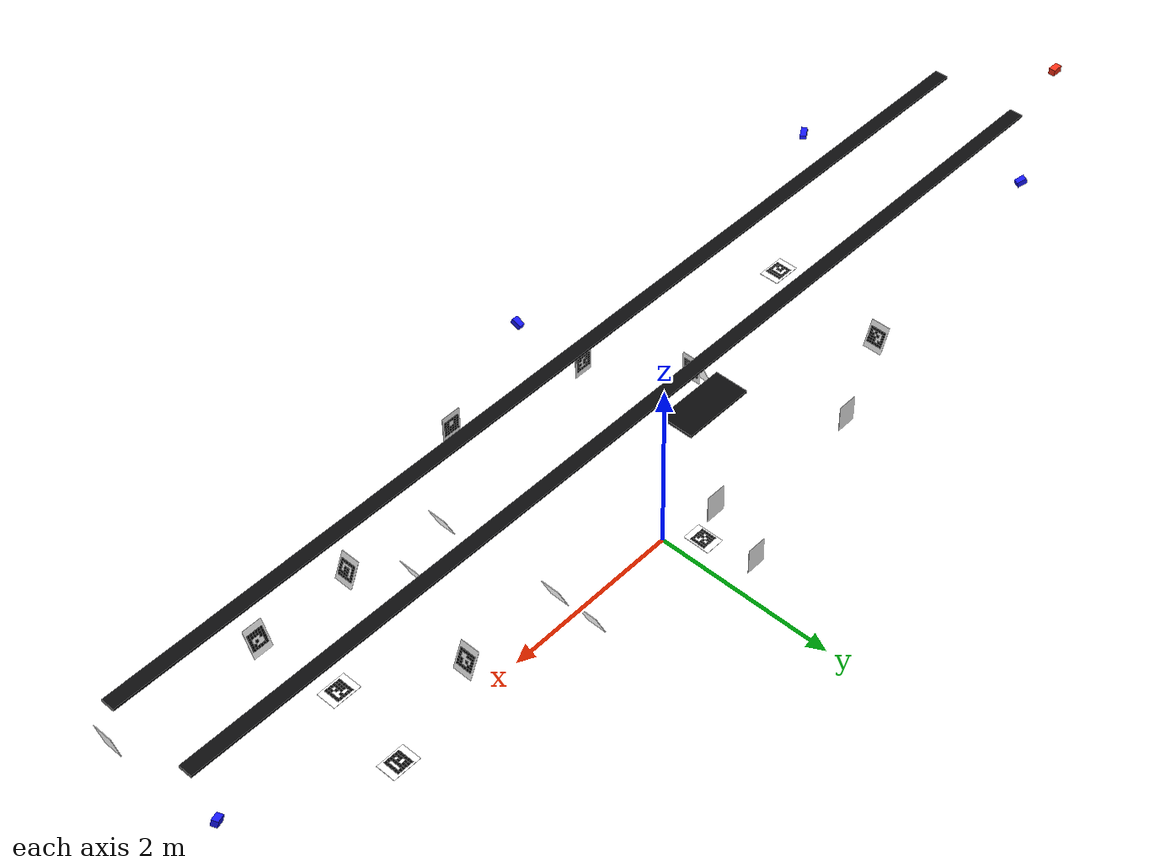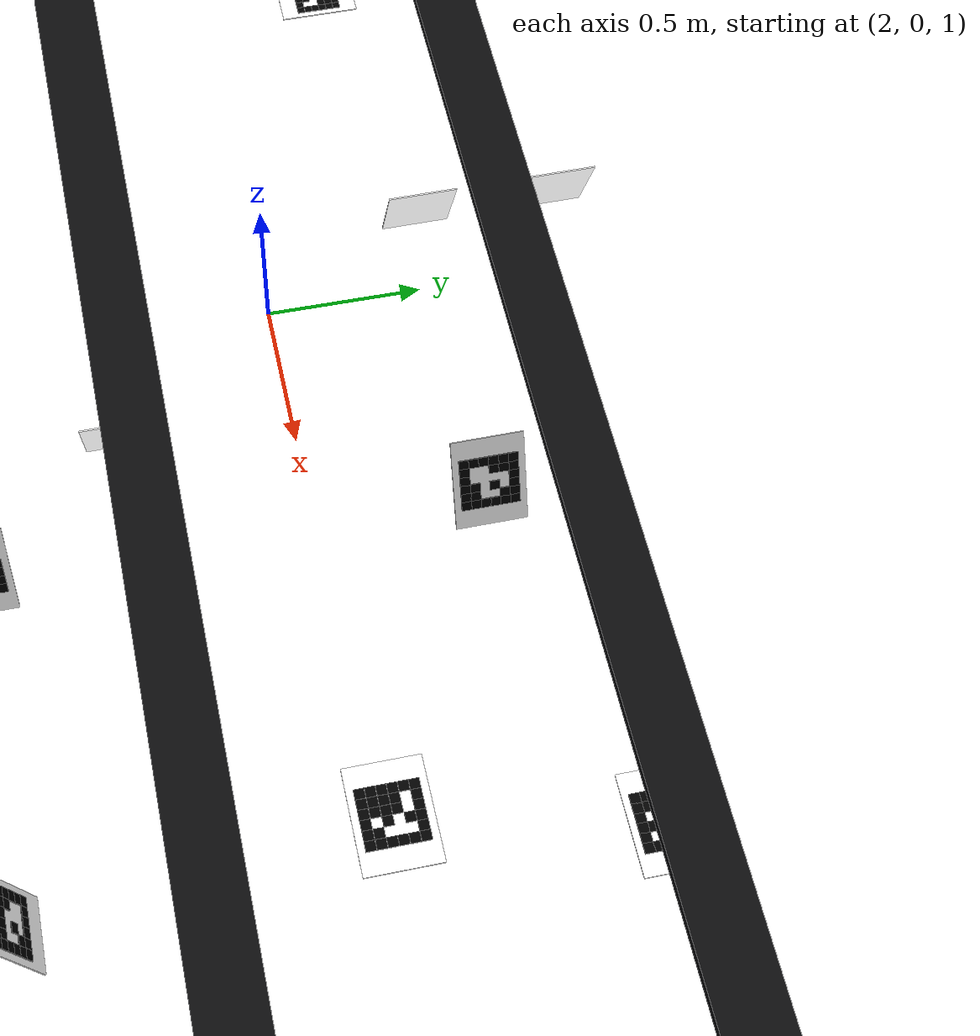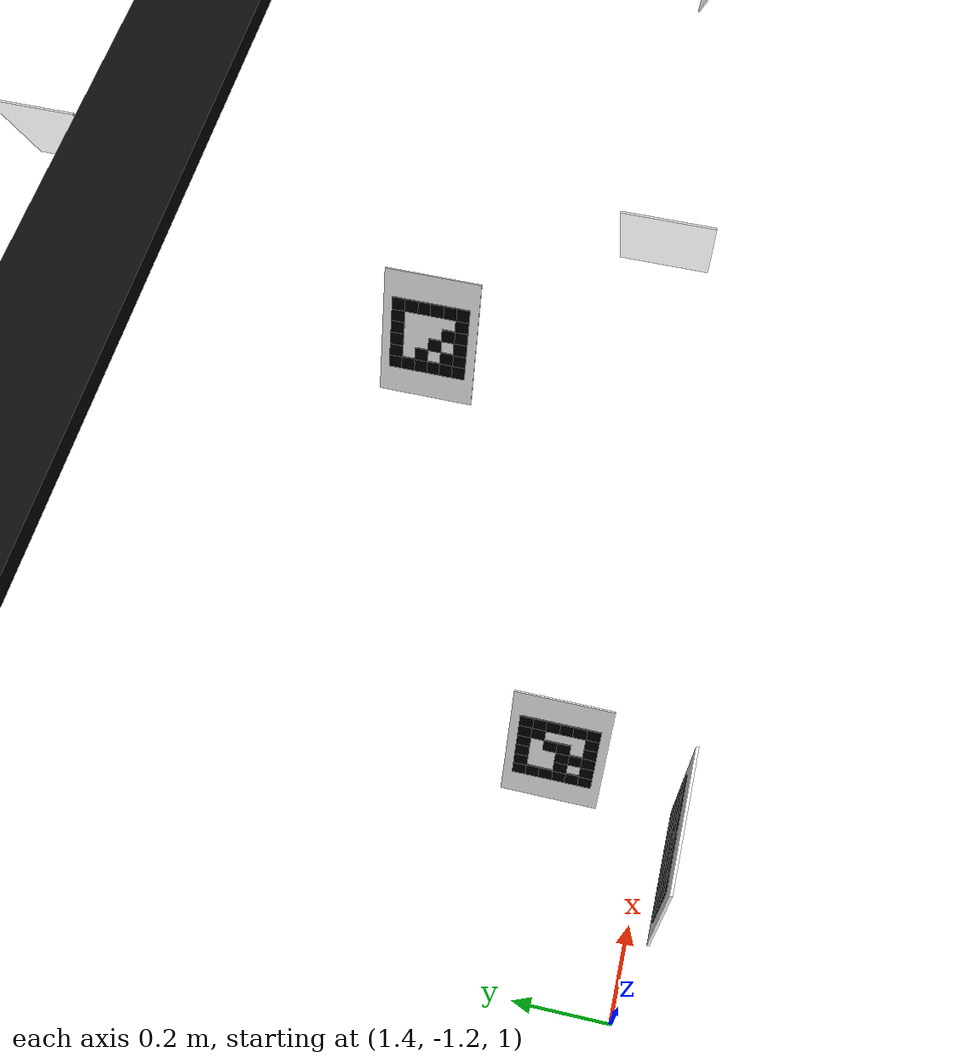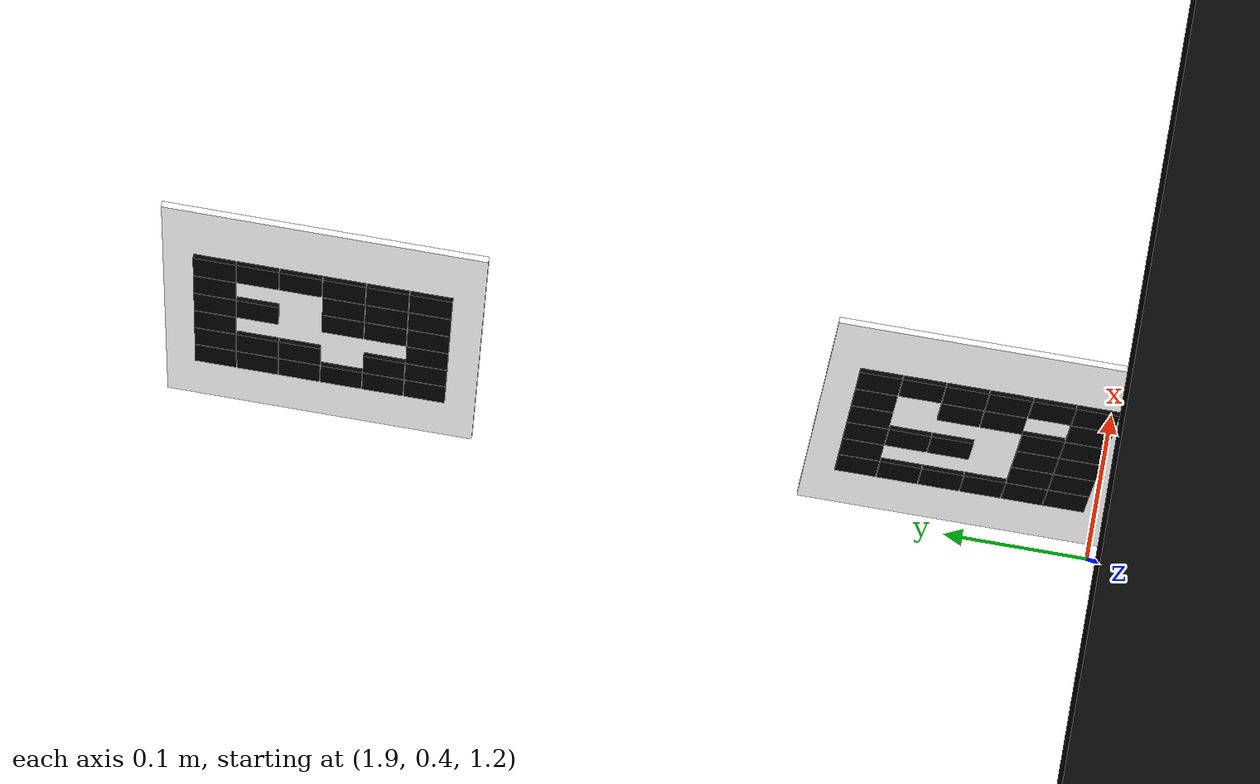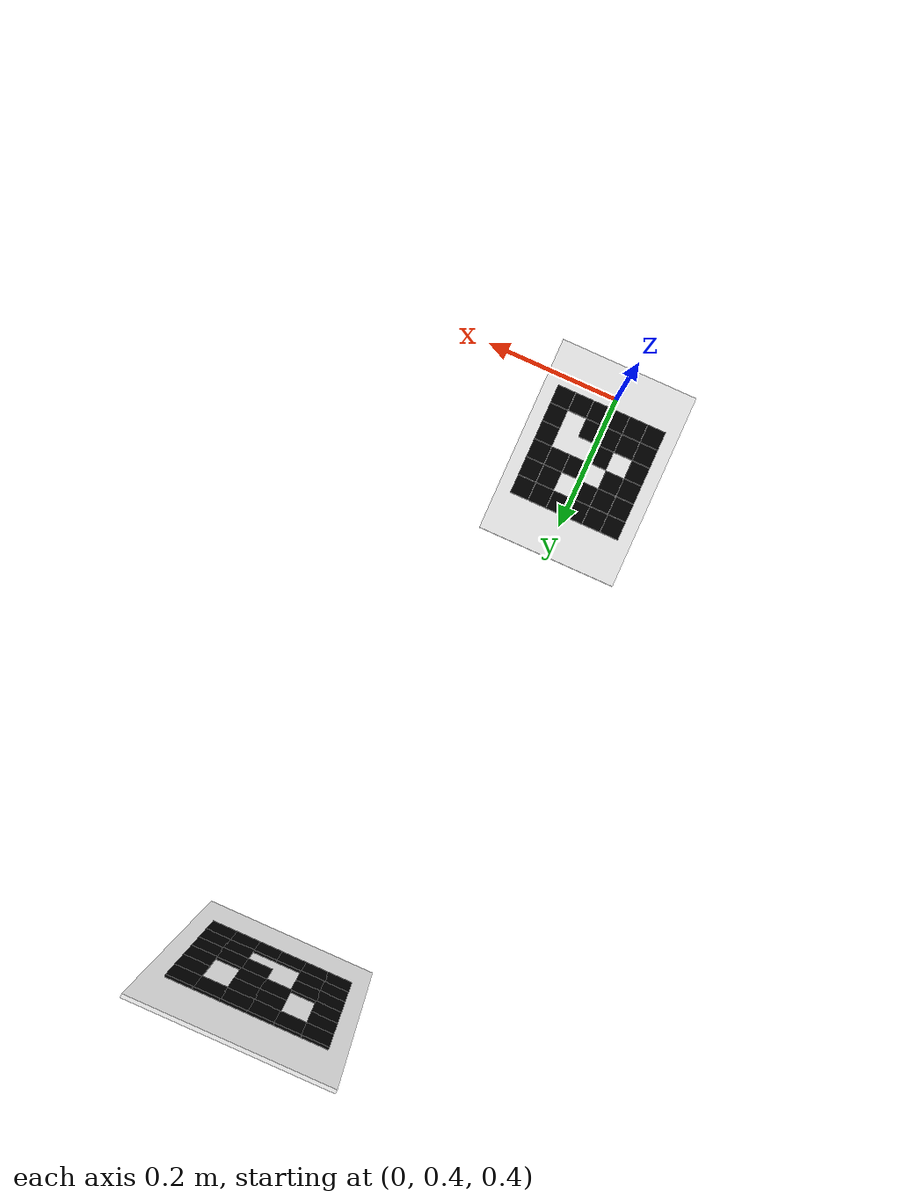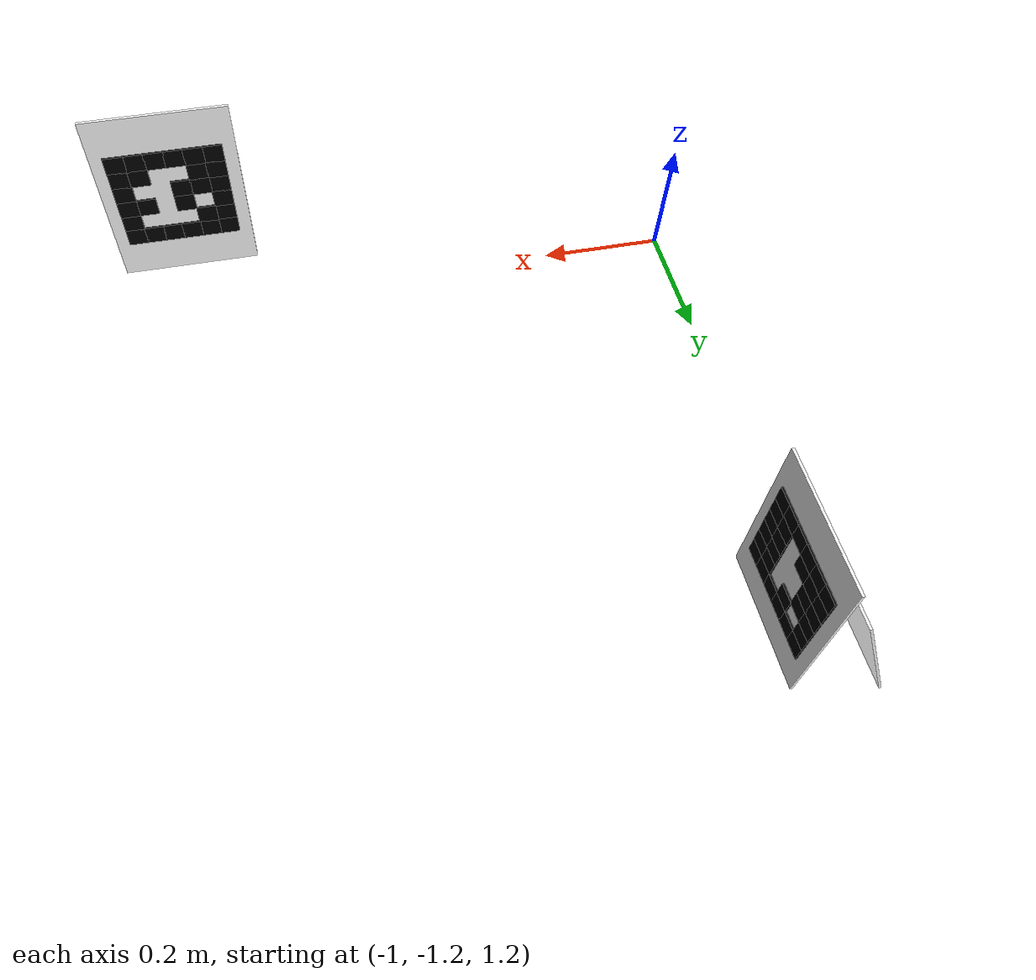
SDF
<sdf version="1.9">
 <world name="bus_real_data_camera_layout">
  <plugin filename="ignition-gazebo-physics-system" name="ignition::gazebo::systems::Physics"/>
  <plugin filename="ignition-gazebo-user-commands-system" name="ignition::gazebo::systems::UserCommands"/>
  <plugin filename="ignition-gazebo-scene-broadcaster-system" name="ignition::gazebo::systems::SceneBroadcaster"/>
  <plugin filename="ignition-gazebo-sensors-system" name="ignition::gazebo::systems::Sensors">
   <render_engine>ogre2</render_engine>
  </plugin>
  <physics name="default_physics" type="ignored">
   <max_step_size>0.01</max_step_size>
   <real_time_factor>1.0</real_time_factor>
  </physics>
  <scene>
   <ambient>0.025000 0.026000 0.032000 1.000000</ambient>
   <background>0.480000 0.520000 0.600000 1.000000</background>
   <shadows>true</shadows>
  </scene>
  <model name="cam_edge_0">
   <static>true</static>
   <pose>0.58780793 -1.23455526 2.48732830 -0.02832886 0.39717862 1.54540010</pose>
   <link name="cam_edge_0_link">
    <visual name="cam_edge_0_visual">
     <geometry><box><size>0.10 0.06 0.06</size></box></geometry>
     <material><ambient>0.1 0.1 1.0 1</ambient><diffuse>0.1 0.1 1.0 1</diffuse></material>
    </visual>
    <sensor name="cam_edge_0_sensor" type="camera">
     <always_on>true</always_on>
     <update_rate>15</update_rate>
     <topic>/bus_real_data/cam_edge_0/image</topic>
     <camera>
      <horizontal_fov>1.2064567910</horizontal_fov>
      <image><width>1280</width><height>720</height><format>R8G8B8</format></image>
      <clip><near>0.05</near><far>100.0</far></clip>
     </camera>
    </sensor>
   </link>
  </model>
  <model name="cam_edge_1">
   <static>true</static>
   <pose>-3.97416732 0.97508650 2.53154268 0.01397153 0.28558128 -0.42471064</pose>
   <link name="cam_edge_1_link">
    <visual name="cam_edge_1_visual">
     <geometry><box><size>0.10 0.06 0.06</size></box></geometry>
     <material><ambient>0.1 0.1 1.0 1</ambient><diffuse>0.1 0.1 1.0 1</diffuse></material>
    </visual>
    <sensor name="cam_edge_1_sensor" type="camera">
     <always_on>true</always_on>
     <update_rate>15</update_rate>
     <topic>/bus_real_data/cam_edge_1/image</topic>
     <camera>
      <horizontal_fov>1.2058954091</horizontal_fov>
      <image><width>1280</width><height>720</height><format>R8G8B8</format></image>
      <clip><near>0.05</near><far>100.0</far></clip>
     </camera>
    </sensor>
   </link>
  </model>
  <model name="cam_edge_3">
   <static>true</static>
   <pose>-3.22735583 -1.06321426 2.45421090 0.03640120 0.33821970 0.53742790</pose>
   <link name="cam_edge_3_link">
    <visual name="cam_edge_3_visual">
     <geometry><box><size>0.10 0.06 0.06</size></box></geometry>
     <material><ambient>0.1 0.1 1.0 1</ambient><diffuse>0.1 0.1 1.0 1</diffuse></material>
    </visual>
    <sensor name="cam_edge_3_sensor" type="camera">
     <always_on>true</always_on>
     <update_rate>15</update_rate>
     <topic>/bus_real_data/cam_edge_3/image</topic>
     <camera>
      <horizontal_fov>1.2156537552</horizontal_fov>
      <image><width>1280</width><height>720</height><format>R8G8B8</format></image>
      <clip><near>0.05</near><far>100.0</far></clip>
     </camera>
    </sensor>
   </link>
  </model>
  <model name="cam_edge_5">
   <static>true</static>
   <pose>5.85885887 0.84841954 2.53876157 0.07529451 0.33545337 -2.70003495</pose>
   <link name="cam_edge_5_link">
    <visual name="cam_edge_5_visual">
     <geometry><box><size>0.10 0.06 0.06</size></box></geometry>
     <material><ambient>0.1 0.1 1.0 1</ambient><diffuse>0.1 0.1 1.0 1</diffuse></material>
    </visual>
    <sensor name="cam_edge_5_sensor" type="camera">
     <always_on>true</always_on>
     <update_rate>15</update_rate>
     <topic>/bus_real_data/cam_edge_5/image</topic>
     <camera>
      <horizontal_fov>1.2083025268</horizontal_fov>
      <image><width>1280</width><height>720</height><format>R8G8B8</format></image>
      <clip><near>0.05</near><far>100.0</far></clip>
     </camera>
    </sensor>
   </link>
  </model>
  <include>
   <uri>model://a4_aruco_marker_000</uri>
   <name>marker_000</name>
   <pose>-2.550000 0.480000 1.180000 -0.40000000 0.00000000 1.57079633</pose>
  </include>
  <include>
   <uri>model://a4_aruco_marker_001</uri>
   <name>marker_001</name>
   <pose>-2.250000 -0.525000 1.630000 -1.57079633 0.00000000 -1.57079633</pose>
  </include>
  <include>
   <uri>model://a4_aruco_marker_002</uri>
   <name>marker_002</name>
   <pose>-1.100000 -0.525000 1.100000 -0.40000000 0.00000000 -1.57079633</pose>
  </include>
  <include>
   <uri>model://a4_aruco_marker_003</uri>
   <name>marker_003</name>
   <pose>0.100000 1.210000 0.800000 0.00000000 0.00000000 0.00000000</pose>
  </include>
  <include>
   <uri>model://a4_aruco_marker_004</uri>
   <name>marker_004</name>
   <pose>0.700000 1.210000 2.000000 0.00000000 0.00000000 0.00000000</pose>
  </include>
  <include>
   <uri>model://a4_aruco_marker_005</uri>
   <name>marker_005</name>
   <pose>1.900000 -0.980000 1.100000 -0.40000000 -0.00000000 -1.57079633</pose>
  </include>
  <include>
   <uri>model://a4_aruco_marker_006</uri>
   <name>marker_006</name>
   <pose>1.970000 0.500000 1.370000 -0.40000000 -0.00000000 -1.57079633</pose>
  </include>
  <include>
   <uri>model://a4_aruco_marker_007</uri>
   <name>marker_007</name>
   <pose>1.970000 0.935000 1.370000 -0.40000000 -0.00000000 -1.57079633</pose>
  </include>
  <include>
   <uri>model://a4_aruco_marker_008</uri>
   <name>marker_008</name>
   <pose>2.650000 -0.525000 1.410000 -0.40000000 -0.00000000 -1.57079633</pose>
  </include>
  <include>
   <uri>model://a4_aruco_marker_009</uri>
   <name>marker_009</name>
   <pose>3.020000 0.480000 1.420000 -0.40000000 0.00000000 1.57079633</pose>
  </include>
  <include>
   <uri>model://a4_aruco_marker_010</uri>
   <name>marker_010</name>
   <pose>3.020000 -0.980000 1.420000 -0.40000000 0.00000000 1.57079633</pose>
  </include>
  <include>
   <uri>model://a4_aruco_marker_011</uri>
   <name>marker_011</name>
   <pose>4.000000 0.000000 1.530000 -1.57079633 0.00000000 1.57079633</pose>
  </include>
  <include>
   <uri>model://a4_aruco_marker_012</uri>
   <name>marker_012</name>
   <pose>4.040000 -0.980000 1.420000 -0.40000000 0.00000000 3.14159265</pose>
  </include>
  <include>
   <uri>model://a4_aruco_marker_013</uri>
   <name>marker_013</name>
   <pose>4.050000 0.730000 1.270000 -1.57079633 0.00000000 1.57079633</pose>
  </include>
  <include>
   <uri>model://a4_aruco_marker_014</uri>
   <name>aruco_ref_floor_14</name>
   <pose>0.000000 0.500000 0.400000 -1.57079633 0.00000000 0.00000000</pose>
  </include>
  <include>
   <uri>model://a4_aruco_marker_016</uri>
   <name>marker_016</name>
   <pose>-0.950000 -0.500000 1.280000 0.00000000 0.00000000 1.57079633</pose>
  </include>
  <include>
   <uri>model://a4_aruco_marker_017</uri>
   <name>marker_017</name>
   <pose>1.500000 -1.200000 1.900000 0.00000000 0.00000000 3.14159265</pose>
  </include>
  <include>
   <uri>model://a4_aruco_marker_018</uri>
   <name>marker_018</name>
   <pose>-0.200000 -1.200000 1.450000 0.00000000 0.00000000 3.14159265</pose>
  </include>
  <include>
   <uri>model://a4_aruco_marker_019</uri>
   <name>marker_019</name>
   <pose>-1.290000 1.090000 1.500000 0.00000000 0.00000000 0.00000000</pose>
  </include>
  <include>
   <uri>model://a4_aruco_marker_020</uri>
   <name>marker_020</name>
   <pose>5.670000 -0.850000 1.750000 -0.20000000 0.00000000 -1.57079633</pose>
  </include>
  <model name="moving_calib_camera">
   <static>true</static>
   <pose>-6.000000 0.000000 2.200000 0.000000 0.000000 0.000000</pose>
   <link name="moving_calib_camera_link">
    <visual name="moving_calib_camera_visual">
     <geometry><box><size>0.12 0.07 0.07</size></box></geometry>
     <material><ambient>1.0 0.2 0.1 1</ambient><diffuse>1.0 0.2 0.1 1</diffuse></material>
    </visual>
    <sensor name="moving_calib_camera_sensor" type="camera">
     <always_on>true</always_on>
     <update_rate>15</update_rate>
     <topic>/bus_real_data/moving_calib_camera/image</topic>
     <camera>
      <horizontal_fov>2.094395102393</horizontal_fov>
      <image><width>1280</width><height>720</height><format>R8G8B8</format></image>
      <clip><near>0.05</near><far>100.0</far></clip>
     </camera>
    </sensor>
   </link>
  </model>
  <model name="bus_ceiling_led_panels">
   <static>true</static>
   <link name="ceiling_led_panel_link">
    <visual name="ceiling_led_strip_0">
     <pose>0.600000 -0.450000 2.700000 0 0 0</pose>
     <geometry><box><size>10.400000 0.140000 0.025000</size></box></geometry>
     <material>
      <ambient>0.045000 0.046000 0.050000 1.000000</ambient>
      <diffuse>0.045000 0.046000 0.050000 1.000000</diffuse>
      <specular>0.100000 0.100000 0.090000 1.000000</specular>
      <emissive>0.045000 0.046000 0.050000 1.000000</emissive>
     </material>
    </visual>
    <visual name="ceiling_led_strip_1">
     <pose>0.600000 0.450000 2.700000 0 0 0</pose>
     <geometry><box><size>10.400000 0.140000 0.025000</size></box></geometry>
     <material>
      <ambient>0.045000 0.046000 0.050000 1.000000</ambient>
      <diffuse>0.045000 0.046000 0.050000 1.000000</diffuse>
      <specular>0.100000 0.100000 0.090000 1.000000</specular>
      <emissive>0.045000 0.046000 0.050000 1.000000</emissive>
     </material>
    </visual>
    <visual name="door_ceiling_led_panel">
     <pose>0.400000 0.800000 2.700000 0 0 0</pose>
     <geometry><box><size>0.720000 0.340000 0.025000</size></box></geometry>
     <material>
      <ambient>0.040500 0.041400 0.045000 1.000000</ambient>
      <diffuse>0.040500 0.041400 0.045000 1.000000</diffuse>
      <specular>0.100000 0.100000 0.090000 1.000000</specular>
      <emissive>0.040500 0.041400 0.045000 1.000000</emissive>
     </material>
    </visual>
   </link>
  </model>
  <light name="ceiling_strip_point_00" type="point">
   <pose>-4.200000 -0.450000 2.610000 0 0 0</pose>
   <cast_shadows>false</cast_shadows>
   <visualize>false</visualize>
   <diffuse>0.035000 0.036000 0.040000 1.000000</diffuse>
   <specular>0.003000 0.003000 0.004000 1.000000</specular>
   <attenuation>
    <range>4.600000</range>
    <constant>0.880000</constant>
    <linear>0.095000</linear>
    <quadratic>0.022000</quadratic>
   </attenuation>
  </light>
  <light name="ceiling_strip_point_01" type="point">
   <pose>-2.600000 -0.450000 2.610000 0 0 0</pose>
   <cast_shadows>false</cast_shadows>
   <visualize>false</visualize>
   <diffuse>0.035000 0.036000 0.040000 1.000000</diffuse>
   <specular>0.003000 0.003000 0.004000 1.000000</specular>
   <attenuation>
    <range>4.600000</range>
    <constant>0.880000</constant>
    <linear>0.095000</linear>
    <quadratic>0.022000</quadratic>
   </attenuation>
  </light>
  <light name="ceiling_strip_point_02" type="point">
   <pose>-1.000000 -0.450000 2.610000 0 0 0</pose>
   <cast_shadows>false</cast_shadows>
   <visualize>false</visualize>
   <diffuse>0.035000 0.036000 0.040000 1.000000</diffuse>
   <specular>0.003000 0.003000 0.004000 1.000000</specular>
   <attenuation>
    <range>4.600000</range>
    <constant>0.880000</constant>
    <linear>0.095000</linear>
    <quadratic>0.022000</quadratic>
   </attenuation>
  </light>
  <light name="ceiling_strip_point_03" type="point">
   <pose>0.600000 -0.450000 2.610000 0 0 0</pose>
   <cast_shadows>false</cast_shadows>
   <visualize>false</visualize>
   <diffuse>0.035000 0.036000 0.040000 1.000000</diffuse>
   <specular>0.003000 0.003000 0.004000 1.000000</specular>
   <attenuation>
    <range>4.600000</range>
    <constant>0.880000</constant>
    <linear>0.095000</linear>
    <quadratic>0.022000</quadratic>
   </attenuation>
  </light>
  <light name="ceiling_strip_point_04" type="point">
   <pose>2.200000 -0.450000 2.610000 0 0 0</pose>
   <cast_shadows>false</cast_shadows>
   <visualize>false</visualize>
   <diffuse>0.035000 0.036000 0.040000 1.000000</diffuse>
   <specular>0.003000 0.003000 0.004000 1.000000</specular>
   <attenuation>
    <range>4.600000</range>
    <constant>0.880000</constant>
    <linear>0.095000</linear>
    <quadratic>0.022000</quadratic>
   </attenuation>
  </light>
  <light name="ceiling_strip_point_05" type="point">
   <pose>3.800000 -0.450000 2.610000 0 0 0</pose>
   <cast_shadows>false</cast_shadows>
   <visualize>false</visualize>
   <diffuse>0.035000 0.036000 0.040000 1.000000</diffuse>
   <specular>0.003000 0.003000 0.004000 1.000000</specular>
   <attenuation>
    <range>4.600000</range>
    <constant>0.880000</constant>
    <linear>0.095000</linear>
    <quadratic>0.022000</quadratic>
   </attenuation>
  </light>
  <light name="ceiling_strip_point_06" type="point">
   <pose>5.400000 -0.450000 2.610000 0 0 0</pose>
   <cast_shadows>false</cast_shadows>
   <visualize>false</visualize>
   <diffuse>0.035000 0.036000 0.040000 1.000000</diffuse>
   <specular>0.003000 0.003000 0.004000 1.000000</specular>
   <attenuation>
    <range>4.600000</range>
    <constant>0.880000</constant>
    <linear>0.095000</linear>
    <quadratic>0.022000</quadratic>
   </attenuation>
  </light>
  <light name="ceiling_strip_point_07" type="point">
   <pose>-4.200000 0.450000 2.610000 0 0 0</pose>
   <cast_shadows>false</cast_shadows>
   <visualize>false</visualize>
   <diffuse>0.035000 0.036000 0.040000 1.000000</diffuse>
   <specular>0.003000 0.003000 0.004000 1.000000</specular>
   <attenuation>
    <range>4.600000</range>
    <constant>0.880000</constant>
    <linear>0.095000</linear>
    <quadratic>0.022000</quadratic>
   </attenuation>
  </light>
  <light name="ceiling_strip_point_08" type="point">
   <pose>-2.600000 0.450000 2.610000 0 0 0</pose>
   <cast_shadows>false</cast_shadows>
   <visualize>false</visualize>
   <diffuse>0.035000 0.036000 0.040000 1.000000</diffuse>
   <specular>0.003000 0.003000 0.004000 1.000000</specular>
   <attenuation>
    <range>4.600000</range>
    <constant>0.880000</constant>
    <linear>0.095000</linear>
    <quadratic>0.022000</quadratic>
   </attenuation>
  </light>
  <light name="ceiling_strip_point_09" type="point">
   <pose>-1.000000 0.450000 2.610000 0 0 0</pose>
   <cast_shadows>false</cast_shadows>
   <visualize>false</visualize>
   <diffuse>0.035000 0.036000 0.040000 1.000000</diffuse>
   <specular>0.003000 0.003000 0.004000 1.000000</specular>
   <attenuation>
    <range>4.600000</range>
    <constant>0.880000</constant>
    <linear>0.095000</linear>
    <quadratic>0.022000</quadratic>
   </attenuation>
  </light>
  <light name="ceiling_strip_point_10" type="point">
   <pose>0.600000 0.450000 2.610000 0 0 0</pose>
   <cast_shadows>false</cast_shadows>
   <visualize>false</visualize>
   <diffuse>0.035000 0.036000 0.040000 1.000000</diffuse>
   <specular>0.003000 0.003000 0.004000 1.000000</specular>
   <attenuation>
    <range>4.600000</range>
    <constant>0.880000</constant>
    <linear>0.095000</linear>
    <quadratic>0.022000</quadratic>
   </attenuation>
  </light>
  <light name="ceiling_strip_point_11" type="point">
   <pose>2.200000 0.450000 2.610000 0 0 0</pose>
   <cast_shadows>false</cast_shadows>
   <visualize>false</visualize>
   <diffuse>0.035000 0.036000 0.040000 1.000000</diffuse>
   <specular>0.003000 0.003000 0.004000 1.000000</specular>
   <attenuation>
    <range>4.600000</range>
    <constant>0.880000</constant>
    <linear>0.095000</linear>
    <quadratic>0.022000</quadratic>
   </attenuation>
  </light>
  <light name="ceiling_strip_point_12" type="point">
   <pose>3.800000 0.450000 2.610000 0 0 0</pose>
   <cast_shadows>false</cast_shadows>
   <visualize>false</visualize>
   <diffuse>0.035000 0.036000 0.040000 1.000000</diffuse>
   <specular>0.003000 0.003000 0.004000 1.000000</specular>
   <attenuation>
    <range>4.600000</range>
    <constant>0.880000</constant>
    <linear>0.095000</linear>
    <quadratic>0.022000</quadratic>
   </attenuation>
  </light>
  <light name="ceiling_strip_point_13" type="point">
   <pose>5.400000 0.450000 2.610000 0 0 0</pose>
   <cast_shadows>false</cast_shadows>
   <visualize>false</visualize>
   <diffuse>0.035000 0.036000 0.040000 1.000000</diffuse>
   <specular>0.003000 0.003000 0.004000 1.000000</specular>
   <attenuation>
    <range>4.600000</range>
    <constant>0.880000</constant>
    <linear>0.095000</linear>
    <quadratic>0.022000</quadratic>
   </attenuation>
  </light>
  <light name="door_ceiling_point" type="point">
   <pose>0.400000 0.800000 2.580000 0 0 0</pose>
   <cast_shadows>false</cast_shadows>
   <visualize>false</visualize>
   <diffuse>0.025200 0.025920 0.028800 1.000000</diffuse>
   <specular>0.001650 0.001650 0.002200 1.000000</specular>
   <attenuation>
    <range>3.200000</range>
    <constant>0.780000</constant>
    <linear>0.105000</linear>
    <quadratic>0.027000</quadratic>
   </attenuation>
  </light>
 </world>
</sdf>

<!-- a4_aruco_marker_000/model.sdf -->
<sdf version="1.9">
  <model name="a4_aruco_marker_000">
    <static>true</static>
    <link name="board_link">

      <visual name="a4_white_sheet">
          <cast_shadows>false</cast_shadows>
        <pose>0 0 0 0 0 0</pose>
        <geometry>
          <box>
            <size>0.210000 0.004 0.297000</size>
          </box>
        </geometry>
        <material>
          <ambient>1 1 1 1</ambient>
          <diffuse>1 1 1 1</diffuse>
            <specular>0 0 0 1</specular>
        </material>
      </visual>

        <visual name="black_cell_0_0">
          <cast_shadows>false</cast_shadows>
          <pose>-0.070833 -0.004000 0.070833 0 0 0</pose>
          <geometry>
            <box>
              <size>0.029467 0.003 0.029467</size>
            </box>
          </geometry>
          <material>
            <ambient>0 0 0 1</ambient>
            <diffuse>0 0 0 1</diffuse>
            <specular>0 0 0 1</specular>
          </material>
        </visual>

        <visual name="black_cell_0_1">
          <cast_shadows>false</cast_shadows>
          <pose>-0.042500 -0.004000 0.070833 0 0 0</pose>
          <geometry>
            <box>
              <size>0.029467 0.003 0.029467</size>
            </box>
          </geometry>
          <material>
            <ambient>0 0 0 1</ambient>
            <diffuse>0 0 0 1</diffuse>
            <specular>0 0 0 1</specular>
          </material>
        </visual>

        <visual name="black_cell_0_2">
          <cast_shadows>false</cast_shadows>
          <pose>-0.014167 -0.004000 0.070833 0 0 0</pose>
          <geometry>
            <box>
              <size>0.029467 0.003 0.029467</size>
            </box>
          </geometry>
          <material>
            <ambient>0 0 0 1</ambient>
            <diffuse>0 0 0 1</diffuse>
            <specular>0 0 0 1</specular>
          </material>
        </visual>

        <visual name="black_cell_0_3">
          <cast_shadows>false</cast_shadows>
          <pose>0.014167 -0.004000 0.070833 0 0 0</pose>
          <geometry>
            <box>
              <size>0.029467 0.003 0.029467</size>
            </box>
          </geometry>
          <material>
            <ambient>0 0 0 1</ambient>
            <diffuse>0 0 0 1</diffuse>
            <specular>0 0 0 1</specular>
          </material>
        </visual>

        <visual name="black_cell_0_4">
          <cast_shadows>false</cast_shadows>
          <pose>0.042500 -0.004000 0.070833 0 0 0</pose>
          <geometry>
            <box>
              <size>0.029467 0.003 0.029467</size>
            </box>
          </geometry>
          <material>
            <ambient>0 0 0 1</ambient>
            <diffuse>0 0 0 1</diffuse>
            <specular>0 0 0 1</specular>
          </material>
        </visual>

        <visual name="black_cell_0_5">
          <cast_shadows>false</cast_shadows>
          <pose>0.070833 -0.004000 0.070833 0 0 0</pose>
          <geometry>
            <box>
              <size>0.029467 0.003 0.029467</size>
            </box>
          </geometry>
          <material>
            <ambient>0 0 0 1</ambient>
            <diffuse>0 0 0 1</diffuse>
            <specular>0 0 0 1</specular>
          </material>
        </visual>

        <visual name="black_cell_1_0">
          <cast_shadows>false</cast_shadows>
          <pose>-0.070833 -0.004000 0.042500 0 0 0</pose>
          <geometry>
            <box>
              <size>0.029467 0.003 0.029467</size>
            </box>
          </geometry>
          <material>
            <ambient>0 0 0 1</ambient>
            <diffuse>0 0 0 1</diffuse>
            <specular>0 0 0 1</specular>
          </material>
        </visual>

        <visual name="black_cell_1_2">
          <cast_shadows>false</cast_shadows>
          <pose>-0.014167 -0.004000 0.042500 0 0 0</pose>
          <geometry>
            <box>
              <size>0.029467 0.003 0.029467</size>
            </box>
          </geometry>
          <material>
            <ambient>0 0 0 1</ambient>
            <diffuse>0 0 0 1</diffuse>
            <specular>0 0 0 1</specular>
          </material>
        </visual>

        <visual name="black_cell_1_5">
          <cast_shadows>false</cast_shadows>
          <pose>0.070833 -0.004000 0.042500 0 0 0</pose>
          <geometry>
            <box>
              <size>0.029467 0.003 0.029467</size>
            </box>
          </geometry>
          <material>
            <ambient>0 0 0 1</ambient>
            <diffuse>0 0 0 1</diffuse>
            <specular>0 0 0 1</specular>
          </material>
        </visual>

        <visual name="black_cell_2_0">
          <cast_shadows>false</cast_shadows>
          <pose>-0.070833 -0.004000 0.014167 0 0 0</pose>
          <geometry>
            <box>
              <size>0.029467 0.003 0.029467</size>
            </box>
          </geometry>
          <material>
            <ambient>0 0 0 1</ambient>
            <diffuse>0 0 0 1</diffuse>
            <specular>0 0 0 1</specular>
          </material>
        </visual>

        <visual name="black_cell_2_1">
          <cast_shadows>false</cast_shadows>
          <pose>-0.042500 -0.004000 0.014167 0 0 0</pose>
          <geometry>
            <box>
              <size>0.029467 0.003 0.029467</size>
            </box>
          </geometry>
          <material>
            <ambient>0 0 0 1</ambient>
            <diffuse>0 0 0 1</diffuse>
            <specular>0 0 0 1</specular>
          </material>
        </visual>

        <visual name="black_cell_2_3">
          <cast_shadows>false</cast_shadows>
          <pose>0.014167 -0.004000 0.014167 0 0 0</pose>
          <geometry>
            <box>
              <size>0.029467 0.003 0.029467</size>
            </box>
          </geometry>
          <material>
            <ambient>0 0 0 1</ambient>
            <diffuse>0 0 0 1</diffuse>
            <specular>0 0 0 1</specular>
          </material>
        </visual>

        <visual name="black_cell_2_5">
          <cast_shadows>false</cast_shadows>
          <pose>0.070833 -0.004000 0.014167 0 0 0</pose>
          <geometry>
            <box>
              <size>0.029467 0.003 0.029467</size>
            </box>
          </geometry>
          <material>
            <ambient>0 0 0 1</ambient>
            <diffuse>0 0 0 1</diffuse>
            <specular>0 0 0 1</specular>
          </material>
        </visual>

        <visual name="black_cell_3_0">
          <cast_shadows>false</cast_shadows>
          <pose>-0.070833 -0.004000 -0.014167 0 0 0</pose>
          <geometry>
            <box>
              <size>0.029467 0.003 0.029467</size>
            </box>
          </geometry>
          <material>
            <ambient>0 0 0 1</ambient>
            <diffuse>0 0 0 1</diffuse>
            <specular>0 0 0 1</specular>
          </material>
        </visual>

        <visual name="black_cell_3_1">
          <cast_shadows>false</cast_shadows>
          <pose>-0.042500 -0.004000 -0.014167 0 0 0</pose>
          <geometry>
            <box>
              <size>0.029467 0.003 0.029467</size>
            </box>
          </geometry>
          <material>
            <ambient>0 0 0 1</ambient>
            <diffuse>0 0 0 1</diffuse>
            <specular>0 0 0 1</specular>
          </material>
        </visual>

        <visual name="black_cell_3_2">
          <cast_shadows>false</cast_shadows>
          <pose>-0.014167 -0.004000 -0.014167 0 0 0</pose>
          <geometry>
            <box>
              <size>0.029467 0.003 0.029467</size>
            </box>
          </geometry>
          <material>
            <ambient>0 0 0 1</ambient>
            <diffuse>0 0 0 1</diffuse>
            <specular>0 0 0 1</specular>
          </material>
        </visual>

        <visual name="black_cell_3_5">
          <cast_shadows>false</cast_shadows>
          <pose>0.070833 -0.004000 -0.014167 0 0 0</pose>
          <geometry>
            <box>
              <size>0.029467 0.003 0.029467</size>
            </box>
          </geometry>
          <material>
            <ambient>0 0 0 1</ambient>
            <diffuse>0 0 0 1</diffuse>
            <specular>0 0 0 1</specular>
          </material>
        </visual>

        <visual name="black_cell_4_0">
          <cast_shadows>false</cast_shadows>
          <pose>-0.070833 -0.004000 -0.042500 0 0 0</pose>
          <geometry>
            <box>
              <size>0.029467 0.003 0.029467</size>
            </box>
          </geometry>
          <material>
            <ambient>0 0 0 1</ambient>
            <diffuse>0 0 0 1</diffuse>
            <specular>0 0 0 1</specular>
          </material>
        </visual>

        <visual name="black_cell_4_1">
          <cast_shadows>false</cast_shadows>
          <pose>-0.042500 -0.004000 -0.042500 0 0 0</pose>
          <geometry>
            <box>
              <size>0.029467 0.003 0.029467</size>
            </box>
          </geometry>
          <material>
            <ambient>0 0 0 1</ambient>
            <diffuse>0 0 0 1</diffuse>
            <specular>0 0 0 1</specular>
          </material>
        </visual>

        <visual name="black_cell_4_2">
          <cast_shadows>false</cast_shadows>
          <pose>-0.014167 -0.004000 -0.042500 0 0 0</pose>
          <geometry>
            <box>
              <size>0.029467 0.003 0.029467</size>
            </box>
          </geometry>
          <material>
            <ambient>0 0 0 1</ambient>
            <diffuse>0 0 0 1</diffuse>
            <specular>0 0 0 1</specular>
          </material>
        </visual>

        <visual name="black_cell_4_4">
          <cast_shadows>false</cast_shadows>
          <pose>0.042500 -0.004000 -0.042500 0 0 0</pose>
          <geometry>
            <box>
              <size>0.029467 0.003 0.029467</size>
            </box>
          </geometry>
          <material>
            <ambient>0 0 0 1</ambient>
            <diffuse>0 0 0 1</diffuse>
            <specular>0 0 0 1</specular>
          </material>
        </visual>

        <visual name="black_cell_4_5">
          <cast_shadows>false</cast_shadows>
          <pose>0.070833 -0.004000 -0.042500 0 0 0</pose>
          <geometry>
            <box>
              <size>0.029467 0.003 0.029467</size>
            </box>
          </geometry>
          <material>
            <ambient>0 0 0 1</ambient>
            <diffuse>0 0 0 1</diffuse>
            <specular>0 0 0 1</specular>
          </material>
        </visual>

        <visual name="black_cell_5_0">
          <cast_shadows>false</cast_shadows>
          <pose>-0.070833 -0.004000 -0.070833 0 0 0</pose>
          <geometry>
            <box>
              <size>0.029467 0.003 0.029467</size>
            </box>
          </geometry>
          <material>
            <ambient>0 0 0 1</ambient>
            <diffuse>0 0 0 1</diffuse>
            <specular>0 0 0 1</specular>
          </material>
        </visual>

        <visual name="black_cell_5_1">
          <cast_shadows>false</cast_shadows>
          <pose>-0.042500 -0.004000 -0.070833 0 0 0</pose>
          <geometry>
            <box>
              <size>0.029467 0.003 0.029467</size>
            </box>
          </geometry>
          <material>
            <ambient>0 0 0 1</ambient>
            <diffuse>0 0 0 1</diffuse>
            <specular>0 0 0 1</specular>
          </material>
        </visual>

        <visual name="black_cell_5_2">
          <cast_shadows>false</cast_shadows>
          <pose>-0.014167 -0.004000 -0.070833 0 0 0</pose>
          <geometry>
            <box>
              <size>0.029467 0.003 0.029467</size>
            </box>
          </geometry>
          <material>
            <ambient>0 0 0 1</ambient>
            <diffuse>0 0 0 1</diffuse>
            <specular>0 0 0 1</specular>
          </material>
        </visual>

        <visual name="black_cell_5_3">
          <cast_shadows>false</cast_shadows>
          <pose>0.014167 -0.004000 -0.070833 0 0 0</pose>
          <geometry>
            <box>
              <size>0.029467 0.003 0.029467</size>
            </box>
          </geometry>
          <material>
            <ambient>0 0 0 1</ambient>
            <diffuse>0 0 0 1</diffuse>
            <specular>0 0 0 1</specular>
          </material>
        </visual>

        <visual name="black_cell_5_4">
          <cast_shadows>false</cast_shadows>
          <pose>0.042500 -0.004000 -0.070833 0 0 0</pose>
          <geometry>
            <box>
              <size>0.029467 0.003 0.029467</size>
            </box>
          </geometry>
          <material>
            <ambient>0 0 0 1</ambient>
            <diffuse>0 0 0 1</diffuse>
            <specular>0 0 0 1</specular>
          </material>
        </visual>

        <visual name="black_cell_5_5">
          <cast_shadows>false</cast_shadows>
          <pose>0.070833 -0.004000 -0.070833 0 0 0</pose>
          <geometry>
            <box>
              <size>0.029467 0.003 0.029467</size>
            </box>
          </geometry>
          <material>
            <ambient>0 0 0 1</ambient>
            <diffuse>0 0 0 1</diffuse>
            <specular>0 0 0 1</specular>
          </material>
        </visual>

    </link>
  </model>
</sdf>

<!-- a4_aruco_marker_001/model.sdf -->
<sdf version="1.9">
  <model name="a4_aruco_marker_001">
    <static>true</static>
    <link name="board_link">

      <visual name="a4_white_sheet">
        <pose>0 0 0 0 0 0</pose>
        <geometry>
          <box>
            <size>0.210000 0.004 0.297000</size>
          </box>
        </geometry>
        <material>
          <ambient>1 1 1 1</ambient>
          <diffuse>1 1 1 1</diffuse>
        </material>
      </visual>

        <visual name="black_cell_0_0">
          <pose>-0.070833 -0.004000 0.070833 0 0 0</pose>
          <geometry>
            <box>
              <size>0.027767 0.003 0.027767</size>
            </box>
          </geometry>
          <material>
            <ambient>0 0 0 1</ambient>
            <diffuse>0 0 0 1</diffuse>
          </material>
        </visual>

        <visual name="black_cell_0_1">
          <pose>-0.042500 -0.004000 0.070833 0 0 0</pose>
          <geometry>
            <box>
              <size>0.027767 0.003 0.027767</size>
            </box>
          </geometry>
          <material>
            <ambient>0 0 0 1</ambient>
            <diffuse>0 0 0 1</diffuse>
          </material>
        </visual>

        <visual name="black_cell_0_2">
          <pose>-0.014167 -0.004000 0.070833 0 0 0</pose>
          <geometry>
            <box>
              <size>0.027767 0.003 0.027767</size>
            </box>
          </geometry>
          <material>
            <ambient>0 0 0 1</ambient>
            <diffuse>0 0 0 1</diffuse>
          </material>
        </visual>

        <visual name="black_cell_0_3">
          <pose>0.014167 -0.004000 0.070833 0 0 0</pose>
          <geometry>
            <box>
              <size>0.027767 0.003 0.027767</size>
            </box>
          </geometry>
          <material>
            <ambient>0 0 0 1</ambient>
            <diffuse>0 0 0 1</diffuse>
          </material>
        </visual>

        <visual name="black_cell_0_4">
          <pose>0.042500 -0.004000 0.070833 0 0 0</pose>
          <geometry>
            <box>
              <size>0.027767 0.003 0.027767</size>
            </box>
          </geometry>
          <material>
            <ambient>0 0 0 1</ambient>
            <diffuse>0 0 0 1</diffuse>
          </material>
        </visual>

        <visual name="black_cell_0_5">
          <pose>0.070833 -0.004000 0.070833 0 0 0</pose>
          <geometry>
            <box>
              <size>0.027767 0.003 0.027767</size>
            </box>
          </geometry>
          <material>
            <ambient>0 0 0 1</ambient>
            <diffuse>0 0 0 1</diffuse>
          </material>
        </visual>

        <visual name="black_cell_1_0">
          <pose>-0.070833 -0.004000 0.042500 0 0 0</pose>
          <geometry>
            <box>
              <size>0.027767 0.003 0.027767</size>
            </box>
          </geometry>
          <material>
            <ambient>0 0 0 1</ambient>
            <diffuse>0 0 0 1</diffuse>
          </material>
        </visual>

        <visual name="black_cell_1_1">
          <pose>-0.042500 -0.004000 0.042500 0 0 0</pose>
          <geometry>
            <box>
              <size>0.027767 0.003 0.027767</size>
            </box>
          </geometry>
          <material>
            <ambient>0 0 0 1</ambient>
            <diffuse>0 0 0 1</diffuse>
          </material>
        </visual>

        <visual name="black_cell_1_2">
          <pose>-0.014167 -0.004000 0.042500 0 0 0</pose>
          <geometry>
            <box>
              <size>0.027767 0.003 0.027767</size>
            </box>
          </geometry>
          <material>
            <ambient>0 0 0 1</ambient>
            <diffuse>0 0 0 1</diffuse>
          </material>
        </visual>

        <visual name="black_cell_1_3">
          <pose>0.014167 -0.004000 0.042500 0 0 0</pose>
          <geometry>
            <box>
              <size>0.027767 0.003 0.027767</size>
            </box>
          </geometry>
          <material>
            <ambient>0 0 0 1</ambient>
            <diffuse>0 0 0 1</diffuse>
          </material>
        </visual>

        <visual name="black_cell_1_4">
          <pose>0.042500 -0.004000 0.042500 0 0 0</pose>
          <geometry>
            <box>
              <size>0.027767 0.003 0.027767</size>
            </box>
          </geometry>
          <material>
            <ambient>0 0 0 1</ambient>
            <diffuse>0 0 0 1</diffuse>
          </material>
        </visual>

        <visual name="black_cell_1_5">
          <pose>0.070833 -0.004000 0.042500 0 0 0</pose>
          <geometry>
            <box>
              <size>0.027767 0.003 0.027767</size>
            </box>
          </geometry>
          <material>
            <ambient>0 0 0 1</ambient>
            <diffuse>0 0 0 1</diffuse>
          </material>
        </visual>

        <visual name="black_cell_2_0">
          <pose>-0.070833 -0.004000 0.014167 0 0 0</pose>
          <geometry>
            <box>
              <size>0.027767 0.003 0.027767</size>
            </box>
          </geometry>
          <material>
            <ambient>0 0 0 1</ambient>
            <diffuse>0 0 0 1</diffuse>
          </material>
        </visual>

        <visual name="black_cell_2_5">
          <pose>0.070833 -0.004000 0.014167 0 0 0</pose>
          <geometry>
            <box>
              <size>0.027767 0.003 0.027767</size>
            </box>
          </geometry>
          <material>
            <ambient>0 0 0 1</ambient>
            <diffuse>0 0 0 1</diffuse>
          </material>
        </visual>

        <visual name="black_cell_3_0">
          <pose>-0.070833 -0.004000 -0.014167 0 0 0</pose>
          <geometry>
            <box>
              <size>0.027767 0.003 0.027767</size>
            </box>
          </geometry>
          <material>
            <ambient>0 0 0 1</ambient>
            <diffuse>0 0 0 1</diffuse>
          </material>
        </visual>

        <visual name="black_cell_3_2">
          <pose>-0.014167 -0.004000 -0.014167 0 0 0</pose>
          <geometry>
            <box>
              <size>0.027767 0.003 0.027767</size>
            </box>
          </geometry>
          <material>
            <ambient>0 0 0 1</ambient>
            <diffuse>0 0 0 1</diffuse>
          </material>
        </visual>

        <visual name="black_cell_3_3">
          <pose>0.014167 -0.004000 -0.014167 0 0 0</pose>
          <geometry>
            <box>
              <size>0.027767 0.003 0.027767</size>
            </box>
          </geometry>
          <material>
            <ambient>0 0 0 1</ambient>
            <diffuse>0 0 0 1</diffuse>
          </material>
        </visual>

        <visual name="black_cell_3_5">
          <pose>0.070833 -0.004000 -0.014167 0 0 0</pose>
          <geometry>
            <box>
              <size>0.027767 0.003 0.027767</size>
            </box>
          </geometry>
          <material>
            <ambient>0 0 0 1</ambient>
            <diffuse>0 0 0 1</diffuse>
          </material>
        </visual>

        <visual name="black_cell_4_0">
          <pose>-0.070833 -0.004000 -0.042500 0 0 0</pose>
          <geometry>
            <box>
              <size>0.027767 0.003 0.027767</size>
            </box>
          </geometry>
          <material>
            <ambient>0 0 0 1</ambient>
            <diffuse>0 0 0 1</diffuse>
          </material>
        </visual>

        <visual name="black_cell_4_2">
          <pose>-0.014167 -0.004000 -0.042500 0 0 0</pose>
          <geometry>
            <box>
              <size>0.027767 0.003 0.027767</size>
            </box>
          </geometry>
          <material>
            <ambient>0 0 0 1</ambient>
            <diffuse>0 0 0 1</diffuse>
          </material>
        </visual>

        <visual name="black_cell_4_4">
          <pose>0.042500 -0.004000 -0.042500 0 0 0</pose>
          <geometry>
            <box>
              <size>0.027767 0.003 0.027767</size>
            </box>
          </geometry>
          <material>
            <ambient>0 0 0 1</ambient>
            <diffuse>0 0 0 1</diffuse>
          </material>
        </visual>

        <visual name="black_cell_4_5">
          <pose>0.070833 -0.004000 -0.042500 0 0 0</pose>
          <geometry>
            <box>
              <size>0.027767 0.003 0.027767</size>
            </box>
          </geometry>
          <material>
            <ambient>0 0 0 1</ambient>
            <diffuse>0 0 0 1</diffuse>
          </material>
        </visual>

        <visual name="black_cell_5_0">
          <pose>-0.070833 -0.004000 -0.070833 0 0 0</pose>
          <geometry>
            <box>
              <size>0.027767 0.003 0.027767</size>
            </box>
          </geometry>
          <material>
            <ambient>0 0 0 1</ambient>
            <diffuse>0 0 0 1</diffuse>
          </material>
        </visual>

        <visual name="black_cell_5_1">
          <pose>-0.042500 -0.004000 -0.070833 0 0 0</pose>
          <geometry>
            <box>
              <size>0.027767 0.003 0.027767</size>
            </box>
          </geometry>
          <material>
            <ambient>0 0 0 1</ambient>
            <diffuse>0 0 0 1</diffuse>
          </material>
        </visual>

        <visual name="black_cell_5_2">
          <pose>-0.014167 -0.004000 -0.070833 0 0 0</pose>
          <geometry>
            <box>
              <size>0.027767 0.003 0.027767</size>
            </box>
          </geometry>
          <material>
            <ambient>0 0 0 1</ambient>
            <diffuse>0 0 0 1</diffuse>
          </material>
        </visual>

        <visual name="black_cell_5_3">
          <pose>0.014167 -0.004000 -0.070833 0 0 0</pose>
          <geometry>
            <box>
              <size>0.027767 0.003 0.027767</size>
            </box>
          </geometry>
          <material>
            <ambient>0 0 0 1</ambient>
            <diffuse>0 0 0 1</diffuse>
          </material>
        </visual>

        <visual name="black_cell_5_4">
          <pose>0.042500 -0.004000 -0.070833 0 0 0</pose>
          <geometry>
            <box>
              <size>0.027767 0.003 0.027767</size>
            </box>
          </geometry>
          <material>
            <ambient>0 0 0 1</ambient>
            <diffuse>0 0 0 1</diffuse>
          </material>
        </visual>

        <visual name="black_cell_5_5">
          <pose>0.070833 -0.004000 -0.070833 0 0 0</pose>
          <geometry>
            <box>
              <size>0.027767 0.003 0.027767</size>
            </box>
          </geometry>
          <material>
            <ambient>0 0 0 1</ambient>
            <diffuse>0 0 0 1</diffuse>
          </material>
        </visual>

    </link>
  </model>
</sdf>

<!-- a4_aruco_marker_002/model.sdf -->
<sdf version="1.9">
  <model name="a4_aruco_marker_002">
    <static>true</static>
    <link name="board_link">

      <visual name="a4_white_sheet">
          <cast_shadows>false</cast_shadows>
        <pose>0 0 0 0 0 0</pose>
        <geometry>
          <box>
            <size>0.210000 0.004 0.297000</size>
          </box>
        </geometry>
        <material>
          <ambient>1 1 1 1</ambient>
          <diffuse>1 1 1 1</diffuse>
            <specular>0 0 0 1</specular>
        </material>
      </visual>

        <visual name="black_cell_0_0">
          <cast_shadows>false</cast_shadows>
          <pose>-0.070833 -0.004000 0.070833 0 0 0</pose>
          <geometry>
            <box>
              <size>0.029467 0.003 0.029467</size>
            </box>
          </geometry>
          <material>
            <ambient>0 0 0 1</ambient>
            <diffuse>0 0 0 1</diffuse>
            <specular>0 0 0 1</specular>
          </material>
        </visual>

        <visual name="black_cell_0_1">
          <cast_shadows>false</cast_shadows>
          <pose>-0.042500 -0.004000 0.070833 0 0 0</pose>
          <geometry>
            <box>
              <size>0.029467 0.003 0.029467</size>
            </box>
          </geometry>
          <material>
            <ambient>0 0 0 1</ambient>
            <diffuse>0 0 0 1</diffuse>
            <specular>0 0 0 1</specular>
          </material>
        </visual>

        <visual name="black_cell_0_2">
          <cast_shadows>false</cast_shadows>
          <pose>-0.014167 -0.004000 0.070833 0 0 0</pose>
          <geometry>
            <box>
              <size>0.029467 0.003 0.029467</size>
            </box>
          </geometry>
          <material>
            <ambient>0 0 0 1</ambient>
            <diffuse>0 0 0 1</diffuse>
            <specular>0 0 0 1</specular>
          </material>
        </visual>

        <visual name="black_cell_0_3">
          <cast_shadows>false</cast_shadows>
          <pose>0.014167 -0.004000 0.070833 0 0 0</pose>
          <geometry>
            <box>
              <size>0.029467 0.003 0.029467</size>
            </box>
          </geometry>
          <material>
            <ambient>0 0 0 1</ambient>
            <diffuse>0 0 0 1</diffuse>
            <specular>0 0 0 1</specular>
          </material>
        </visual>

        <visual name="black_cell_0_4">
          <cast_shadows>false</cast_shadows>
          <pose>0.042500 -0.004000 0.070833 0 0 0</pose>
          <geometry>
            <box>
              <size>0.029467 0.003 0.029467</size>
            </box>
          </geometry>
          <material>
            <ambient>0 0 0 1</ambient>
            <diffuse>0 0 0 1</diffuse>
            <specular>0 0 0 1</specular>
          </material>
        </visual>

        <visual name="black_cell_0_5">
          <cast_shadows>false</cast_shadows>
          <pose>0.070833 -0.004000 0.070833 0 0 0</pose>
          <geometry>
            <box>
              <size>0.029467 0.003 0.029467</size>
            </box>
          </geometry>
          <material>
            <ambient>0 0 0 1</ambient>
            <diffuse>0 0 0 1</diffuse>
            <specular>0 0 0 1</specular>
          </material>
        </visual>

        <visual name="black_cell_1_0">
          <cast_shadows>false</cast_shadows>
          <pose>-0.070833 -0.004000 0.042500 0 0 0</pose>
          <geometry>
            <box>
              <size>0.029467 0.003 0.029467</size>
            </box>
          </geometry>
          <material>
            <ambient>0 0 0 1</ambient>
            <diffuse>0 0 0 1</diffuse>
            <specular>0 0 0 1</specular>
          </material>
        </visual>

        <visual name="black_cell_1_1">
          <cast_shadows>false</cast_shadows>
          <pose>-0.042500 -0.004000 0.042500 0 0 0</pose>
          <geometry>
            <box>
              <size>0.029467 0.003 0.029467</size>
            </box>
          </geometry>
          <material>
            <ambient>0 0 0 1</ambient>
            <diffuse>0 0 0 1</diffuse>
            <specular>0 0 0 1</specular>
          </material>
        </visual>

        <visual name="black_cell_1_2">
          <cast_shadows>false</cast_shadows>
          <pose>-0.014167 -0.004000 0.042500 0 0 0</pose>
          <geometry>
            <box>
              <size>0.029467 0.003 0.029467</size>
            </box>
          </geometry>
          <material>
            <ambient>0 0 0 1</ambient>
            <diffuse>0 0 0 1</diffuse>
            <specular>0 0 0 1</specular>
          </material>
        </visual>

        <visual name="black_cell_1_5">
          <cast_shadows>false</cast_shadows>
          <pose>0.070833 -0.004000 0.042500 0 0 0</pose>
          <geometry>
            <box>
              <size>0.029467 0.003 0.029467</size>
            </box>
          </geometry>
          <material>
            <ambient>0 0 0 1</ambient>
            <diffuse>0 0 0 1</diffuse>
            <specular>0 0 0 1</specular>
          </material>
        </visual>

        <visual name="black_cell_2_0">
          <cast_shadows>false</cast_shadows>
          <pose>-0.070833 -0.004000 0.014167 0 0 0</pose>
          <geometry>
            <box>
              <size>0.029467 0.003 0.029467</size>
            </box>
          </geometry>
          <material>
            <ambient>0 0 0 1</ambient>
            <diffuse>0 0 0 1</diffuse>
            <specular>0 0 0 1</specular>
          </material>
        </visual>

        <visual name="black_cell_2_1">
          <cast_shadows>false</cast_shadows>
          <pose>-0.042500 -0.004000 0.014167 0 0 0</pose>
          <geometry>
            <box>
              <size>0.029467 0.003 0.029467</size>
            </box>
          </geometry>
          <material>
            <ambient>0 0 0 1</ambient>
            <diffuse>0 0 0 1</diffuse>
            <specular>0 0 0 1</specular>
          </material>
        </visual>

        <visual name="black_cell_2_2">
          <cast_shadows>false</cast_shadows>
          <pose>-0.014167 -0.004000 0.014167 0 0 0</pose>
          <geometry>
            <box>
              <size>0.029467 0.003 0.029467</size>
            </box>
          </geometry>
          <material>
            <ambient>0 0 0 1</ambient>
            <diffuse>0 0 0 1</diffuse>
            <specular>0 0 0 1</specular>
          </material>
        </visual>

        <visual name="black_cell_2_5">
          <cast_shadows>false</cast_shadows>
          <pose>0.070833 -0.004000 0.014167 0 0 0</pose>
          <geometry>
            <box>
              <size>0.029467 0.003 0.029467</size>
            </box>
          </geometry>
          <material>
            <ambient>0 0 0 1</ambient>
            <diffuse>0 0 0 1</diffuse>
            <specular>0 0 0 1</specular>
          </material>
        </visual>

        <visual name="black_cell_3_0">
          <cast_shadows>false</cast_shadows>
          <pose>-0.070833 -0.004000 -0.014167 0 0 0</pose>
          <geometry>
            <box>
              <size>0.029467 0.003 0.029467</size>
            </box>
          </geometry>
          <material>
            <ambient>0 0 0 1</ambient>
            <diffuse>0 0 0 1</diffuse>
            <specular>0 0 0 1</specular>
          </material>
        </visual>

        <visual name="black_cell_3_1">
          <cast_shadows>false</cast_shadows>
          <pose>-0.042500 -0.004000 -0.014167 0 0 0</pose>
          <geometry>
            <box>
              <size>0.029467 0.003 0.029467</size>
            </box>
          </geometry>
          <material>
            <ambient>0 0 0 1</ambient>
            <diffuse>0 0 0 1</diffuse>
            <specular>0 0 0 1</specular>
          </material>
        </visual>

        <visual name="black_cell_3_2">
          <cast_shadows>false</cast_shadows>
          <pose>-0.014167 -0.004000 -0.014167 0 0 0</pose>
          <geometry>
            <box>
              <size>0.029467 0.003 0.029467</size>
            </box>
          </geometry>
          <material>
            <ambient>0 0 0 1</ambient>
            <diffuse>0 0 0 1</diffuse>
            <specular>0 0 0 1</specular>
          </material>
        </visual>

        <visual name="black_cell_3_4">
          <cast_shadows>false</cast_shadows>
          <pose>0.042500 -0.004000 -0.014167 0 0 0</pose>
          <geometry>
            <box>
              <size>0.029467 0.003 0.029467</size>
            </box>
          </geometry>
          <material>
            <ambient>0 0 0 1</ambient>
            <diffuse>0 0 0 1</diffuse>
            <specular>0 0 0 1</specular>
          </material>
        </visual>

        <visual name="black_cell_3_5">
          <cast_shadows>false</cast_shadows>
          <pose>0.070833 -0.004000 -0.014167 0 0 0</pose>
          <geometry>
            <box>
              <size>0.029467 0.003 0.029467</size>
            </box>
          </geometry>
          <material>
            <ambient>0 0 0 1</ambient>
            <diffuse>0 0 0 1</diffuse>
            <specular>0 0 0 1</specular>
          </material>
        </visual>

        <visual name="black_cell_4_0">
          <cast_shadows>false</cast_shadows>
          <pose>-0.070833 -0.004000 -0.042500 0 0 0</pose>
          <geometry>
            <box>
              <size>0.029467 0.003 0.029467</size>
            </box>
          </geometry>
          <material>
            <ambient>0 0 0 1</ambient>
            <diffuse>0 0 0 1</diffuse>
            <specular>0 0 0 1</specular>
          </material>
        </visual>

        <visual name="black_cell_4_3">
          <cast_shadows>false</cast_shadows>
          <pose>0.014167 -0.004000 -0.042500 0 0 0</pose>
          <geometry>
            <box>
              <size>0.029467 0.003 0.029467</size>
            </box>
          </geometry>
          <material>
            <ambient>0 0 0 1</ambient>
            <diffuse>0 0 0 1</diffuse>
            <specular>0 0 0 1</specular>
          </material>
        </visual>

        <visual name="black_cell_4_5">
          <cast_shadows>false</cast_shadows>
          <pose>0.070833 -0.004000 -0.042500 0 0 0</pose>
          <geometry>
            <box>
              <size>0.029467 0.003 0.029467</size>
            </box>
          </geometry>
          <material>
            <ambient>0 0 0 1</ambient>
            <diffuse>0 0 0 1</diffuse>
            <specular>0 0 0 1</specular>
          </material>
        </visual>

        <visual name="black_cell_5_0">
          <cast_shadows>false</cast_shadows>
          <pose>-0.070833 -0.004000 -0.070833 0 0 0</pose>
          <geometry>
            <box>
              <size>0.029467 0.003 0.029467</size>
            </box>
          </geometry>
          <material>
            <ambient>0 0 0 1</ambient>
            <diffuse>0 0 0 1</diffuse>
            <specular>0 0 0 1</specular>
          </material>
        </visual>

        <visual name="black_cell_5_1">
          <cast_shadows>false</cast_shadows>
          <pose>-0.042500 -0.004000 -0.070833 0 0 0</pose>
          <geometry>
            <box>
              <size>0.029467 0.003 0.029467</size>
            </box>
          </geometry>
          <material>
            <ambient>0 0 0 1</ambient>
            <diffuse>0 0 0 1</diffuse>
            <specular>0 0 0 1</specular>
          </material>
        </visual>

        <visual name="black_cell_5_2">
          <cast_shadows>false</cast_shadows>
          <pose>-0.014167 -0.004000 -0.070833 0 0 0</pose>
          <geometry>
            <box>
              <size>0.029467 0.003 0.029467</size>
            </box>
          </geometry>
          <material>
            <ambient>0 0 0 1</ambient>
            <diffuse>0 0 0 1</diffuse>
            <specular>0 0 0 1</specular>
          </material>
        </visual>

        <visual name="black_cell_5_3">
          <cast_shadows>false</cast_shadows>
          <pose>0.014167 -0.004000 -0.070833 0 0 0</pose>
          <geometry>
            <box>
              <size>0.029467 0.003 0.029467</size>
            </box>
          </geometry>
          <material>
            <ambient>0 0 0 1</ambient>
            <diffuse>0 0 0 1</diffuse>
            <specular>0 0 0 1</specular>
          </material>
        </visual>

        <visual name="black_cell_5_4">
          <cast_shadows>false</cast_shadows>
          <pose>0.042500 -0.004000 -0.070833 0 0 0</pose>
          <geometry>
            <box>
              <size>0.029467 0.003 0.029467</size>
            </box>
          </geometry>
          <material>
            <ambient>0 0 0 1</ambient>
            <diffuse>0 0 0 1</diffuse>
            <specular>0 0 0 1</specular>
          </material>
        </visual>

        <visual name="black_cell_5_5">
          <cast_shadows>false</cast_shadows>
          <pose>0.070833 -0.004000 -0.070833 0 0 0</pose>
          <geometry>
            <box>
              <size>0.029467 0.003 0.029467</size>
            </box>
          </geometry>
          <material>
            <ambient>0 0 0 1</ambient>
            <diffuse>0 0 0 1</diffuse>
            <specular>0 0 0 1</specular>
          </material>
        </visual>

    </link>
  </model>
</sdf>

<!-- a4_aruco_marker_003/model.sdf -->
<sdf version="1.9">
  <model name="a4_aruco_marker_003">
    <static>true</static>
    <link name="board_link">

      <visual name="a4_white_sheet">
          <cast_shadows>false</cast_shadows>
        <pose>0 0 0 0 0 0</pose>
        <geometry>
          <box>
            <size>0.210000 0.004 0.297000</size>
          </box>
        </geometry>
        <material>
          <ambient>1 1 1 1</ambient>
          <diffuse>1 1 1 1</diffuse>
            <specular>0 0 0 1</specular>
        </material>
      </visual>

        <visual name="black_cell_0_0">
          <cast_shadows>false</cast_shadows>
          <pose>-0.070833 -0.004000 0.070833 0 0 0</pose>
          <geometry>
            <box>
              <size>0.029467 0.003 0.029467</size>
            </box>
          </geometry>
          <material>
            <ambient>0 0 0 1</ambient>
            <diffuse>0 0 0 1</diffuse>
            <specular>0 0 0 1</specular>
          </material>
        </visual>

        <visual name="black_cell_0_1">
          <cast_shadows>false</cast_shadows>
          <pose>-0.042500 -0.004000 0.070833 0 0 0</pose>
          <geometry>
            <box>
              <size>0.029467 0.003 0.029467</size>
            </box>
          </geometry>
          <material>
            <ambient>0 0 0 1</ambient>
            <diffuse>0 0 0 1</diffuse>
            <specular>0 0 0 1</specular>
          </material>
        </visual>

        <visual name="black_cell_0_2">
          <cast_shadows>false</cast_shadows>
          <pose>-0.014167 -0.004000 0.070833 0 0 0</pose>
          <geometry>
            <box>
              <size>0.029467 0.003 0.029467</size>
            </box>
          </geometry>
          <material>
            <ambient>0 0 0 1</ambient>
            <diffuse>0 0 0 1</diffuse>
            <specular>0 0 0 1</specular>
          </material>
        </visual>

        <visual name="black_cell_0_3">
          <cast_shadows>false</cast_shadows>
          <pose>0.014167 -0.004000 0.070833 0 0 0</pose>
          <geometry>
            <box>
              <size>0.029467 0.003 0.029467</size>
            </box>
          </geometry>
          <material>
            <ambient>0 0 0 1</ambient>
            <diffuse>0 0 0 1</diffuse>
            <specular>0 0 0 1</specular>
          </material>
        </visual>

        <visual name="black_cell_0_4">
          <cast_shadows>false</cast_shadows>
          <pose>0.042500 -0.004000 0.070833 0 0 0</pose>
          <geometry>
            <box>
              <size>0.029467 0.003 0.029467</size>
            </box>
          </geometry>
          <material>
            <ambient>0 0 0 1</ambient>
            <diffuse>0 0 0 1</diffuse>
            <specular>0 0 0 1</specular>
          </material>
        </visual>

        <visual name="black_cell_0_5">
          <cast_shadows>false</cast_shadows>
          <pose>0.070833 -0.004000 0.070833 0 0 0</pose>
          <geometry>
            <box>
              <size>0.029467 0.003 0.029467</size>
            </box>
          </geometry>
          <material>
            <ambient>0 0 0 1</ambient>
            <diffuse>0 0 0 1</diffuse>
            <specular>0 0 0 1</specular>
          </material>
        </visual>

        <visual name="black_cell_1_0">
          <cast_shadows>false</cast_shadows>
          <pose>-0.070833 -0.004000 0.042500 0 0 0</pose>
          <geometry>
            <box>
              <size>0.029467 0.003 0.029467</size>
            </box>
          </geometry>
          <material>
            <ambient>0 0 0 1</ambient>
            <diffuse>0 0 0 1</diffuse>
            <specular>0 0 0 1</specular>
          </material>
        </visual>

        <visual name="black_cell_1_2">
          <cast_shadows>false</cast_shadows>
          <pose>-0.014167 -0.004000 0.042500 0 0 0</pose>
          <geometry>
            <box>
              <size>0.029467 0.003 0.029467</size>
            </box>
          </geometry>
          <material>
            <ambient>0 0 0 1</ambient>
            <diffuse>0 0 0 1</diffuse>
            <specular>0 0 0 1</specular>
          </material>
        </visual>

        <visual name="black_cell_1_3">
          <cast_shadows>false</cast_shadows>
          <pose>0.014167 -0.004000 0.042500 0 0 0</pose>
          <geometry>
            <box>
              <size>0.029467 0.003 0.029467</size>
            </box>
          </geometry>
          <material>
            <ambient>0 0 0 1</ambient>
            <diffuse>0 0 0 1</diffuse>
            <specular>0 0 0 1</specular>
          </material>
        </visual>

        <visual name="black_cell_1_5">
          <cast_shadows>false</cast_shadows>
          <pose>0.070833 -0.004000 0.042500 0 0 0</pose>
          <geometry>
            <box>
              <size>0.029467 0.003 0.029467</size>
            </box>
          </geometry>
          <material>
            <ambient>0 0 0 1</ambient>
            <diffuse>0 0 0 1</diffuse>
            <specular>0 0 0 1</specular>
          </material>
        </visual>

        <visual name="black_cell_2_0">
          <cast_shadows>false</cast_shadows>
          <pose>-0.070833 -0.004000 0.014167 0 0 0</pose>
          <geometry>
            <box>
              <size>0.029467 0.003 0.029467</size>
            </box>
          </geometry>
          <material>
            <ambient>0 0 0 1</ambient>
            <diffuse>0 0 0 1</diffuse>
            <specular>0 0 0 1</specular>
          </material>
        </visual>

        <visual name="black_cell_2_2">
          <cast_shadows>false</cast_shadows>
          <pose>-0.014167 -0.004000 0.014167 0 0 0</pose>
          <geometry>
            <box>
              <size>0.029467 0.003 0.029467</size>
            </box>
          </geometry>
          <material>
            <ambient>0 0 0 1</ambient>
            <diffuse>0 0 0 1</diffuse>
            <specular>0 0 0 1</specular>
          </material>
        </visual>

        <visual name="black_cell_2_3">
          <cast_shadows>false</cast_shadows>
          <pose>0.014167 -0.004000 0.014167 0 0 0</pose>
          <geometry>
            <box>
              <size>0.029467 0.003 0.029467</size>
            </box>
          </geometry>
          <material>
            <ambient>0 0 0 1</ambient>
            <diffuse>0 0 0 1</diffuse>
            <specular>0 0 0 1</specular>
          </material>
        </visual>

        <visual name="black_cell_2_5">
          <cast_shadows>false</cast_shadows>
          <pose>0.070833 -0.004000 0.014167 0 0 0</pose>
          <geometry>
            <box>
              <size>0.029467 0.003 0.029467</size>
            </box>
          </geometry>
          <material>
            <ambient>0 0 0 1</ambient>
            <diffuse>0 0 0 1</diffuse>
            <specular>0 0 0 1</specular>
          </material>
        </visual>

        <visual name="black_cell_3_0">
          <cast_shadows>false</cast_shadows>
          <pose>-0.070833 -0.004000 -0.014167 0 0 0</pose>
          <geometry>
            <box>
              <size>0.029467 0.003 0.029467</size>
            </box>
          </geometry>
          <material>
            <ambient>0 0 0 1</ambient>
            <diffuse>0 0 0 1</diffuse>
            <specular>0 0 0 1</specular>
          </material>
        </visual>

        <visual name="black_cell_3_1">
          <cast_shadows>false</cast_shadows>
          <pose>-0.042500 -0.004000 -0.014167 0 0 0</pose>
          <geometry>
            <box>
              <size>0.029467 0.003 0.029467</size>
            </box>
          </geometry>
          <material>
            <ambient>0 0 0 1</ambient>
            <diffuse>0 0 0 1</diffuse>
            <specular>0 0 0 1</specular>
          </material>
        </visual>

        <visual name="black_cell_3_3">
          <cast_shadows>false</cast_shadows>
          <pose>0.014167 -0.004000 -0.014167 0 0 0</pose>
          <geometry>
            <box>
              <size>0.029467 0.003 0.029467</size>
            </box>
          </geometry>
          <material>
            <ambient>0 0 0 1</ambient>
            <diffuse>0 0 0 1</diffuse>
            <specular>0 0 0 1</specular>
          </material>
        </visual>

        <visual name="black_cell_3_4">
          <cast_shadows>false</cast_shadows>
          <pose>0.042500 -0.004000 -0.014167 0 0 0</pose>
          <geometry>
            <box>
              <size>0.029467 0.003 0.029467</size>
            </box>
          </geometry>
          <material>
            <ambient>0 0 0 1</ambient>
            <diffuse>0 0 0 1</diffuse>
            <specular>0 0 0 1</specular>
          </material>
        </visual>

        <visual name="black_cell_3_5">
          <cast_shadows>false</cast_shadows>
          <pose>0.070833 -0.004000 -0.014167 0 0 0</pose>
          <geometry>
            <box>
              <size>0.029467 0.003 0.029467</size>
            </box>
          </geometry>
          <material>
            <ambient>0 0 0 1</ambient>
            <diffuse>0 0 0 1</diffuse>
            <specular>0 0 0 1</specular>
          </material>
        </visual>

        <visual name="black_cell_4_0">
          <cast_shadows>false</cast_shadows>
          <pose>-0.070833 -0.004000 -0.042500 0 0 0</pose>
          <geometry>
            <box>
              <size>0.029467 0.003 0.029467</size>
            </box>
          </geometry>
          <material>
            <ambient>0 0 0 1</ambient>
            <diffuse>0 0 0 1</diffuse>
            <specular>0 0 0 1</specular>
          </material>
        </visual>

        <visual name="black_cell_4_1">
          <cast_shadows>false</cast_shadows>
          <pose>-0.042500 -0.004000 -0.042500 0 0 0</pose>
          <geometry>
            <box>
              <size>0.029467 0.003 0.029467</size>
            </box>
          </geometry>
          <material>
            <ambient>0 0 0 1</ambient>
            <diffuse>0 0 0 1</diffuse>
            <specular>0 0 0 1</specular>
          </material>
        </visual>

        <visual name="black_cell_4_4">
          <cast_shadows>false</cast_shadows>
          <pose>0.042500 -0.004000 -0.042500 0 0 0</pose>
          <geometry>
            <box>
              <size>0.029467 0.003 0.029467</size>
            </box>
          </geometry>
          <material>
            <ambient>0 0 0 1</ambient>
            <diffuse>0 0 0 1</diffuse>
            <specular>0 0 0 1</specular>
          </material>
        </visual>

        <visual name="black_cell_4_5">
          <cast_shadows>false</cast_shadows>
          <pose>0.070833 -0.004000 -0.042500 0 0 0</pose>
          <geometry>
            <box>
              <size>0.029467 0.003 0.029467</size>
            </box>
          </geometry>
          <material>
            <ambient>0 0 0 1</ambient>
            <diffuse>0 0 0 1</diffuse>
            <specular>0 0 0 1</specular>
          </material>
        </visual>

        <visual name="black_cell_5_0">
          <cast_shadows>false</cast_shadows>
          <pose>-0.070833 -0.004000 -0.070833 0 0 0</pose>
          <geometry>
            <box>
              <size>0.029467 0.003 0.029467</size>
            </box>
          </geometry>
          <material>
            <ambient>0 0 0 1</ambient>
            <diffuse>0 0 0 1</diffuse>
            <specular>0 0 0 1</specular>
          </material>
        </visual>

        <visual name="black_cell_5_1">
          <cast_shadows>false</cast_shadows>
          <pose>-0.042500 -0.004000 -0.070833 0 0 0</pose>
          <geometry>
            <box>
              <size>0.029467 0.003 0.029467</size>
            </box>
          </geometry>
          <material>
            <ambient>0 0 0 1</ambient>
            <diffuse>0 0 0 1</diffuse>
            <specular>0 0 0 1</specular>
          </material>
        </visual>

        <visual name="black_cell_5_2">
          <cast_shadows>false</cast_shadows>
          <pose>-0.014167 -0.004000 -0.070833 0 0 0</pose>
          <geometry>
            <box>
              <size>0.029467 0.003 0.029467</size>
            </box>
          </geometry>
          <material>
            <ambient>0 0 0 1</ambient>
            <diffuse>0 0 0 1</diffuse>
            <specular>0 0 0 1</specular>
          </material>
        </visual>

        <visual name="black_cell_5_3">
          <cast_shadows>false</cast_shadows>
          <pose>0.014167 -0.004000 -0.070833 0 0 0</pose>
          <geometry>
            <box>
              <size>0.029467 0.003 0.029467</size>
            </box>
          </geometry>
          <material>
            <ambient>0 0 0 1</ambient>
            <diffuse>0 0 0 1</diffuse>
            <specular>0 0 0 1</specular>
          </material>
        </visual>

        <visual name="black_cell_5_4">
          <cast_shadows>false</cast_shadows>
          <pose>0.042500 -0.004000 -0.070833 0 0 0</pose>
          <geometry>
            <box>
              <size>0.029467 0.003 0.029467</size>
            </box>
          </geometry>
          <material>
            <ambient>0 0 0 1</ambient>
            <diffuse>0 0 0 1</diffuse>
            <specular>0 0 0 1</specular>
          </material>
        </visual>

        <visual name="black_cell_5_5">
          <cast_shadows>false</cast_shadows>
          <pose>0.070833 -0.004000 -0.070833 0 0 0</pose>
          <geometry>
            <box>
              <size>0.029467 0.003 0.029467</size>
            </box>
          </geometry>
          <material>
            <ambient>0 0 0 1</ambient>
            <diffuse>0 0 0 1</diffuse>
            <specular>0 0 0 1</specular>
          </material>
        </visual>

    </link>
  </model>
</sdf>

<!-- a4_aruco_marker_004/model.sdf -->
<sdf version="1.9">
  <model name="a4_aruco_marker_004">
    <static>true</static>
    <link name="board_link">

      <visual name="a4_white_sheet">
          <cast_shadows>false</cast_shadows>
        <pose>0 0 0 0 0 0</pose>
        <geometry>
          <box>
            <size>0.210000 0.004 0.297000</size>
          </box>
        </geometry>
        <material>
          <ambient>1 1 1 1</ambient>
          <diffuse>1 1 1 1</diffuse>
            <specular>0 0 0 1</specular>
        </material>
      </visual>

        <visual name="black_cell_0_0">
          <cast_shadows>false</cast_shadows>
          <pose>-0.070833 -0.004000 0.070833 0 0 0</pose>
          <geometry>
            <box>
              <size>0.029467 0.003 0.029467</size>
            </box>
          </geometry>
          <material>
            <ambient>0 0 0 1</ambient>
            <diffuse>0 0 0 1</diffuse>
            <specular>0 0 0 1</specular>
          </material>
        </visual>

        <visual name="black_cell_0_1">
          <cast_shadows>false</cast_shadows>
          <pose>-0.042500 -0.004000 0.070833 0 0 0</pose>
          <geometry>
            <box>
              <size>0.029467 0.003 0.029467</size>
            </box>
          </geometry>
          <material>
            <ambient>0 0 0 1</ambient>
            <diffuse>0 0 0 1</diffuse>
            <specular>0 0 0 1</specular>
          </material>
        </visual>

        <visual name="black_cell_0_2">
          <cast_shadows>false</cast_shadows>
          <pose>-0.014167 -0.004000 0.070833 0 0 0</pose>
          <geometry>
            <box>
              <size>0.029467 0.003 0.029467</size>
            </box>
          </geometry>
          <material>
            <ambient>0 0 0 1</ambient>
            <diffuse>0 0 0 1</diffuse>
            <specular>0 0 0 1</specular>
          </material>
        </visual>

        <visual name="black_cell_0_3">
          <cast_shadows>false</cast_shadows>
          <pose>0.014167 -0.004000 0.070833 0 0 0</pose>
          <geometry>
            <box>
              <size>0.029467 0.003 0.029467</size>
            </box>
          </geometry>
          <material>
            <ambient>0 0 0 1</ambient>
            <diffuse>0 0 0 1</diffuse>
            <specular>0 0 0 1</specular>
          </material>
        </visual>

        <visual name="black_cell_0_4">
          <cast_shadows>false</cast_shadows>
          <pose>0.042500 -0.004000 0.070833 0 0 0</pose>
          <geometry>
            <box>
              <size>0.029467 0.003 0.029467</size>
            </box>
          </geometry>
          <material>
            <ambient>0 0 0 1</ambient>
            <diffuse>0 0 0 1</diffuse>
            <specular>0 0 0 1</specular>
          </material>
        </visual>

        <visual name="black_cell_0_5">
          <cast_shadows>false</cast_shadows>
          <pose>0.070833 -0.004000 0.070833 0 0 0</pose>
          <geometry>
            <box>
              <size>0.029467 0.003 0.029467</size>
            </box>
          </geometry>
          <material>
            <ambient>0 0 0 1</ambient>
            <diffuse>0 0 0 1</diffuse>
            <specular>0 0 0 1</specular>
          </material>
        </visual>

        <visual name="black_cell_1_0">
          <cast_shadows>false</cast_shadows>
          <pose>-0.070833 -0.004000 0.042500 0 0 0</pose>
          <geometry>
            <box>
              <size>0.029467 0.003 0.029467</size>
            </box>
          </geometry>
          <material>
            <ambient>0 0 0 1</ambient>
            <diffuse>0 0 0 1</diffuse>
            <specular>0 0 0 1</specular>
          </material>
        </visual>

        <visual name="black_cell_1_1">
          <cast_shadows>false</cast_shadows>
          <pose>-0.042500 -0.004000 0.042500 0 0 0</pose>
          <geometry>
            <box>
              <size>0.029467 0.003 0.029467</size>
            </box>
          </geometry>
          <material>
            <ambient>0 0 0 1</ambient>
            <diffuse>0 0 0 1</diffuse>
            <specular>0 0 0 1</specular>
          </material>
        </visual>

        <visual name="black_cell_1_3">
          <cast_shadows>false</cast_shadows>
          <pose>0.014167 -0.004000 0.042500 0 0 0</pose>
          <geometry>
            <box>
              <size>0.029467 0.003 0.029467</size>
            </box>
          </geometry>
          <material>
            <ambient>0 0 0 1</ambient>
            <diffuse>0 0 0 1</diffuse>
            <specular>0 0 0 1</specular>
          </material>
        </visual>

        <visual name="black_cell_1_5">
          <cast_shadows>false</cast_shadows>
          <pose>0.070833 -0.004000 0.042500 0 0 0</pose>
          <geometry>
            <box>
              <size>0.029467 0.003 0.029467</size>
            </box>
          </geometry>
          <material>
            <ambient>0 0 0 1</ambient>
            <diffuse>0 0 0 1</diffuse>
            <specular>0 0 0 1</specular>
          </material>
        </visual>

        <visual name="black_cell_2_0">
          <cast_shadows>false</cast_shadows>
          <pose>-0.070833 -0.004000 0.014167 0 0 0</pose>
          <geometry>
            <box>
              <size>0.029467 0.003 0.029467</size>
            </box>
          </geometry>
          <material>
            <ambient>0 0 0 1</ambient>
            <diffuse>0 0 0 1</diffuse>
            <specular>0 0 0 1</specular>
          </material>
        </visual>

        <visual name="black_cell_2_1">
          <cast_shadows>false</cast_shadows>
          <pose>-0.042500 -0.004000 0.014167 0 0 0</pose>
          <geometry>
            <box>
              <size>0.029467 0.003 0.029467</size>
            </box>
          </geometry>
          <material>
            <ambient>0 0 0 1</ambient>
            <diffuse>0 0 0 1</diffuse>
            <specular>0 0 0 1</specular>
          </material>
        </visual>

        <visual name="black_cell_2_3">
          <cast_shadows>false</cast_shadows>
          <pose>0.014167 -0.004000 0.014167 0 0 0</pose>
          <geometry>
            <box>
              <size>0.029467 0.003 0.029467</size>
            </box>
          </geometry>
          <material>
            <ambient>0 0 0 1</ambient>
            <diffuse>0 0 0 1</diffuse>
            <specular>0 0 0 1</specular>
          </material>
        </visual>

        <visual name="black_cell_2_4">
          <cast_shadows>false</cast_shadows>
          <pose>0.042500 -0.004000 0.014167 0 0 0</pose>
          <geometry>
            <box>
              <size>0.029467 0.003 0.029467</size>
            </box>
          </geometry>
          <material>
            <ambient>0 0 0 1</ambient>
            <diffuse>0 0 0 1</diffuse>
            <specular>0 0 0 1</specular>
          </material>
        </visual>

        <visual name="black_cell_2_5">
          <cast_shadows>false</cast_shadows>
          <pose>0.070833 -0.004000 0.014167 0 0 0</pose>
          <geometry>
            <box>
              <size>0.029467 0.003 0.029467</size>
            </box>
          </geometry>
          <material>
            <ambient>0 0 0 1</ambient>
            <diffuse>0 0 0 1</diffuse>
            <specular>0 0 0 1</specular>
          </material>
        </visual>

        <visual name="black_cell_3_0">
          <cast_shadows>false</cast_shadows>
          <pose>-0.070833 -0.004000 -0.014167 0 0 0</pose>
          <geometry>
            <box>
              <size>0.029467 0.003 0.029467</size>
            </box>
          </geometry>
          <material>
            <ambient>0 0 0 1</ambient>
            <diffuse>0 0 0 1</diffuse>
            <specular>0 0 0 1</specular>
          </material>
        </visual>

        <visual name="black_cell_3_2">
          <cast_shadows>false</cast_shadows>
          <pose>-0.014167 -0.004000 -0.014167 0 0 0</pose>
          <geometry>
            <box>
              <size>0.029467 0.003 0.029467</size>
            </box>
          </geometry>
          <material>
            <ambient>0 0 0 1</ambient>
            <diffuse>0 0 0 1</diffuse>
            <specular>0 0 0 1</specular>
          </material>
        </visual>

        <visual name="black_cell_3_3">
          <cast_shadows>false</cast_shadows>
          <pose>0.014167 -0.004000 -0.014167 0 0 0</pose>
          <geometry>
            <box>
              <size>0.029467 0.003 0.029467</size>
            </box>
          </geometry>
          <material>
            <ambient>0 0 0 1</ambient>
            <diffuse>0 0 0 1</diffuse>
            <specular>0 0 0 1</specular>
          </material>
        </visual>

        <visual name="black_cell_3_5">
          <cast_shadows>false</cast_shadows>
          <pose>0.070833 -0.004000 -0.014167 0 0 0</pose>
          <geometry>
            <box>
              <size>0.029467 0.003 0.029467</size>
            </box>
          </geometry>
          <material>
            <ambient>0 0 0 1</ambient>
            <diffuse>0 0 0 1</diffuse>
            <specular>0 0 0 1</specular>
          </material>
        </visual>

        <visual name="black_cell_4_0">
          <cast_shadows>false</cast_shadows>
          <pose>-0.070833 -0.004000 -0.042500 0 0 0</pose>
          <geometry>
            <box>
              <size>0.029467 0.003 0.029467</size>
            </box>
          </geometry>
          <material>
            <ambient>0 0 0 1</ambient>
            <diffuse>0 0 0 1</diffuse>
            <specular>0 0 0 1</specular>
          </material>
        </visual>

        <visual name="black_cell_4_4">
          <cast_shadows>false</cast_shadows>
          <pose>0.042500 -0.004000 -0.042500 0 0 0</pose>
          <geometry>
            <box>
              <size>0.029467 0.003 0.029467</size>
            </box>
          </geometry>
          <material>
            <ambient>0 0 0 1</ambient>
            <diffuse>0 0 0 1</diffuse>
            <specular>0 0 0 1</specular>
          </material>
        </visual>

        <visual name="black_cell_4_5">
          <cast_shadows>false</cast_shadows>
          <pose>0.070833 -0.004000 -0.042500 0 0 0</pose>
          <geometry>
            <box>
              <size>0.029467 0.003 0.029467</size>
            </box>
          </geometry>
          <material>
            <ambient>0 0 0 1</ambient>
            <diffuse>0 0 0 1</diffuse>
            <specular>0 0 0 1</specular>
          </material>
        </visual>

        <visual name="black_cell_5_0">
          <cast_shadows>false</cast_shadows>
          <pose>-0.070833 -0.004000 -0.070833 0 0 0</pose>
          <geometry>
            <box>
              <size>0.029467 0.003 0.029467</size>
            </box>
          </geometry>
          <material>
            <ambient>0 0 0 1</ambient>
            <diffuse>0 0 0 1</diffuse>
            <specular>0 0 0 1</specular>
          </material>
        </visual>

        <visual name="black_cell_5_1">
          <cast_shadows>false</cast_shadows>
          <pose>-0.042500 -0.004000 -0.070833 0 0 0</pose>
          <geometry>
            <box>
              <size>0.029467 0.003 0.029467</size>
            </box>
          </geometry>
          <material>
            <ambient>0 0 0 1</ambient>
            <diffuse>0 0 0 1</diffuse>
            <specular>0 0 0 1</specular>
          </material>
        </visual>

        <visual name="black_cell_5_2">
          <cast_shadows>false</cast_shadows>
          <pose>-0.014167 -0.004000 -0.070833 0 0 0</pose>
          <geometry>
            <box>
              <size>0.029467 0.003 0.029467</size>
            </box>
          </geometry>
          <material>
            <ambient>0 0 0 1</ambient>
            <diffuse>0 0 0 1</diffuse>
            <specular>0 0 0 1</specular>
          </material>
        </visual>

        <visual name="black_cell_5_3">
          <cast_shadows>false</cast_shadows>
          <pose>0.014167 -0.004000 -0.070833 0 0 0</pose>
          <geometry>
            <box>
              <size>0.029467 0.003 0.029467</size>
            </box>
          </geometry>
          <material>
            <ambient>0 0 0 1</ambient>
            <diffuse>0 0 0 1</diffuse>
            <specular>0 0 0 1</specular>
          </material>
        </visual>

        <visual name="black_cell_5_4">
          <cast_shadows>false</cast_shadows>
          <pose>0.042500 -0.004000 -0.070833 0 0 0</pose>
          <geometry>
            <box>
              <size>0.029467 0.003 0.029467</size>
            </box>
          </geometry>
          <material>
            <ambient>0 0 0 1</ambient>
            <diffuse>0 0 0 1</diffuse>
            <specular>0 0 0 1</specular>
          </material>
        </visual>

        <visual name="black_cell_5_5">
          <cast_shadows>false</cast_shadows>
          <pose>0.070833 -0.004000 -0.070833 0 0 0</pose>
          <geometry>
            <box>
              <size>0.029467 0.003 0.029467</size>
            </box>
          </geometry>
          <material>
            <ambient>0 0 0 1</ambient>
            <diffuse>0 0 0 1</diffuse>
            <specular>0 0 0 1</specular>
          </material>
        </visual>

    </link>
  </model>
</sdf>

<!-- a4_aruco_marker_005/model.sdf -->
<sdf version="1.9">
  <model name="a4_aruco_marker_005">
    <static>true</static>
    <link name="board_link">

      <visual name="a4_white_sheet">
          <cast_shadows>false</cast_shadows>
        <pose>0 0 0 0 0 0</pose>
        <geometry>
          <box>
            <size>0.210000 0.004 0.297000</size>
          </box>
        </geometry>
        <material>
          <ambient>1 1 1 1</ambient>
          <diffuse>1 1 1 1</diffuse>
            <specular>0 0 0 1</specular>
        </material>
      </visual>

        <visual name="black_cell_0_0">
          <cast_shadows>false</cast_shadows>
          <pose>-0.070833 -0.004000 0.070833 0 0 0</pose>
          <geometry>
            <box>
              <size>0.029467 0.003 0.029467</size>
            </box>
          </geometry>
          <material>
            <ambient>0 0 0 1</ambient>
            <diffuse>0 0 0 1</diffuse>
            <specular>0 0 0 1</specular>
          </material>
        </visual>

        <visual name="black_cell_0_1">
          <cast_shadows>false</cast_shadows>
          <pose>-0.042500 -0.004000 0.070833 0 0 0</pose>
          <geometry>
            <box>
              <size>0.029467 0.003 0.029467</size>
            </box>
          </geometry>
          <material>
            <ambient>0 0 0 1</ambient>
            <diffuse>0 0 0 1</diffuse>
            <specular>0 0 0 1</specular>
          </material>
        </visual>

        <visual name="black_cell_0_2">
          <cast_shadows>false</cast_shadows>
          <pose>-0.014167 -0.004000 0.070833 0 0 0</pose>
          <geometry>
            <box>
              <size>0.029467 0.003 0.029467</size>
            </box>
          </geometry>
          <material>
            <ambient>0 0 0 1</ambient>
            <diffuse>0 0 0 1</diffuse>
            <specular>0 0 0 1</specular>
          </material>
        </visual>

        <visual name="black_cell_0_3">
          <cast_shadows>false</cast_shadows>
          <pose>0.014167 -0.004000 0.070833 0 0 0</pose>
          <geometry>
            <box>
              <size>0.029467 0.003 0.029467</size>
            </box>
          </geometry>
          <material>
            <ambient>0 0 0 1</ambient>
            <diffuse>0 0 0 1</diffuse>
            <specular>0 0 0 1</specular>
          </material>
        </visual>

        <visual name="black_cell_0_4">
          <cast_shadows>false</cast_shadows>
          <pose>0.042500 -0.004000 0.070833 0 0 0</pose>
          <geometry>
            <box>
              <size>0.029467 0.003 0.029467</size>
            </box>
          </geometry>
          <material>
            <ambient>0 0 0 1</ambient>
            <diffuse>0 0 0 1</diffuse>
            <specular>0 0 0 1</specular>
          </material>
        </visual>

        <visual name="black_cell_0_5">
          <cast_shadows>false</cast_shadows>
          <pose>0.070833 -0.004000 0.070833 0 0 0</pose>
          <geometry>
            <box>
              <size>0.029467 0.003 0.029467</size>
            </box>
          </geometry>
          <material>
            <ambient>0 0 0 1</ambient>
            <diffuse>0 0 0 1</diffuse>
            <specular>0 0 0 1</specular>
          </material>
        </visual>

        <visual name="black_cell_1_0">
          <cast_shadows>false</cast_shadows>
          <pose>-0.070833 -0.004000 0.042500 0 0 0</pose>
          <geometry>
            <box>
              <size>0.029467 0.003 0.029467</size>
            </box>
          </geometry>
          <material>
            <ambient>0 0 0 1</ambient>
            <diffuse>0 0 0 1</diffuse>
            <specular>0 0 0 1</specular>
          </material>
        </visual>

        <visual name="black_cell_1_1">
          <cast_shadows>false</cast_shadows>
          <pose>-0.042500 -0.004000 0.042500 0 0 0</pose>
          <geometry>
            <box>
              <size>0.029467 0.003 0.029467</size>
            </box>
          </geometry>
          <material>
            <ambient>0 0 0 1</ambient>
            <diffuse>0 0 0 1</diffuse>
            <specular>0 0 0 1</specular>
          </material>
        </visual>

        <visual name="black_cell_1_5">
          <cast_shadows>false</cast_shadows>
          <pose>0.070833 -0.004000 0.042500 0 0 0</pose>
          <geometry>
            <box>
              <size>0.029467 0.003 0.029467</size>
            </box>
          </geometry>
          <material>
            <ambient>0 0 0 1</ambient>
            <diffuse>0 0 0 1</diffuse>
            <specular>0 0 0 1</specular>
          </material>
        </visual>

        <visual name="black_cell_2_0">
          <cast_shadows>false</cast_shadows>
          <pose>-0.070833 -0.004000 0.014167 0 0 0</pose>
          <geometry>
            <box>
              <size>0.029467 0.003 0.029467</size>
            </box>
          </geometry>
          <material>
            <ambient>0 0 0 1</ambient>
            <diffuse>0 0 0 1</diffuse>
            <specular>0 0 0 1</specular>
          </material>
        </visual>

        <visual name="black_cell_2_2">
          <cast_shadows>false</cast_shadows>
          <pose>-0.014167 -0.004000 0.014167 0 0 0</pose>
          <geometry>
            <box>
              <size>0.029467 0.003 0.029467</size>
            </box>
          </geometry>
          <material>
            <ambient>0 0 0 1</ambient>
            <diffuse>0 0 0 1</diffuse>
            <specular>0 0 0 1</specular>
          </material>
        </visual>

        <visual name="black_cell_2_3">
          <cast_shadows>false</cast_shadows>
          <pose>0.014167 -0.004000 0.014167 0 0 0</pose>
          <geometry>
            <box>
              <size>0.029467 0.003 0.029467</size>
            </box>
          </geometry>
          <material>
            <ambient>0 0 0 1</ambient>
            <diffuse>0 0 0 1</diffuse>
            <specular>0 0 0 1</specular>
          </material>
        </visual>

        <visual name="black_cell_2_5">
          <cast_shadows>false</cast_shadows>
          <pose>0.070833 -0.004000 0.014167 0 0 0</pose>
          <geometry>
            <box>
              <size>0.029467 0.003 0.029467</size>
            </box>
          </geometry>
          <material>
            <ambient>0 0 0 1</ambient>
            <diffuse>0 0 0 1</diffuse>
            <specular>0 0 0 1</specular>
          </material>
        </visual>

        <visual name="black_cell_3_0">
          <cast_shadows>false</cast_shadows>
          <pose>-0.070833 -0.004000 -0.014167 0 0 0</pose>
          <geometry>
            <box>
              <size>0.029467 0.003 0.029467</size>
            </box>
          </geometry>
          <material>
            <ambient>0 0 0 1</ambient>
            <diffuse>0 0 0 1</diffuse>
            <specular>0 0 0 1</specular>
          </material>
        </visual>

        <visual name="black_cell_3_3">
          <cast_shadows>false</cast_shadows>
          <pose>0.014167 -0.004000 -0.014167 0 0 0</pose>
          <geometry>
            <box>
              <size>0.029467 0.003 0.029467</size>
            </box>
          </geometry>
          <material>
            <ambient>0 0 0 1</ambient>
            <diffuse>0 0 0 1</diffuse>
            <specular>0 0 0 1</specular>
          </material>
        </visual>

        <visual name="black_cell_3_4">
          <cast_shadows>false</cast_shadows>
          <pose>0.042500 -0.004000 -0.014167 0 0 0</pose>
          <geometry>
            <box>
              <size>0.029467 0.003 0.029467</size>
            </box>
          </geometry>
          <material>
            <ambient>0 0 0 1</ambient>
            <diffuse>0 0 0 1</diffuse>
            <specular>0 0 0 1</specular>
          </material>
        </visual>

        <visual name="black_cell_3_5">
          <cast_shadows>false</cast_shadows>
          <pose>0.070833 -0.004000 -0.014167 0 0 0</pose>
          <geometry>
            <box>
              <size>0.029467 0.003 0.029467</size>
            </box>
          </geometry>
          <material>
            <ambient>0 0 0 1</ambient>
            <diffuse>0 0 0 1</diffuse>
            <specular>0 0 0 1</specular>
          </material>
        </visual>

        <visual name="black_cell_4_0">
          <cast_shadows>false</cast_shadows>
          <pose>-0.070833 -0.004000 -0.042500 0 0 0</pose>
          <geometry>
            <box>
              <size>0.029467 0.003 0.029467</size>
            </box>
          </geometry>
          <material>
            <ambient>0 0 0 1</ambient>
            <diffuse>0 0 0 1</diffuse>
            <specular>0 0 0 1</specular>
          </material>
        </visual>

        <visual name="black_cell_4_3">
          <cast_shadows>false</cast_shadows>
          <pose>0.014167 -0.004000 -0.042500 0 0 0</pose>
          <geometry>
            <box>
              <size>0.029467 0.003 0.029467</size>
            </box>
          </geometry>
          <material>
            <ambient>0 0 0 1</ambient>
            <diffuse>0 0 0 1</diffuse>
            <specular>0 0 0 1</specular>
          </material>
        </visual>

        <visual name="black_cell_4_5">
          <cast_shadows>false</cast_shadows>
          <pose>0.070833 -0.004000 -0.042500 0 0 0</pose>
          <geometry>
            <box>
              <size>0.029467 0.003 0.029467</size>
            </box>
          </geometry>
          <material>
            <ambient>0 0 0 1</ambient>
            <diffuse>0 0 0 1</diffuse>
            <specular>0 0 0 1</specular>
          </material>
        </visual>

        <visual name="black_cell_5_0">
          <cast_shadows>false</cast_shadows>
          <pose>-0.070833 -0.004000 -0.070833 0 0 0</pose>
          <geometry>
            <box>
              <size>0.029467 0.003 0.029467</size>
            </box>
          </geometry>
          <material>
            <ambient>0 0 0 1</ambient>
            <diffuse>0 0 0 1</diffuse>
            <specular>0 0 0 1</specular>
          </material>
        </visual>

        <visual name="black_cell_5_1">
          <cast_shadows>false</cast_shadows>
          <pose>-0.042500 -0.004000 -0.070833 0 0 0</pose>
          <geometry>
            <box>
              <size>0.029467 0.003 0.029467</size>
            </box>
          </geometry>
          <material>
            <ambient>0 0 0 1</ambient>
            <diffuse>0 0 0 1</diffuse>
            <specular>0 0 0 1</specular>
          </material>
        </visual>

        <visual name="black_cell_5_2">
          <cast_shadows>false</cast_shadows>
          <pose>-0.014167 -0.004000 -0.070833 0 0 0</pose>
          <geometry>
            <box>
              <size>0.029467 0.003 0.029467</size>
            </box>
          </geometry>
          <material>
            <ambient>0 0 0 1</ambient>
            <diffuse>0 0 0 1</diffuse>
            <specular>0 0 0 1</specular>
          </material>
        </visual>

        <visual name="black_cell_5_3">
          <cast_shadows>false</cast_shadows>
          <pose>0.014167 -0.004000 -0.070833 0 0 0</pose>
          <geometry>
            <box>
              <size>0.029467 0.003 0.029467</size>
            </box>
          </geometry>
          <material>
            <ambient>0 0 0 1</ambient>
            <diffuse>0 0 0 1</diffuse>
            <specular>0 0 0 1</specular>
          </material>
        </visual>

        <visual name="black_cell_5_4">
          <cast_shadows>false</cast_shadows>
          <pose>0.042500 -0.004000 -0.070833 0 0 0</pose>
          <geometry>
            <box>
              <size>0.029467 0.003 0.029467</size>
            </box>
          </geometry>
          <material>
            <ambient>0 0 0 1</ambient>
            <diffuse>0 0 0 1</diffuse>
            <specular>0 0 0 1</specular>
          </material>
        </visual>

        <visual name="black_cell_5_5">
          <cast_shadows>false</cast_shadows>
          <pose>0.070833 -0.004000 -0.070833 0 0 0</pose>
          <geometry>
            <box>
              <size>0.029467 0.003 0.029467</size>
            </box>
          </geometry>
          <material>
            <ambient>0 0 0 1</ambient>
            <diffuse>0 0 0 1</diffuse>
            <specular>0 0 0 1</specular>
          </material>
        </visual>

    </link>
  </model>
</sdf>

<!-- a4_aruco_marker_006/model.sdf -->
<sdf version="1.9">
  <model name="a4_aruco_marker_006">
    <static>true</static>
    <link name="board_link">

      <visual name="a4_white_sheet">
        <pose>0 0 0 0 0 0</pose>
        <geometry>
          <box>
            <size>0.210000 0.004 0.297000</size>
          </box>
        </geometry>
        <material>
          <ambient>1 1 1 1</ambient>
          <diffuse>1 1 1 1</diffuse>
        </material>
      </visual>

        <visual name="black_cell_0_0">
          <pose>-0.070833 -0.004000 0.070833 0 0 0</pose>
          <geometry>
            <box>
              <size>0.027767 0.003 0.027767</size>
            </box>
          </geometry>
          <material>
            <ambient>0 0 0 1</ambient>
            <diffuse>0 0 0 1</diffuse>
          </material>
        </visual>

        <visual name="black_cell_0_1">
          <pose>-0.042500 -0.004000 0.070833 0 0 0</pose>
          <geometry>
            <box>
              <size>0.027767 0.003 0.027767</size>
            </box>
          </geometry>
          <material>
            <ambient>0 0 0 1</ambient>
            <diffuse>0 0 0 1</diffuse>
          </material>
        </visual>

        <visual name="black_cell_0_2">
          <pose>-0.014167 -0.004000 0.070833 0 0 0</pose>
          <geometry>
            <box>
              <size>0.027767 0.003 0.027767</size>
            </box>
          </geometry>
          <material>
            <ambient>0 0 0 1</ambient>
            <diffuse>0 0 0 1</diffuse>
          </material>
        </visual>

        <visual name="black_cell_0_3">
          <pose>0.014167 -0.004000 0.070833 0 0 0</pose>
          <geometry>
            <box>
              <size>0.027767 0.003 0.027767</size>
            </box>
          </geometry>
          <material>
            <ambient>0 0 0 1</ambient>
            <diffuse>0 0 0 1</diffuse>
          </material>
        </visual>

        <visual name="black_cell_0_4">
          <pose>0.042500 -0.004000 0.070833 0 0 0</pose>
          <geometry>
            <box>
              <size>0.027767 0.003 0.027767</size>
            </box>
          </geometry>
          <material>
            <ambient>0 0 0 1</ambient>
            <diffuse>0 0 0 1</diffuse>
          </material>
        </visual>

        <visual name="black_cell_0_5">
          <pose>0.070833 -0.004000 0.070833 0 0 0</pose>
          <geometry>
            <box>
              <size>0.027767 0.003 0.027767</size>
            </box>
          </geometry>
          <material>
            <ambient>0 0 0 1</ambient>
            <diffuse>0 0 0 1</diffuse>
          </material>
        </visual>

        <visual name="black_cell_1_0">
          <pose>-0.070833 -0.004000 0.042500 0 0 0</pose>
          <geometry>
            <box>
              <size>0.027767 0.003 0.027767</size>
            </box>
          </geometry>
          <material>
            <ambient>0 0 0 1</ambient>
            <diffuse>0 0 0 1</diffuse>
          </material>
        </visual>

        <visual name="black_cell_1_2">
          <pose>-0.014167 -0.004000 0.042500 0 0 0</pose>
          <geometry>
            <box>
              <size>0.027767 0.003 0.027767</size>
            </box>
          </geometry>
          <material>
            <ambient>0 0 0 1</ambient>
            <diffuse>0 0 0 1</diffuse>
          </material>
        </visual>

        <visual name="black_cell_1_3">
          <pose>0.014167 -0.004000 0.042500 0 0 0</pose>
          <geometry>
            <box>
              <size>0.027767 0.003 0.027767</size>
            </box>
          </geometry>
          <material>
            <ambient>0 0 0 1</ambient>
            <diffuse>0 0 0 1</diffuse>
          </material>
        </visual>

        <visual name="black_cell_1_5">
          <pose>0.070833 -0.004000 0.042500 0 0 0</pose>
          <geometry>
            <box>
              <size>0.027767 0.003 0.027767</size>
            </box>
          </geometry>
          <material>
            <ambient>0 0 0 1</ambient>
            <diffuse>0 0 0 1</diffuse>
          </material>
        </visual>

        <visual name="black_cell_2_0">
          <pose>-0.070833 -0.004000 0.014167 0 0 0</pose>
          <geometry>
            <box>
              <size>0.027767 0.003 0.027767</size>
            </box>
          </geometry>
          <material>
            <ambient>0 0 0 1</ambient>
            <diffuse>0 0 0 1</diffuse>
          </material>
        </visual>

        <visual name="black_cell_2_4">
          <pose>0.042500 -0.004000 0.014167 0 0 0</pose>
          <geometry>
            <box>
              <size>0.027767 0.003 0.027767</size>
            </box>
          </geometry>
          <material>
            <ambient>0 0 0 1</ambient>
            <diffuse>0 0 0 1</diffuse>
          </material>
        </visual>

        <visual name="black_cell_2_5">
          <pose>0.070833 -0.004000 0.014167 0 0 0</pose>
          <geometry>
            <box>
              <size>0.027767 0.003 0.027767</size>
            </box>
          </geometry>
          <material>
            <ambient>0 0 0 1</ambient>
            <diffuse>0 0 0 1</diffuse>
          </material>
        </visual>

        <visual name="black_cell_3_0">
          <pose>-0.070833 -0.004000 -0.014167 0 0 0</pose>
          <geometry>
            <box>
              <size>0.027767 0.003 0.027767</size>
            </box>
          </geometry>
          <material>
            <ambient>0 0 0 1</ambient>
            <diffuse>0 0 0 1</diffuse>
          </material>
        </visual>

        <visual name="black_cell_3_1">
          <pose>-0.042500 -0.004000 -0.014167 0 0 0</pose>
          <geometry>
            <box>
              <size>0.027767 0.003 0.027767</size>
            </box>
          </geometry>
          <material>
            <ambient>0 0 0 1</ambient>
            <diffuse>0 0 0 1</diffuse>
          </material>
        </visual>

        <visual name="black_cell_3_2">
          <pose>-0.014167 -0.004000 -0.014167 0 0 0</pose>
          <geometry>
            <box>
              <size>0.027767 0.003 0.027767</size>
            </box>
          </geometry>
          <material>
            <ambient>0 0 0 1</ambient>
            <diffuse>0 0 0 1</diffuse>
          </material>
        </visual>

        <visual name="black_cell_3_4">
          <pose>0.042500 -0.004000 -0.014167 0 0 0</pose>
          <geometry>
            <box>
              <size>0.027767 0.003 0.027767</size>
            </box>
          </geometry>
          <material>
            <ambient>0 0 0 1</ambient>
            <diffuse>0 0 0 1</diffuse>
          </material>
        </visual>

        <visual name="black_cell_3_5">
          <pose>0.070833 -0.004000 -0.014167 0 0 0</pose>
          <geometry>
            <box>
              <size>0.027767 0.003 0.027767</size>
            </box>
          </geometry>
          <material>
            <ambient>0 0 0 1</ambient>
            <diffuse>0 0 0 1</diffuse>
          </material>
        </visual>

        <visual name="black_cell_4_0">
          <pose>-0.070833 -0.004000 -0.042500 0 0 0</pose>
          <geometry>
            <box>
              <size>0.027767 0.003 0.027767</size>
            </box>
          </geometry>
          <material>
            <ambient>0 0 0 1</ambient>
            <diffuse>0 0 0 1</diffuse>
          </material>
        </visual>

        <visual name="black_cell_4_4">
          <pose>0.042500 -0.004000 -0.042500 0 0 0</pose>
          <geometry>
            <box>
              <size>0.027767 0.003 0.027767</size>
            </box>
          </geometry>
          <material>
            <ambient>0 0 0 1</ambient>
            <diffuse>0 0 0 1</diffuse>
          </material>
        </visual>

        <visual name="black_cell_4_5">
          <pose>0.070833 -0.004000 -0.042500 0 0 0</pose>
          <geometry>
            <box>
              <size>0.027767 0.003 0.027767</size>
            </box>
          </geometry>
          <material>
            <ambient>0 0 0 1</ambient>
            <diffuse>0 0 0 1</diffuse>
          </material>
        </visual>

        <visual name="black_cell_5_0">
          <pose>-0.070833 -0.004000 -0.070833 0 0 0</pose>
          <geometry>
            <box>
              <size>0.027767 0.003 0.027767</size>
            </box>
          </geometry>
          <material>
            <ambient>0 0 0 1</ambient>
            <diffuse>0 0 0 1</diffuse>
          </material>
        </visual>

        <visual name="black_cell_5_1">
          <pose>-0.042500 -0.004000 -0.070833 0 0 0</pose>
          <geometry>
            <box>
              <size>0.027767 0.003 0.027767</size>
            </box>
          </geometry>
          <material>
            <ambient>0 0 0 1</ambient>
            <diffuse>0 0 0 1</diffuse>
          </material>
        </visual>

        <visual name="black_cell_5_2">
          <pose>-0.014167 -0.004000 -0.070833 0 0 0</pose>
          <geometry>
            <box>
              <size>0.027767 0.003 0.027767</size>
            </box>
          </geometry>
          <material>
            <ambient>0 0 0 1</ambient>
            <diffuse>0 0 0 1</diffuse>
          </material>
        </visual>

        <visual name="black_cell_5_3">
          <pose>0.014167 -0.004000 -0.070833 0 0 0</pose>
          <geometry>
            <box>
              <size>0.027767 0.003 0.027767</size>
            </box>
          </geometry>
          <material>
            <ambient>0 0 0 1</ambient>
            <diffuse>0 0 0 1</diffuse>
          </material>
        </visual>

        <visual name="black_cell_5_4">
          <pose>0.042500 -0.004000 -0.070833 0 0 0</pose>
          <geometry>
            <box>
              <size>0.027767 0.003 0.027767</size>
            </box>
          </geometry>
          <material>
            <ambient>0 0 0 1</ambient>
            <diffuse>0 0 0 1</diffuse>
          </material>
        </visual>

        <visual name="black_cell_5_5">
          <pose>0.070833 -0.004000 -0.070833 0 0 0</pose>
          <geometry>
            <box>
              <size>0.027767 0.003 0.027767</size>
            </box>
          </geometry>
          <material>
            <ambient>0 0 0 1</ambient>
            <diffuse>0 0 0 1</diffuse>
          </material>
        </visual>

    </link>
  </model>
</sdf>

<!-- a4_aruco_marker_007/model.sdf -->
<sdf version="1.9">
  <model name="a4_aruco_marker_007">
    <static>true</static>
    <link name="board_link">

      <visual name="a4_white_sheet">
        <pose>0 0 0 0 0 0</pose>
        <geometry>
          <box>
            <size>0.210000 0.004 0.297000</size>
          </box>
        </geometry>
        <material>
          <ambient>1 1 1 1</ambient>
          <diffuse>1 1 1 1</diffuse>
        </material>
      </visual>

        <visual name="black_cell_0_0">
          <pose>-0.070833 -0.004000 0.070833 0 0 0</pose>
          <geometry>
            <box>
              <size>0.027767 0.003 0.027767</size>
            </box>
          </geometry>
          <material>
            <ambient>0 0 0 1</ambient>
            <diffuse>0 0 0 1</diffuse>
          </material>
        </visual>

        <visual name="black_cell_0_1">
          <pose>-0.042500 -0.004000 0.070833 0 0 0</pose>
          <geometry>
            <box>
              <size>0.027767 0.003 0.027767</size>
            </box>
          </geometry>
          <material>
            <ambient>0 0 0 1</ambient>
            <diffuse>0 0 0 1</diffuse>
          </material>
        </visual>

        <visual name="black_cell_0_2">
          <pose>-0.014167 -0.004000 0.070833 0 0 0</pose>
          <geometry>
            <box>
              <size>0.027767 0.003 0.027767</size>
            </box>
          </geometry>
          <material>
            <ambient>0 0 0 1</ambient>
            <diffuse>0 0 0 1</diffuse>
          </material>
        </visual>

        <visual name="black_cell_0_3">
          <pose>0.014167 -0.004000 0.070833 0 0 0</pose>
          <geometry>
            <box>
              <size>0.027767 0.003 0.027767</size>
            </box>
          </geometry>
          <material>
            <ambient>0 0 0 1</ambient>
            <diffuse>0 0 0 1</diffuse>
          </material>
        </visual>

        <visual name="black_cell_0_4">
          <pose>0.042500 -0.004000 0.070833 0 0 0</pose>
          <geometry>
            <box>
              <size>0.027767 0.003 0.027767</size>
            </box>
          </geometry>
          <material>
            <ambient>0 0 0 1</ambient>
            <diffuse>0 0 0 1</diffuse>
          </material>
        </visual>

        <visual name="black_cell_0_5">
          <pose>0.070833 -0.004000 0.070833 0 0 0</pose>
          <geometry>
            <box>
              <size>0.027767 0.003 0.027767</size>
            </box>
          </geometry>
          <material>
            <ambient>0 0 0 1</ambient>
            <diffuse>0 0 0 1</diffuse>
          </material>
        </visual>

        <visual name="black_cell_1_0">
          <pose>-0.070833 -0.004000 0.042500 0 0 0</pose>
          <geometry>
            <box>
              <size>0.027767 0.003 0.027767</size>
            </box>
          </geometry>
          <material>
            <ambient>0 0 0 1</ambient>
            <diffuse>0 0 0 1</diffuse>
          </material>
        </visual>

        <visual name="black_cell_1_3">
          <pose>0.014167 -0.004000 0.042500 0 0 0</pose>
          <geometry>
            <box>
              <size>0.027767 0.003 0.027767</size>
            </box>
          </geometry>
          <material>
            <ambient>0 0 0 1</ambient>
            <diffuse>0 0 0 1</diffuse>
          </material>
        </visual>

        <visual name="black_cell_1_4">
          <pose>0.042500 -0.004000 0.042500 0 0 0</pose>
          <geometry>
            <box>
              <size>0.027767 0.003 0.027767</size>
            </box>
          </geometry>
          <material>
            <ambient>0 0 0 1</ambient>
            <diffuse>0 0 0 1</diffuse>
          </material>
        </visual>

        <visual name="black_cell_1_5">
          <pose>0.070833 -0.004000 0.042500 0 0 0</pose>
          <geometry>
            <box>
              <size>0.027767 0.003 0.027767</size>
            </box>
          </geometry>
          <material>
            <ambient>0 0 0 1</ambient>
            <diffuse>0 0 0 1</diffuse>
          </material>
        </visual>

        <visual name="black_cell_2_0">
          <pose>-0.070833 -0.004000 0.014167 0 0 0</pose>
          <geometry>
            <box>
              <size>0.027767 0.003 0.027767</size>
            </box>
          </geometry>
          <material>
            <ambient>0 0 0 1</ambient>
            <diffuse>0 0 0 1</diffuse>
          </material>
        </visual>

        <visual name="black_cell_2_1">
          <pose>-0.042500 -0.004000 0.014167 0 0 0</pose>
          <geometry>
            <box>
              <size>0.027767 0.003 0.027767</size>
            </box>
          </geometry>
          <material>
            <ambient>0 0 0 1</ambient>
            <diffuse>0 0 0 1</diffuse>
          </material>
        </visual>

        <visual name="black_cell_2_3">
          <pose>0.014167 -0.004000 0.014167 0 0 0</pose>
          <geometry>
            <box>
              <size>0.027767 0.003 0.027767</size>
            </box>
          </geometry>
          <material>
            <ambient>0 0 0 1</ambient>
            <diffuse>0 0 0 1</diffuse>
          </material>
        </visual>

        <visual name="black_cell_2_4">
          <pose>0.042500 -0.004000 0.014167 0 0 0</pose>
          <geometry>
            <box>
              <size>0.027767 0.003 0.027767</size>
            </box>
          </geometry>
          <material>
            <ambient>0 0 0 1</ambient>
            <diffuse>0 0 0 1</diffuse>
          </material>
        </visual>

        <visual name="black_cell_2_5">
          <pose>0.070833 -0.004000 0.014167 0 0 0</pose>
          <geometry>
            <box>
              <size>0.027767 0.003 0.027767</size>
            </box>
          </geometry>
          <material>
            <ambient>0 0 0 1</ambient>
            <diffuse>0 0 0 1</diffuse>
          </material>
        </visual>

        <visual name="black_cell_3_0">
          <pose>-0.070833 -0.004000 -0.014167 0 0 0</pose>
          <geometry>
            <box>
              <size>0.027767 0.003 0.027767</size>
            </box>
          </geometry>
          <material>
            <ambient>0 0 0 1</ambient>
            <diffuse>0 0 0 1</diffuse>
          </material>
        </visual>

        <visual name="black_cell_3_5">
          <pose>0.070833 -0.004000 -0.014167 0 0 0</pose>
          <geometry>
            <box>
              <size>0.027767 0.003 0.027767</size>
            </box>
          </geometry>
          <material>
            <ambient>0 0 0 1</ambient>
            <diffuse>0 0 0 1</diffuse>
          </material>
        </visual>

        <visual name="black_cell_4_0">
          <pose>-0.070833 -0.004000 -0.042500 0 0 0</pose>
          <geometry>
            <box>
              <size>0.027767 0.003 0.027767</size>
            </box>
          </geometry>
          <material>
            <ambient>0 0 0 1</ambient>
            <diffuse>0 0 0 1</diffuse>
          </material>
        </visual>

        <visual name="black_cell_4_1">
          <pose>-0.042500 -0.004000 -0.042500 0 0 0</pose>
          <geometry>
            <box>
              <size>0.027767 0.003 0.027767</size>
            </box>
          </geometry>
          <material>
            <ambient>0 0 0 1</ambient>
            <diffuse>0 0 0 1</diffuse>
          </material>
        </visual>

        <visual name="black_cell_4_2">
          <pose>-0.014167 -0.004000 -0.042500 0 0 0</pose>
          <geometry>
            <box>
              <size>0.027767 0.003 0.027767</size>
            </box>
          </geometry>
          <material>
            <ambient>0 0 0 1</ambient>
            <diffuse>0 0 0 1</diffuse>
          </material>
        </visual>

        <visual name="black_cell_4_4">
          <pose>0.042500 -0.004000 -0.042500 0 0 0</pose>
          <geometry>
            <box>
              <size>0.027767 0.003 0.027767</size>
            </box>
          </geometry>
          <material>
            <ambient>0 0 0 1</ambient>
            <diffuse>0 0 0 1</diffuse>
          </material>
        </visual>

        <visual name="black_cell_4_5">
          <pose>0.070833 -0.004000 -0.042500 0 0 0</pose>
          <geometry>
            <box>
              <size>0.027767 0.003 0.027767</size>
            </box>
          </geometry>
          <material>
            <ambient>0 0 0 1</ambient>
            <diffuse>0 0 0 1</diffuse>
          </material>
        </visual>

        <visual name="black_cell_5_0">
          <pose>-0.070833 -0.004000 -0.070833 0 0 0</pose>
          <geometry>
            <box>
              <size>0.027767 0.003 0.027767</size>
            </box>
          </geometry>
          <material>
            <ambient>0 0 0 1</ambient>
            <diffuse>0 0 0 1</diffuse>
          </material>
        </visual>

        <visual name="black_cell_5_1">
          <pose>-0.042500 -0.004000 -0.070833 0 0 0</pose>
          <geometry>
            <box>
              <size>0.027767 0.003 0.027767</size>
            </box>
          </geometry>
          <material>
            <ambient>0 0 0 1</ambient>
            <diffuse>0 0 0 1</diffuse>
          </material>
        </visual>

        <visual name="black_cell_5_2">
          <pose>-0.014167 -0.004000 -0.070833 0 0 0</pose>
          <geometry>
            <box>
              <size>0.027767 0.003 0.027767</size>
            </box>
          </geometry>
          <material>
            <ambient>0 0 0 1</ambient>
            <diffuse>0 0 0 1</diffuse>
          </material>
        </visual>

        <visual name="black_cell_5_3">
          <pose>0.014167 -0.004000 -0.070833 0 0 0</pose>
          <geometry>
            <box>
              <size>0.027767 0.003 0.027767</size>
            </box>
          </geometry>
          <material>
            <ambient>0 0 0 1</ambient>
            <diffuse>0 0 0 1</diffuse>
          </material>
        </visual>

        <visual name="black_cell_5_4">
          <pose>0.042500 -0.004000 -0.070833 0 0 0</pose>
          <geometry>
            <box>
              <size>0.027767 0.003 0.027767</size>
            </box>
          </geometry>
          <material>
            <ambient>0 0 0 1</ambient>
            <diffuse>0 0 0 1</diffuse>
          </material>
        </visual>

        <visual name="black_cell_5_5">
          <pose>0.070833 -0.004000 -0.070833 0 0 0</pose>
          <geometry>
            <box>
              <size>0.027767 0.003 0.027767</size>
            </box>
          </geometry>
          <material>
            <ambient>0 0 0 1</ambient>
            <diffuse>0 0 0 1</diffuse>
          </material>
        </visual>

    </link>
  </model>
</sdf>

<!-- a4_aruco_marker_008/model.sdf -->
<sdf version="1.9">
  <model name="a4_aruco_marker_008">
    <static>true</static>
    <link name="board_link">

      <visual name="a4_white_sheet">
          <cast_shadows>false</cast_shadows>
        <pose>0 0 0 0 0 0</pose>
        <geometry>
          <box>
            <size>0.210000 0.004 0.297000</size>
          </box>
        </geometry>
        <material>
          <ambient>1 1 1 1</ambient>
          <diffuse>1 1 1 1</diffuse>
            <specular>0 0 0 1</specular>
        </material>
      </visual>

        <visual name="black_cell_0_0">
          <cast_shadows>false</cast_shadows>
          <pose>-0.070833 -0.004000 0.070833 0 0 0</pose>
          <geometry>
            <box>
              <size>0.029467 0.003 0.029467</size>
            </box>
          </geometry>
          <material>
            <ambient>0 0 0 1</ambient>
            <diffuse>0 0 0 1</diffuse>
            <specular>0 0 0 1</specular>
          </material>
        </visual>

        <visual name="black_cell_0_1">
          <cast_shadows>false</cast_shadows>
          <pose>-0.042500 -0.004000 0.070833 0 0 0</pose>
          <geometry>
            <box>
              <size>0.029467 0.003 0.029467</size>
            </box>
          </geometry>
          <material>
            <ambient>0 0 0 1</ambient>
            <diffuse>0 0 0 1</diffuse>
            <specular>0 0 0 1</specular>
          </material>
        </visual>

        <visual name="black_cell_0_2">
          <cast_shadows>false</cast_shadows>
          <pose>-0.014167 -0.004000 0.070833 0 0 0</pose>
          <geometry>
            <box>
              <size>0.029467 0.003 0.029467</size>
            </box>
          </geometry>
          <material>
            <ambient>0 0 0 1</ambient>
            <diffuse>0 0 0 1</diffuse>
            <specular>0 0 0 1</specular>
          </material>
        </visual>

        <visual name="black_cell_0_3">
          <cast_shadows>false</cast_shadows>
          <pose>0.014167 -0.004000 0.070833 0 0 0</pose>
          <geometry>
            <box>
              <size>0.029467 0.003 0.029467</size>
            </box>
          </geometry>
          <material>
            <ambient>0 0 0 1</ambient>
            <diffuse>0 0 0 1</diffuse>
            <specular>0 0 0 1</specular>
          </material>
        </visual>

        <visual name="black_cell_0_4">
          <cast_shadows>false</cast_shadows>
          <pose>0.042500 -0.004000 0.070833 0 0 0</pose>
          <geometry>
            <box>
              <size>0.029467 0.003 0.029467</size>
            </box>
          </geometry>
          <material>
            <ambient>0 0 0 1</ambient>
            <diffuse>0 0 0 1</diffuse>
            <specular>0 0 0 1</specular>
          </material>
        </visual>

        <visual name="black_cell_0_5">
          <cast_shadows>false</cast_shadows>
          <pose>0.070833 -0.004000 0.070833 0 0 0</pose>
          <geometry>
            <box>
              <size>0.029467 0.003 0.029467</size>
            </box>
          </geometry>
          <material>
            <ambient>0 0 0 1</ambient>
            <diffuse>0 0 0 1</diffuse>
            <specular>0 0 0 1</specular>
          </material>
        </visual>

        <visual name="black_cell_1_0">
          <cast_shadows>false</cast_shadows>
          <pose>-0.070833 -0.004000 0.042500 0 0 0</pose>
          <geometry>
            <box>
              <size>0.029467 0.003 0.029467</size>
            </box>
          </geometry>
          <material>
            <ambient>0 0 0 1</ambient>
            <diffuse>0 0 0 1</diffuse>
            <specular>0 0 0 1</specular>
          </material>
        </visual>

        <visual name="black_cell_1_5">
          <cast_shadows>false</cast_shadows>
          <pose>0.070833 -0.004000 0.042500 0 0 0</pose>
          <geometry>
            <box>
              <size>0.029467 0.003 0.029467</size>
            </box>
          </geometry>
          <material>
            <ambient>0 0 0 1</ambient>
            <diffuse>0 0 0 1</diffuse>
            <specular>0 0 0 1</specular>
          </material>
        </visual>

        <visual name="black_cell_2_0">
          <cast_shadows>false</cast_shadows>
          <pose>-0.070833 -0.004000 0.014167 0 0 0</pose>
          <geometry>
            <box>
              <size>0.029467 0.003 0.029467</size>
            </box>
          </geometry>
          <material>
            <ambient>0 0 0 1</ambient>
            <diffuse>0 0 0 1</diffuse>
            <specular>0 0 0 1</specular>
          </material>
        </visual>

        <visual name="black_cell_2_4">
          <cast_shadows>false</cast_shadows>
          <pose>0.042500 -0.004000 0.014167 0 0 0</pose>
          <geometry>
            <box>
              <size>0.029467 0.003 0.029467</size>
            </box>
          </geometry>
          <material>
            <ambient>0 0 0 1</ambient>
            <diffuse>0 0 0 1</diffuse>
            <specular>0 0 0 1</specular>
          </material>
        </visual>

        <visual name="black_cell_2_5">
          <cast_shadows>false</cast_shadows>
          <pose>0.070833 -0.004000 0.014167 0 0 0</pose>
          <geometry>
            <box>
              <size>0.029467 0.003 0.029467</size>
            </box>
          </geometry>
          <material>
            <ambient>0 0 0 1</ambient>
            <diffuse>0 0 0 1</diffuse>
            <specular>0 0 0 1</specular>
          </material>
        </visual>

        <visual name="black_cell_3_0">
          <cast_shadows>false</cast_shadows>
          <pose>-0.070833 -0.004000 -0.014167 0 0 0</pose>
          <geometry>
            <box>
              <size>0.029467 0.003 0.029467</size>
            </box>
          </geometry>
          <material>
            <ambient>0 0 0 1</ambient>
            <diffuse>0 0 0 1</diffuse>
            <specular>0 0 0 1</specular>
          </material>
        </visual>

        <visual name="black_cell_3_3">
          <cast_shadows>false</cast_shadows>
          <pose>0.014167 -0.004000 -0.014167 0 0 0</pose>
          <geometry>
            <box>
              <size>0.029467 0.003 0.029467</size>
            </box>
          </geometry>
          <material>
            <ambient>0 0 0 1</ambient>
            <diffuse>0 0 0 1</diffuse>
            <specular>0 0 0 1</specular>
          </material>
        </visual>

        <visual name="black_cell_3_5">
          <cast_shadows>false</cast_shadows>
          <pose>0.070833 -0.004000 -0.014167 0 0 0</pose>
          <geometry>
            <box>
              <size>0.029467 0.003 0.029467</size>
            </box>
          </geometry>
          <material>
            <ambient>0 0 0 1</ambient>
            <diffuse>0 0 0 1</diffuse>
            <specular>0 0 0 1</specular>
          </material>
        </visual>

        <visual name="black_cell_4_0">
          <cast_shadows>false</cast_shadows>
          <pose>-0.070833 -0.004000 -0.042500 0 0 0</pose>
          <geometry>
            <box>
              <size>0.029467 0.003 0.029467</size>
            </box>
          </geometry>
          <material>
            <ambient>0 0 0 1</ambient>
            <diffuse>0 0 0 1</diffuse>
            <specular>0 0 0 1</specular>
          </material>
        </visual>

        <visual name="black_cell_4_2">
          <cast_shadows>false</cast_shadows>
          <pose>-0.014167 -0.004000 -0.042500 0 0 0</pose>
          <geometry>
            <box>
              <size>0.029467 0.003 0.029467</size>
            </box>
          </geometry>
          <material>
            <ambient>0 0 0 1</ambient>
            <diffuse>0 0 0 1</diffuse>
            <specular>0 0 0 1</specular>
          </material>
        </visual>

        <visual name="black_cell_4_4">
          <cast_shadows>false</cast_shadows>
          <pose>0.042500 -0.004000 -0.042500 0 0 0</pose>
          <geometry>
            <box>
              <size>0.029467 0.003 0.029467</size>
            </box>
          </geometry>
          <material>
            <ambient>0 0 0 1</ambient>
            <diffuse>0 0 0 1</diffuse>
            <specular>0 0 0 1</specular>
          </material>
        </visual>

        <visual name="black_cell_4_5">
          <cast_shadows>false</cast_shadows>
          <pose>0.070833 -0.004000 -0.042500 0 0 0</pose>
          <geometry>
            <box>
              <size>0.029467 0.003 0.029467</size>
            </box>
          </geometry>
          <material>
            <ambient>0 0 0 1</ambient>
            <diffuse>0 0 0 1</diffuse>
            <specular>0 0 0 1</specular>
          </material>
        </visual>

        <visual name="black_cell_5_0">
          <cast_shadows>false</cast_shadows>
          <pose>-0.070833 -0.004000 -0.070833 0 0 0</pose>
          <geometry>
            <box>
              <size>0.029467 0.003 0.029467</size>
            </box>
          </geometry>
          <material>
            <ambient>0 0 0 1</ambient>
            <diffuse>0 0 0 1</diffuse>
            <specular>0 0 0 1</specular>
          </material>
        </visual>

        <visual name="black_cell_5_1">
          <cast_shadows>false</cast_shadows>
          <pose>-0.042500 -0.004000 -0.070833 0 0 0</pose>
          <geometry>
            <box>
              <size>0.029467 0.003 0.029467</size>
            </box>
          </geometry>
          <material>
            <ambient>0 0 0 1</ambient>
            <diffuse>0 0 0 1</diffuse>
            <specular>0 0 0 1</specular>
          </material>
        </visual>

        <visual name="black_cell_5_2">
          <cast_shadows>false</cast_shadows>
          <pose>-0.014167 -0.004000 -0.070833 0 0 0</pose>
          <geometry>
            <box>
              <size>0.029467 0.003 0.029467</size>
            </box>
          </geometry>
          <material>
            <ambient>0 0 0 1</ambient>
            <diffuse>0 0 0 1</diffuse>
            <specular>0 0 0 1</specular>
          </material>
        </visual>

        <visual name="black_cell_5_3">
          <cast_shadows>false</cast_shadows>
          <pose>0.014167 -0.004000 -0.070833 0 0 0</pose>
          <geometry>
            <box>
              <size>0.029467 0.003 0.029467</size>
            </box>
          </geometry>
          <material>
            <ambient>0 0 0 1</ambient>
            <diffuse>0 0 0 1</diffuse>
            <specular>0 0 0 1</specular>
          </material>
        </visual>

        <visual name="black_cell_5_4">
          <cast_shadows>false</cast_shadows>
          <pose>0.042500 -0.004000 -0.070833 0 0 0</pose>
          <geometry>
            <box>
              <size>0.029467 0.003 0.029467</size>
            </box>
          </geometry>
          <material>
            <ambient>0 0 0 1</ambient>
            <diffuse>0 0 0 1</diffuse>
            <specular>0 0 0 1</specular>
          </material>
        </visual>

        <visual name="black_cell_5_5">
          <cast_shadows>false</cast_shadows>
          <pose>0.070833 -0.004000 -0.070833 0 0 0</pose>
          <geometry>
            <box>
              <size>0.029467 0.003 0.029467</size>
            </box>
          </geometry>
          <material>
            <ambient>0 0 0 1</ambient>
            <diffuse>0 0 0 1</diffuse>
            <specular>0 0 0 1</specular>
          </material>
        </visual>

    </link>
  </model>
</sdf>

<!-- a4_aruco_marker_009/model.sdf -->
<sdf version="1.9">
  <model name="a4_aruco_marker_009">
    <static>true</static>
    <link name="board_link">

      <visual name="a4_white_sheet">
          <cast_shadows>false</cast_shadows>
        <pose>0 0 0 0 0 0</pose>
        <geometry>
          <box>
            <size>0.210000 0.004 0.297000</size>
          </box>
        </geometry>
        <material>
          <ambient>1 1 1 1</ambient>
          <diffuse>1 1 1 1</diffuse>
            <specular>0 0 0 1</specular>
        </material>
      </visual>

        <visual name="black_cell_0_0">
          <cast_shadows>false</cast_shadows>
          <pose>-0.070833 -0.004000 0.070833 0 0 0</pose>
          <geometry>
            <box>
              <size>0.029467 0.003 0.029467</size>
            </box>
          </geometry>
          <material>
            <ambient>0 0 0 1</ambient>
            <diffuse>0 0 0 1</diffuse>
            <specular>0 0 0 1</specular>
          </material>
        </visual>

        <visual name="black_cell_0_1">
          <cast_shadows>false</cast_shadows>
          <pose>-0.042500 -0.004000 0.070833 0 0 0</pose>
          <geometry>
            <box>
              <size>0.029467 0.003 0.029467</size>
            </box>
          </geometry>
          <material>
            <ambient>0 0 0 1</ambient>
            <diffuse>0 0 0 1</diffuse>
            <specular>0 0 0 1</specular>
          </material>
        </visual>

        <visual name="black_cell_0_2">
          <cast_shadows>false</cast_shadows>
          <pose>-0.014167 -0.004000 0.070833 0 0 0</pose>
          <geometry>
            <box>
              <size>0.029467 0.003 0.029467</size>
            </box>
          </geometry>
          <material>
            <ambient>0 0 0 1</ambient>
            <diffuse>0 0 0 1</diffuse>
            <specular>0 0 0 1</specular>
          </material>
        </visual>

        <visual name="black_cell_0_3">
          <cast_shadows>false</cast_shadows>
          <pose>0.014167 -0.004000 0.070833 0 0 0</pose>
          <geometry>
            <box>
              <size>0.029467 0.003 0.029467</size>
            </box>
          </geometry>
          <material>
            <ambient>0 0 0 1</ambient>
            <diffuse>0 0 0 1</diffuse>
            <specular>0 0 0 1</specular>
          </material>
        </visual>

        <visual name="black_cell_0_4">
          <cast_shadows>false</cast_shadows>
          <pose>0.042500 -0.004000 0.070833 0 0 0</pose>
          <geometry>
            <box>
              <size>0.029467 0.003 0.029467</size>
            </box>
          </geometry>
          <material>
            <ambient>0 0 0 1</ambient>
            <diffuse>0 0 0 1</diffuse>
            <specular>0 0 0 1</specular>
          </material>
        </visual>

        <visual name="black_cell_0_5">
          <cast_shadows>false</cast_shadows>
          <pose>0.070833 -0.004000 0.070833 0 0 0</pose>
          <geometry>
            <box>
              <size>0.029467 0.003 0.029467</size>
            </box>
          </geometry>
          <material>
            <ambient>0 0 0 1</ambient>
            <diffuse>0 0 0 1</diffuse>
            <specular>0 0 0 1</specular>
          </material>
        </visual>

        <visual name="black_cell_1_0">
          <cast_shadows>false</cast_shadows>
          <pose>-0.070833 -0.004000 0.042500 0 0 0</pose>
          <geometry>
            <box>
              <size>0.029467 0.003 0.029467</size>
            </box>
          </geometry>
          <material>
            <ambient>0 0 0 1</ambient>
            <diffuse>0 0 0 1</diffuse>
            <specular>0 0 0 1</specular>
          </material>
        </visual>

        <visual name="black_cell_1_3">
          <cast_shadows>false</cast_shadows>
          <pose>0.014167 -0.004000 0.042500 0 0 0</pose>
          <geometry>
            <box>
              <size>0.029467 0.003 0.029467</size>
            </box>
          </geometry>
          <material>
            <ambient>0 0 0 1</ambient>
            <diffuse>0 0 0 1</diffuse>
            <specular>0 0 0 1</specular>
          </material>
        </visual>

        <visual name="black_cell_1_4">
          <cast_shadows>false</cast_shadows>
          <pose>0.042500 -0.004000 0.042500 0 0 0</pose>
          <geometry>
            <box>
              <size>0.029467 0.003 0.029467</size>
            </box>
          </geometry>
          <material>
            <ambient>0 0 0 1</ambient>
            <diffuse>0 0 0 1</diffuse>
            <specular>0 0 0 1</specular>
          </material>
        </visual>

        <visual name="black_cell_1_5">
          <cast_shadows>false</cast_shadows>
          <pose>0.070833 -0.004000 0.042500 0 0 0</pose>
          <geometry>
            <box>
              <size>0.029467 0.003 0.029467</size>
            </box>
          </geometry>
          <material>
            <ambient>0 0 0 1</ambient>
            <diffuse>0 0 0 1</diffuse>
            <specular>0 0 0 1</specular>
          </material>
        </visual>

        <visual name="black_cell_2_0">
          <cast_shadows>false</cast_shadows>
          <pose>-0.070833 -0.004000 0.014167 0 0 0</pose>
          <geometry>
            <box>
              <size>0.029467 0.003 0.029467</size>
            </box>
          </geometry>
          <material>
            <ambient>0 0 0 1</ambient>
            <diffuse>0 0 0 1</diffuse>
            <specular>0 0 0 1</specular>
          </material>
        </visual>

        <visual name="black_cell_2_5">
          <cast_shadows>false</cast_shadows>
          <pose>0.070833 -0.004000 0.014167 0 0 0</pose>
          <geometry>
            <box>
              <size>0.029467 0.003 0.029467</size>
            </box>
          </geometry>
          <material>
            <ambient>0 0 0 1</ambient>
            <diffuse>0 0 0 1</diffuse>
            <specular>0 0 0 1</specular>
          </material>
        </visual>

        <visual name="black_cell_3_0">
          <cast_shadows>false</cast_shadows>
          <pose>-0.070833 -0.004000 -0.014167 0 0 0</pose>
          <geometry>
            <box>
              <size>0.029467 0.003 0.029467</size>
            </box>
          </geometry>
          <material>
            <ambient>0 0 0 1</ambient>
            <diffuse>0 0 0 1</diffuse>
            <specular>0 0 0 1</specular>
          </material>
        </visual>

        <visual name="black_cell_3_1">
          <cast_shadows>false</cast_shadows>
          <pose>-0.042500 -0.004000 -0.014167 0 0 0</pose>
          <geometry>
            <box>
              <size>0.029467 0.003 0.029467</size>
            </box>
          </geometry>
          <material>
            <ambient>0 0 0 1</ambient>
            <diffuse>0 0 0 1</diffuse>
            <specular>0 0 0 1</specular>
          </material>
        </visual>

        <visual name="black_cell_3_3">
          <cast_shadows>false</cast_shadows>
          <pose>0.014167 -0.004000 -0.014167 0 0 0</pose>
          <geometry>
            <box>
              <size>0.029467 0.003 0.029467</size>
            </box>
          </geometry>
          <material>
            <ambient>0 0 0 1</ambient>
            <diffuse>0 0 0 1</diffuse>
            <specular>0 0 0 1</specular>
          </material>
        </visual>

        <visual name="black_cell_3_5">
          <cast_shadows>false</cast_shadows>
          <pose>0.070833 -0.004000 -0.014167 0 0 0</pose>
          <geometry>
            <box>
              <size>0.029467 0.003 0.029467</size>
            </box>
          </geometry>
          <material>
            <ambient>0 0 0 1</ambient>
            <diffuse>0 0 0 1</diffuse>
            <specular>0 0 0 1</specular>
          </material>
        </visual>

        <visual name="black_cell_4_0">
          <cast_shadows>false</cast_shadows>
          <pose>-0.070833 -0.004000 -0.042500 0 0 0</pose>
          <geometry>
            <box>
              <size>0.029467 0.003 0.029467</size>
            </box>
          </geometry>
          <material>
            <ambient>0 0 0 1</ambient>
            <diffuse>0 0 0 1</diffuse>
            <specular>0 0 0 1</specular>
          </material>
        </visual>

        <visual name="black_cell_4_1">
          <cast_shadows>false</cast_shadows>
          <pose>-0.042500 -0.004000 -0.042500 0 0 0</pose>
          <geometry>
            <box>
              <size>0.029467 0.003 0.029467</size>
            </box>
          </geometry>
          <material>
            <ambient>0 0 0 1</ambient>
            <diffuse>0 0 0 1</diffuse>
            <specular>0 0 0 1</specular>
          </material>
        </visual>

        <visual name="black_cell_4_4">
          <cast_shadows>false</cast_shadows>
          <pose>0.042500 -0.004000 -0.042500 0 0 0</pose>
          <geometry>
            <box>
              <size>0.029467 0.003 0.029467</size>
            </box>
          </geometry>
          <material>
            <ambient>0 0 0 1</ambient>
            <diffuse>0 0 0 1</diffuse>
            <specular>0 0 0 1</specular>
          </material>
        </visual>

        <visual name="black_cell_4_5">
          <cast_shadows>false</cast_shadows>
          <pose>0.070833 -0.004000 -0.042500 0 0 0</pose>
          <geometry>
            <box>
              <size>0.029467 0.003 0.029467</size>
            </box>
          </geometry>
          <material>
            <ambient>0 0 0 1</ambient>
            <diffuse>0 0 0 1</diffuse>
            <specular>0 0 0 1</specular>
          </material>
        </visual>

        <visual name="black_cell_5_0">
          <cast_shadows>false</cast_shadows>
          <pose>-0.070833 -0.004000 -0.070833 0 0 0</pose>
          <geometry>
            <box>
              <size>0.029467 0.003 0.029467</size>
            </box>
          </geometry>
          <material>
            <ambient>0 0 0 1</ambient>
            <diffuse>0 0 0 1</diffuse>
            <specular>0 0 0 1</specular>
          </material>
        </visual>

        <visual name="black_cell_5_1">
          <cast_shadows>false</cast_shadows>
          <pose>-0.042500 -0.004000 -0.070833 0 0 0</pose>
          <geometry>
            <box>
              <size>0.029467 0.003 0.029467</size>
            </box>
          </geometry>
          <material>
            <ambient>0 0 0 1</ambient>
            <diffuse>0 0 0 1</diffuse>
            <specular>0 0 0 1</specular>
          </material>
        </visual>

        <visual name="black_cell_5_2">
          <cast_shadows>false</cast_shadows>
          <pose>-0.014167 -0.004000 -0.070833 0 0 0</pose>
          <geometry>
            <box>
              <size>0.029467 0.003 0.029467</size>
            </box>
          </geometry>
          <material>
            <ambient>0 0 0 1</ambient>
            <diffuse>0 0 0 1</diffuse>
            <specular>0 0 0 1</specular>
          </material>
        </visual>

        <visual name="black_cell_5_3">
          <cast_shadows>false</cast_shadows>
          <pose>0.014167 -0.004000 -0.070833 0 0 0</pose>
          <geometry>
            <box>
              <size>0.029467 0.003 0.029467</size>
            </box>
          </geometry>
          <material>
            <ambient>0 0 0 1</ambient>
            <diffuse>0 0 0 1</diffuse>
            <specular>0 0 0 1</specular>
          </material>
        </visual>

        <visual name="black_cell_5_4">
          <cast_shadows>false</cast_shadows>
          <pose>0.042500 -0.004000 -0.070833 0 0 0</pose>
          <geometry>
            <box>
              <size>0.029467 0.003 0.029467</size>
            </box>
          </geometry>
          <material>
            <ambient>0 0 0 1</ambient>
            <diffuse>0 0 0 1</diffuse>
            <specular>0 0 0 1</specular>
          </material>
        </visual>

        <visual name="black_cell_5_5">
          <cast_shadows>false</cast_shadows>
          <pose>0.070833 -0.004000 -0.070833 0 0 0</pose>
          <geometry>
            <box>
              <size>0.029467 0.003 0.029467</size>
            </box>
          </geometry>
          <material>
            <ambient>0 0 0 1</ambient>
            <diffuse>0 0 0 1</diffuse>
            <specular>0 0 0 1</specular>
          </material>
        </visual>

    </link>
  </model>
</sdf>

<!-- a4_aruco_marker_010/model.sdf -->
<sdf version="1.9">
  <model name="a4_aruco_marker_010">
    <static>true</static>
    <link name="board_link">

      <visual name="a4_white_sheet">
          <cast_shadows>false</cast_shadows>
        <pose>0 0 0 0 0 0</pose>
        <geometry>
          <box>
            <size>0.210000 0.004 0.297000</size>
          </box>
        </geometry>
        <material>
          <ambient>1 1 1 1</ambient>
          <diffuse>1 1 1 1</diffuse>
            <specular>0 0 0 1</specular>
        </material>
      </visual>

        <visual name="black_cell_0_0">
          <cast_shadows>false</cast_shadows>
          <pose>-0.070833 -0.004000 0.070833 0 0 0</pose>
          <geometry>
            <box>
              <size>0.029467 0.003 0.029467</size>
            </box>
          </geometry>
          <material>
            <ambient>0 0 0 1</ambient>
            <diffuse>0 0 0 1</diffuse>
            <specular>0 0 0 1</specular>
          </material>
        </visual>

        <visual name="black_cell_0_1">
          <cast_shadows>false</cast_shadows>
          <pose>-0.042500 -0.004000 0.070833 0 0 0</pose>
          <geometry>
            <box>
              <size>0.029467 0.003 0.029467</size>
            </box>
          </geometry>
          <material>
            <ambient>0 0 0 1</ambient>
            <diffuse>0 0 0 1</diffuse>
            <specular>0 0 0 1</specular>
          </material>
        </visual>

        <visual name="black_cell_0_2">
          <cast_shadows>false</cast_shadows>
          <pose>-0.014167 -0.004000 0.070833 0 0 0</pose>
          <geometry>
            <box>
              <size>0.029467 0.003 0.029467</size>
            </box>
          </geometry>
          <material>
            <ambient>0 0 0 1</ambient>
            <diffuse>0 0 0 1</diffuse>
            <specular>0 0 0 1</specular>
          </material>
        </visual>

        <visual name="black_cell_0_3">
          <cast_shadows>false</cast_shadows>
          <pose>0.014167 -0.004000 0.070833 0 0 0</pose>
          <geometry>
            <box>
              <size>0.029467 0.003 0.029467</size>
            </box>
          </geometry>
          <material>
            <ambient>0 0 0 1</ambient>
            <diffuse>0 0 0 1</diffuse>
            <specular>0 0 0 1</specular>
          </material>
        </visual>

        <visual name="black_cell_0_4">
          <cast_shadows>false</cast_shadows>
          <pose>0.042500 -0.004000 0.070833 0 0 0</pose>
          <geometry>
            <box>
              <size>0.029467 0.003 0.029467</size>
            </box>
          </geometry>
          <material>
            <ambient>0 0 0 1</ambient>
            <diffuse>0 0 0 1</diffuse>
            <specular>0 0 0 1</specular>
          </material>
        </visual>

        <visual name="black_cell_0_5">
          <cast_shadows>false</cast_shadows>
          <pose>0.070833 -0.004000 0.070833 0 0 0</pose>
          <geometry>
            <box>
              <size>0.029467 0.003 0.029467</size>
            </box>
          </geometry>
          <material>
            <ambient>0 0 0 1</ambient>
            <diffuse>0 0 0 1</diffuse>
            <specular>0 0 0 1</specular>
          </material>
        </visual>

        <visual name="black_cell_1_0">
          <cast_shadows>false</cast_shadows>
          <pose>-0.070833 -0.004000 0.042500 0 0 0</pose>
          <geometry>
            <box>
              <size>0.029467 0.003 0.029467</size>
            </box>
          </geometry>
          <material>
            <ambient>0 0 0 1</ambient>
            <diffuse>0 0 0 1</diffuse>
            <specular>0 0 0 1</specular>
          </material>
        </visual>

        <visual name="black_cell_1_5">
          <cast_shadows>false</cast_shadows>
          <pose>0.070833 -0.004000 0.042500 0 0 0</pose>
          <geometry>
            <box>
              <size>0.029467 0.003 0.029467</size>
            </box>
          </geometry>
          <material>
            <ambient>0 0 0 1</ambient>
            <diffuse>0 0 0 1</diffuse>
            <specular>0 0 0 1</specular>
          </material>
        </visual>

        <visual name="black_cell_2_0">
          <cast_shadows>false</cast_shadows>
          <pose>-0.070833 -0.004000 0.014167 0 0 0</pose>
          <geometry>
            <box>
              <size>0.029467 0.003 0.029467</size>
            </box>
          </geometry>
          <material>
            <ambient>0 0 0 1</ambient>
            <diffuse>0 0 0 1</diffuse>
            <specular>0 0 0 1</specular>
          </material>
        </visual>

        <visual name="black_cell_2_2">
          <cast_shadows>false</cast_shadows>
          <pose>-0.014167 -0.004000 0.014167 0 0 0</pose>
          <geometry>
            <box>
              <size>0.029467 0.003 0.029467</size>
            </box>
          </geometry>
          <material>
            <ambient>0 0 0 1</ambient>
            <diffuse>0 0 0 1</diffuse>
            <specular>0 0 0 1</specular>
          </material>
        </visual>

        <visual name="black_cell_2_3">
          <cast_shadows>false</cast_shadows>
          <pose>0.014167 -0.004000 0.014167 0 0 0</pose>
          <geometry>
            <box>
              <size>0.029467 0.003 0.029467</size>
            </box>
          </geometry>
          <material>
            <ambient>0 0 0 1</ambient>
            <diffuse>0 0 0 1</diffuse>
            <specular>0 0 0 1</specular>
          </material>
        </visual>

        <visual name="black_cell_2_5">
          <cast_shadows>false</cast_shadows>
          <pose>0.070833 -0.004000 0.014167 0 0 0</pose>
          <geometry>
            <box>
              <size>0.029467 0.003 0.029467</size>
            </box>
          </geometry>
          <material>
            <ambient>0 0 0 1</ambient>
            <diffuse>0 0 0 1</diffuse>
            <specular>0 0 0 1</specular>
          </material>
        </visual>

        <visual name="black_cell_3_0">
          <cast_shadows>false</cast_shadows>
          <pose>-0.070833 -0.004000 -0.014167 0 0 0</pose>
          <geometry>
            <box>
              <size>0.029467 0.003 0.029467</size>
            </box>
          </geometry>
          <material>
            <ambient>0 0 0 1</ambient>
            <diffuse>0 0 0 1</diffuse>
            <specular>0 0 0 1</specular>
          </material>
        </visual>

        <visual name="black_cell_3_2">
          <cast_shadows>false</cast_shadows>
          <pose>-0.014167 -0.004000 -0.014167 0 0 0</pose>
          <geometry>
            <box>
              <size>0.029467 0.003 0.029467</size>
            </box>
          </geometry>
          <material>
            <ambient>0 0 0 1</ambient>
            <diffuse>0 0 0 1</diffuse>
            <specular>0 0 0 1</specular>
          </material>
        </visual>

        <visual name="black_cell_3_3">
          <cast_shadows>false</cast_shadows>
          <pose>0.014167 -0.004000 -0.014167 0 0 0</pose>
          <geometry>
            <box>
              <size>0.029467 0.003 0.029467</size>
            </box>
          </geometry>
          <material>
            <ambient>0 0 0 1</ambient>
            <diffuse>0 0 0 1</diffuse>
            <specular>0 0 0 1</specular>
          </material>
        </visual>

        <visual name="black_cell_3_5">
          <cast_shadows>false</cast_shadows>
          <pose>0.070833 -0.004000 -0.014167 0 0 0</pose>
          <geometry>
            <box>
              <size>0.029467 0.003 0.029467</size>
            </box>
          </geometry>
          <material>
            <ambient>0 0 0 1</ambient>
            <diffuse>0 0 0 1</diffuse>
            <specular>0 0 0 1</specular>
          </material>
        </visual>

        <visual name="black_cell_4_0">
          <cast_shadows>false</cast_shadows>
          <pose>-0.070833 -0.004000 -0.042500 0 0 0</pose>
          <geometry>
            <box>
              <size>0.029467 0.003 0.029467</size>
            </box>
          </geometry>
          <material>
            <ambient>0 0 0 1</ambient>
            <diffuse>0 0 0 1</diffuse>
            <specular>0 0 0 1</specular>
          </material>
        </visual>

        <visual name="black_cell_4_1">
          <cast_shadows>false</cast_shadows>
          <pose>-0.042500 -0.004000 -0.042500 0 0 0</pose>
          <geometry>
            <box>
              <size>0.029467 0.003 0.029467</size>
            </box>
          </geometry>
          <material>
            <ambient>0 0 0 1</ambient>
            <diffuse>0 0 0 1</diffuse>
            <specular>0 0 0 1</specular>
          </material>
        </visual>

        <visual name="black_cell_4_2">
          <cast_shadows>false</cast_shadows>
          <pose>-0.014167 -0.004000 -0.042500 0 0 0</pose>
          <geometry>
            <box>
              <size>0.029467 0.003 0.029467</size>
            </box>
          </geometry>
          <material>
            <ambient>0 0 0 1</ambient>
            <diffuse>0 0 0 1</diffuse>
            <specular>0 0 0 1</specular>
          </material>
        </visual>

        <visual name="black_cell_4_3">
          <cast_shadows>false</cast_shadows>
          <pose>0.014167 -0.004000 -0.042500 0 0 0</pose>
          <geometry>
            <box>
              <size>0.029467 0.003 0.029467</size>
            </box>
          </geometry>
          <material>
            <ambient>0 0 0 1</ambient>
            <diffuse>0 0 0 1</diffuse>
            <specular>0 0 0 1</specular>
          </material>
        </visual>

        <visual name="black_cell_4_5">
          <cast_shadows>false</cast_shadows>
          <pose>0.070833 -0.004000 -0.042500 0 0 0</pose>
          <geometry>
            <box>
              <size>0.029467 0.003 0.029467</size>
            </box>
          </geometry>
          <material>
            <ambient>0 0 0 1</ambient>
            <diffuse>0 0 0 1</diffuse>
            <specular>0 0 0 1</specular>
          </material>
        </visual>

        <visual name="black_cell_5_0">
          <cast_shadows>false</cast_shadows>
          <pose>-0.070833 -0.004000 -0.070833 0 0 0</pose>
          <geometry>
            <box>
              <size>0.029467 0.003 0.029467</size>
            </box>
          </geometry>
          <material>
            <ambient>0 0 0 1</ambient>
            <diffuse>0 0 0 1</diffuse>
            <specular>0 0 0 1</specular>
          </material>
        </visual>

        <visual name="black_cell_5_1">
          <cast_shadows>false</cast_shadows>
          <pose>-0.042500 -0.004000 -0.070833 0 0 0</pose>
          <geometry>
            <box>
              <size>0.029467 0.003 0.029467</size>
            </box>
          </geometry>
          <material>
            <ambient>0 0 0 1</ambient>
            <diffuse>0 0 0 1</diffuse>
            <specular>0 0 0 1</specular>
          </material>
        </visual>

        <visual name="black_cell_5_2">
          <cast_shadows>false</cast_shadows>
          <pose>-0.014167 -0.004000 -0.070833 0 0 0</pose>
          <geometry>
            <box>
              <size>0.029467 0.003 0.029467</size>
            </box>
          </geometry>
          <material>
            <ambient>0 0 0 1</ambient>
            <diffuse>0 0 0 1</diffuse>
            <specular>0 0 0 1</specular>
          </material>
        </visual>

        <visual name="black_cell_5_3">
          <cast_shadows>false</cast_shadows>
          <pose>0.014167 -0.004000 -0.070833 0 0 0</pose>
          <geometry>
            <box>
              <size>0.029467 0.003 0.029467</size>
            </box>
          </geometry>
          <material>
            <ambient>0 0 0 1</ambient>
            <diffuse>0 0 0 1</diffuse>
            <specular>0 0 0 1</specular>
          </material>
        </visual>

        <visual name="black_cell_5_4">
          <cast_shadows>false</cast_shadows>
          <pose>0.042500 -0.004000 -0.070833 0 0 0</pose>
          <geometry>
            <box>
              <size>0.029467 0.003 0.029467</size>
            </box>
          </geometry>
          <material>
            <ambient>0 0 0 1</ambient>
            <diffuse>0 0 0 1</diffuse>
            <specular>0 0 0 1</specular>
          </material>
        </visual>

        <visual name="black_cell_5_5">
          <cast_shadows>false</cast_shadows>
          <pose>0.070833 -0.004000 -0.070833 0 0 0</pose>
          <geometry>
            <box>
              <size>0.029467 0.003 0.029467</size>
            </box>
          </geometry>
          <material>
            <ambient>0 0 0 1</ambient>
            <diffuse>0 0 0 1</diffuse>
            <specular>0 0 0 1</specular>
          </material>
        </visual>

    </link>
  </model>
</sdf>

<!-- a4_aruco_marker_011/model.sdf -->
<sdf version="1.9">
  <model name="a4_aruco_marker_011">
    <static>true</static>
    <link name="board_link">

      <visual name="a4_white_sheet">
        <pose>0 0 0 0 0 0</pose>
        <geometry>
          <box>
            <size>0.210000 0.004 0.297000</size>
          </box>
        </geometry>
        <material>
          <ambient>1 1 1 1</ambient>
          <diffuse>1 1 1 1</diffuse>
        </material>
      </visual>

        <visual name="black_cell_0_0">
          <pose>-0.070833 -0.004000 0.070833 0 0 0</pose>
          <geometry>
            <box>
              <size>0.027767 0.003 0.027767</size>
            </box>
          </geometry>
          <material>
            <ambient>0 0 0 1</ambient>
            <diffuse>0 0 0 1</diffuse>
          </material>
        </visual>

        <visual name="black_cell_0_1">
          <pose>-0.042500 -0.004000 0.070833 0 0 0</pose>
          <geometry>
            <box>
              <size>0.027767 0.003 0.027767</size>
            </box>
          </geometry>
          <material>
            <ambient>0 0 0 1</ambient>
            <diffuse>0 0 0 1</diffuse>
          </material>
        </visual>

        <visual name="black_cell_0_2">
          <pose>-0.014167 -0.004000 0.070833 0 0 0</pose>
          <geometry>
            <box>
              <size>0.027767 0.003 0.027767</size>
            </box>
          </geometry>
          <material>
            <ambient>0 0 0 1</ambient>
            <diffuse>0 0 0 1</diffuse>
          </material>
        </visual>

        <visual name="black_cell_0_3">
          <pose>0.014167 -0.004000 0.070833 0 0 0</pose>
          <geometry>
            <box>
              <size>0.027767 0.003 0.027767</size>
            </box>
          </geometry>
          <material>
            <ambient>0 0 0 1</ambient>
            <diffuse>0 0 0 1</diffuse>
          </material>
        </visual>

        <visual name="black_cell_0_4">
          <pose>0.042500 -0.004000 0.070833 0 0 0</pose>
          <geometry>
            <box>
              <size>0.027767 0.003 0.027767</size>
            </box>
          </geometry>
          <material>
            <ambient>0 0 0 1</ambient>
            <diffuse>0 0 0 1</diffuse>
          </material>
        </visual>

        <visual name="black_cell_0_5">
          <pose>0.070833 -0.004000 0.070833 0 0 0</pose>
          <geometry>
            <box>
              <size>0.027767 0.003 0.027767</size>
            </box>
          </geometry>
          <material>
            <ambient>0 0 0 1</ambient>
            <diffuse>0 0 0 1</diffuse>
          </material>
        </visual>

        <visual name="black_cell_1_0">
          <pose>-0.070833 -0.004000 0.042500 0 0 0</pose>
          <geometry>
            <box>
              <size>0.027767 0.003 0.027767</size>
            </box>
          </geometry>
          <material>
            <ambient>0 0 0 1</ambient>
            <diffuse>0 0 0 1</diffuse>
          </material>
        </visual>

        <visual name="black_cell_1_1">
          <pose>-0.042500 -0.004000 0.042500 0 0 0</pose>
          <geometry>
            <box>
              <size>0.027767 0.003 0.027767</size>
            </box>
          </geometry>
          <material>
            <ambient>0 0 0 1</ambient>
            <diffuse>0 0 0 1</diffuse>
          </material>
        </visual>

        <visual name="black_cell_1_2">
          <pose>-0.014167 -0.004000 0.042500 0 0 0</pose>
          <geometry>
            <box>
              <size>0.027767 0.003 0.027767</size>
            </box>
          </geometry>
          <material>
            <ambient>0 0 0 1</ambient>
            <diffuse>0 0 0 1</diffuse>
          </material>
        </visual>

        <visual name="black_cell_1_3">
          <pose>0.014167 -0.004000 0.042500 0 0 0</pose>
          <geometry>
            <box>
              <size>0.027767 0.003 0.027767</size>
            </box>
          </geometry>
          <material>
            <ambient>0 0 0 1</ambient>
            <diffuse>0 0 0 1</diffuse>
          </material>
        </visual>

        <visual name="black_cell_1_5">
          <pose>0.070833 -0.004000 0.042500 0 0 0</pose>
          <geometry>
            <box>
              <size>0.027767 0.003 0.027767</size>
            </box>
          </geometry>
          <material>
            <ambient>0 0 0 1</ambient>
            <diffuse>0 0 0 1</diffuse>
          </material>
        </visual>

        <visual name="black_cell_2_0">
          <pose>-0.070833 -0.004000 0.014167 0 0 0</pose>
          <geometry>
            <box>
              <size>0.027767 0.003 0.027767</size>
            </box>
          </geometry>
          <material>
            <ambient>0 0 0 1</ambient>
            <diffuse>0 0 0 1</diffuse>
          </material>
        </visual>

        <visual name="black_cell_2_1">
          <pose>-0.042500 -0.004000 0.014167 0 0 0</pose>
          <geometry>
            <box>
              <size>0.027767 0.003 0.027767</size>
            </box>
          </geometry>
          <material>
            <ambient>0 0 0 1</ambient>
            <diffuse>0 0 0 1</diffuse>
          </material>
        </visual>

        <visual name="black_cell_2_2">
          <pose>-0.014167 -0.004000 0.014167 0 0 0</pose>
          <geometry>
            <box>
              <size>0.027767 0.003 0.027767</size>
            </box>
          </geometry>
          <material>
            <ambient>0 0 0 1</ambient>
            <diffuse>0 0 0 1</diffuse>
          </material>
        </visual>

        <visual name="black_cell_2_3">
          <pose>0.014167 -0.004000 0.014167 0 0 0</pose>
          <geometry>
            <box>
              <size>0.027767 0.003 0.027767</size>
            </box>
          </geometry>
          <material>
            <ambient>0 0 0 1</ambient>
            <diffuse>0 0 0 1</diffuse>
          </material>
        </visual>

        <visual name="black_cell_2_5">
          <pose>0.070833 -0.004000 0.014167 0 0 0</pose>
          <geometry>
            <box>
              <size>0.027767 0.003 0.027767</size>
            </box>
          </geometry>
          <material>
            <ambient>0 0 0 1</ambient>
            <diffuse>0 0 0 1</diffuse>
          </material>
        </visual>

        <visual name="black_cell_3_0">
          <pose>-0.070833 -0.004000 -0.014167 0 0 0</pose>
          <geometry>
            <box>
              <size>0.027767 0.003 0.027767</size>
            </box>
          </geometry>
          <material>
            <ambient>0 0 0 1</ambient>
            <diffuse>0 0 0 1</diffuse>
          </material>
        </visual>

        <visual name="black_cell_3_2">
          <pose>-0.014167 -0.004000 -0.014167 0 0 0</pose>
          <geometry>
            <box>
              <size>0.027767 0.003 0.027767</size>
            </box>
          </geometry>
          <material>
            <ambient>0 0 0 1</ambient>
            <diffuse>0 0 0 1</diffuse>
          </material>
        </visual>

        <visual name="black_cell_3_4">
          <pose>0.042500 -0.004000 -0.014167 0 0 0</pose>
          <geometry>
            <box>
              <size>0.027767 0.003 0.027767</size>
            </box>
          </geometry>
          <material>
            <ambient>0 0 0 1</ambient>
            <diffuse>0 0 0 1</diffuse>
          </material>
        </visual>

        <visual name="black_cell_3_5">
          <pose>0.070833 -0.004000 -0.014167 0 0 0</pose>
          <geometry>
            <box>
              <size>0.027767 0.003 0.027767</size>
            </box>
          </geometry>
          <material>
            <ambient>0 0 0 1</ambient>
            <diffuse>0 0 0 1</diffuse>
          </material>
        </visual>

        <visual name="black_cell_4_0">
          <pose>-0.070833 -0.004000 -0.042500 0 0 0</pose>
          <geometry>
            <box>
              <size>0.027767 0.003 0.027767</size>
            </box>
          </geometry>
          <material>
            <ambient>0 0 0 1</ambient>
            <diffuse>0 0 0 1</diffuse>
          </material>
        </visual>

        <visual name="black_cell_4_1">
          <pose>-0.042500 -0.004000 -0.042500 0 0 0</pose>
          <geometry>
            <box>
              <size>0.027767 0.003 0.027767</size>
            </box>
          </geometry>
          <material>
            <ambient>0 0 0 1</ambient>
            <diffuse>0 0 0 1</diffuse>
          </material>
        </visual>

        <visual name="black_cell_4_5">
          <pose>0.070833 -0.004000 -0.042500 0 0 0</pose>
          <geometry>
            <box>
              <size>0.027767 0.003 0.027767</size>
            </box>
          </geometry>
          <material>
            <ambient>0 0 0 1</ambient>
            <diffuse>0 0 0 1</diffuse>
          </material>
        </visual>

        <visual name="black_cell_5_0">
          <pose>-0.070833 -0.004000 -0.070833 0 0 0</pose>
          <geometry>
            <box>
              <size>0.027767 0.003 0.027767</size>
            </box>
          </geometry>
          <material>
            <ambient>0 0 0 1</ambient>
            <diffuse>0 0 0 1</diffuse>
          </material>
        </visual>

        <visual name="black_cell_5_1">
          <pose>-0.042500 -0.004000 -0.070833 0 0 0</pose>
          <geometry>
            <box>
              <size>0.027767 0.003 0.027767</size>
            </box>
          </geometry>
          <material>
            <ambient>0 0 0 1</ambient>
            <diffuse>0 0 0 1</diffuse>
          </material>
        </visual>

        <visual name="black_cell_5_2">
          <pose>-0.014167 -0.004000 -0.070833 0 0 0</pose>
          <geometry>
            <box>
              <size>0.027767 0.003 0.027767</size>
            </box>
          </geometry>
          <material>
            <ambient>0 0 0 1</ambient>
            <diffuse>0 0 0 1</diffuse>
          </material>
        </visual>

        <visual name="black_cell_5_3">
          <pose>0.014167 -0.004000 -0.070833 0 0 0</pose>
          <geometry>
            <box>
              <size>0.027767 0.003 0.027767</size>
            </box>
          </geometry>
          <material>
            <ambient>0 0 0 1</ambient>
            <diffuse>0 0 0 1</diffuse>
          </material>
        </visual>

        <visual name="black_cell_5_4">
          <pose>0.042500 -0.004000 -0.070833 0 0 0</pose>
          <geometry>
            <box>
              <size>0.027767 0.003 0.027767</size>
            </box>
          </geometry>
          <material>
            <ambient>0 0 0 1</ambient>
            <diffuse>0 0 0 1</diffuse>
          </material>
        </visual>

        <visual name="black_cell_5_5">
          <pose>0.070833 -0.004000 -0.070833 0 0 0</pose>
          <geometry>
            <box>
              <size>0.027767 0.003 0.027767</size>
            </box>
          </geometry>
          <material>
            <ambient>0 0 0 1</ambient>
            <diffuse>0 0 0 1</diffuse>
          </material>
        </visual>

    </link>
  </model>
</sdf>

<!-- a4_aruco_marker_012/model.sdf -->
<sdf version="1.9">
  <model name="a4_aruco_marker_012">
    <static>true</static>
    <link name="board_link">

      <visual name="a4_white_sheet">
          <cast_shadows>false</cast_shadows>
        <pose>0 0 0 0 0 0</pose>
        <geometry>
          <box>
            <size>0.210000 0.004 0.297000</size>
          </box>
        </geometry>
        <material>
          <ambient>1 1 1 1</ambient>
          <diffuse>1 1 1 1</diffuse>
            <specular>0 0 0 1</specular>
        </material>
      </visual>

        <visual name="black_cell_0_0">
          <cast_shadows>false</cast_shadows>
          <pose>-0.070833 -0.004000 0.070833 0 0 0</pose>
          <geometry>
            <box>
              <size>0.029467 0.003 0.029467</size>
            </box>
          </geometry>
          <material>
            <ambient>0 0 0 1</ambient>
            <diffuse>0 0 0 1</diffuse>
            <specular>0 0 0 1</specular>
          </material>
        </visual>

        <visual name="black_cell_0_1">
          <cast_shadows>false</cast_shadows>
          <pose>-0.042500 -0.004000 0.070833 0 0 0</pose>
          <geometry>
            <box>
              <size>0.029467 0.003 0.029467</size>
            </box>
          </geometry>
          <material>
            <ambient>0 0 0 1</ambient>
            <diffuse>0 0 0 1</diffuse>
            <specular>0 0 0 1</specular>
          </material>
        </visual>

        <visual name="black_cell_0_2">
          <cast_shadows>false</cast_shadows>
          <pose>-0.014167 -0.004000 0.070833 0 0 0</pose>
          <geometry>
            <box>
              <size>0.029467 0.003 0.029467</size>
            </box>
          </geometry>
          <material>
            <ambient>0 0 0 1</ambient>
            <diffuse>0 0 0 1</diffuse>
            <specular>0 0 0 1</specular>
          </material>
        </visual>

        <visual name="black_cell_0_3">
          <cast_shadows>false</cast_shadows>
          <pose>0.014167 -0.004000 0.070833 0 0 0</pose>
          <geometry>
            <box>
              <size>0.029467 0.003 0.029467</size>
            </box>
          </geometry>
          <material>
            <ambient>0 0 0 1</ambient>
            <diffuse>0 0 0 1</diffuse>
            <specular>0 0 0 1</specular>
          </material>
        </visual>

        <visual name="black_cell_0_4">
          <cast_shadows>false</cast_shadows>
          <pose>0.042500 -0.004000 0.070833 0 0 0</pose>
          <geometry>
            <box>
              <size>0.029467 0.003 0.029467</size>
            </box>
          </geometry>
          <material>
            <ambient>0 0 0 1</ambient>
            <diffuse>0 0 0 1</diffuse>
            <specular>0 0 0 1</specular>
          </material>
        </visual>

        <visual name="black_cell_0_5">
          <cast_shadows>false</cast_shadows>
          <pose>0.070833 -0.004000 0.070833 0 0 0</pose>
          <geometry>
            <box>
              <size>0.029467 0.003 0.029467</size>
            </box>
          </geometry>
          <material>
            <ambient>0 0 0 1</ambient>
            <diffuse>0 0 0 1</diffuse>
            <specular>0 0 0 1</specular>
          </material>
        </visual>

        <visual name="black_cell_1_0">
          <cast_shadows>false</cast_shadows>
          <pose>-0.070833 -0.004000 0.042500 0 0 0</pose>
          <geometry>
            <box>
              <size>0.029467 0.003 0.029467</size>
            </box>
          </geometry>
          <material>
            <ambient>0 0 0 1</ambient>
            <diffuse>0 0 0 1</diffuse>
            <specular>0 0 0 1</specular>
          </material>
        </visual>

        <visual name="black_cell_1_1">
          <cast_shadows>false</cast_shadows>
          <pose>-0.042500 -0.004000 0.042500 0 0 0</pose>
          <geometry>
            <box>
              <size>0.029467 0.003 0.029467</size>
            </box>
          </geometry>
          <material>
            <ambient>0 0 0 1</ambient>
            <diffuse>0 0 0 1</diffuse>
            <specular>0 0 0 1</specular>
          </material>
        </visual>

        <visual name="black_cell_1_2">
          <cast_shadows>false</cast_shadows>
          <pose>-0.014167 -0.004000 0.042500 0 0 0</pose>
          <geometry>
            <box>
              <size>0.029467 0.003 0.029467</size>
            </box>
          </geometry>
          <material>
            <ambient>0 0 0 1</ambient>
            <diffuse>0 0 0 1</diffuse>
            <specular>0 0 0 1</specular>
          </material>
        </visual>

        <visual name="black_cell_1_3">
          <cast_shadows>false</cast_shadows>
          <pose>0.014167 -0.004000 0.042500 0 0 0</pose>
          <geometry>
            <box>
              <size>0.029467 0.003 0.029467</size>
            </box>
          </geometry>
          <material>
            <ambient>0 0 0 1</ambient>
            <diffuse>0 0 0 1</diffuse>
            <specular>0 0 0 1</specular>
          </material>
        </visual>

        <visual name="black_cell_1_4">
          <cast_shadows>false</cast_shadows>
          <pose>0.042500 -0.004000 0.042500 0 0 0</pose>
          <geometry>
            <box>
              <size>0.029467 0.003 0.029467</size>
            </box>
          </geometry>
          <material>
            <ambient>0 0 0 1</ambient>
            <diffuse>0 0 0 1</diffuse>
            <specular>0 0 0 1</specular>
          </material>
        </visual>

        <visual name="black_cell_1_5">
          <cast_shadows>false</cast_shadows>
          <pose>0.070833 -0.004000 0.042500 0 0 0</pose>
          <geometry>
            <box>
              <size>0.029467 0.003 0.029467</size>
            </box>
          </geometry>
          <material>
            <ambient>0 0 0 1</ambient>
            <diffuse>0 0 0 1</diffuse>
            <specular>0 0 0 1</specular>
          </material>
        </visual>

        <visual name="black_cell_2_0">
          <cast_shadows>false</cast_shadows>
          <pose>-0.070833 -0.004000 0.014167 0 0 0</pose>
          <geometry>
            <box>
              <size>0.029467 0.003 0.029467</size>
            </box>
          </geometry>
          <material>
            <ambient>0 0 0 1</ambient>
            <diffuse>0 0 0 1</diffuse>
            <specular>0 0 0 1</specular>
          </material>
        </visual>

        <visual name="black_cell_2_4">
          <cast_shadows>false</cast_shadows>
          <pose>0.042500 -0.004000 0.014167 0 0 0</pose>
          <geometry>
            <box>
              <size>0.029467 0.003 0.029467</size>
            </box>
          </geometry>
          <material>
            <ambient>0 0 0 1</ambient>
            <diffuse>0 0 0 1</diffuse>
            <specular>0 0 0 1</specular>
          </material>
        </visual>

        <visual name="black_cell_2_5">
          <cast_shadows>false</cast_shadows>
          <pose>0.070833 -0.004000 0.014167 0 0 0</pose>
          <geometry>
            <box>
              <size>0.029467 0.003 0.029467</size>
            </box>
          </geometry>
          <material>
            <ambient>0 0 0 1</ambient>
            <diffuse>0 0 0 1</diffuse>
            <specular>0 0 0 1</specular>
          </material>
        </visual>

        <visual name="black_cell_3_0">
          <cast_shadows>false</cast_shadows>
          <pose>-0.070833 -0.004000 -0.014167 0 0 0</pose>
          <geometry>
            <box>
              <size>0.029467 0.003 0.029467</size>
            </box>
          </geometry>
          <material>
            <ambient>0 0 0 1</ambient>
            <diffuse>0 0 0 1</diffuse>
            <specular>0 0 0 1</specular>
          </material>
        </visual>

        <visual name="black_cell_3_2">
          <cast_shadows>false</cast_shadows>
          <pose>-0.014167 -0.004000 -0.014167 0 0 0</pose>
          <geometry>
            <box>
              <size>0.029467 0.003 0.029467</size>
            </box>
          </geometry>
          <material>
            <ambient>0 0 0 1</ambient>
            <diffuse>0 0 0 1</diffuse>
            <specular>0 0 0 1</specular>
          </material>
        </visual>

        <visual name="black_cell_3_5">
          <cast_shadows>false</cast_shadows>
          <pose>0.070833 -0.004000 -0.014167 0 0 0</pose>
          <geometry>
            <box>
              <size>0.029467 0.003 0.029467</size>
            </box>
          </geometry>
          <material>
            <ambient>0 0 0 1</ambient>
            <diffuse>0 0 0 1</diffuse>
            <specular>0 0 0 1</specular>
          </material>
        </visual>

        <visual name="black_cell_4_0">
          <cast_shadows>false</cast_shadows>
          <pose>-0.070833 -0.004000 -0.042500 0 0 0</pose>
          <geometry>
            <box>
              <size>0.029467 0.003 0.029467</size>
            </box>
          </geometry>
          <material>
            <ambient>0 0 0 1</ambient>
            <diffuse>0 0 0 1</diffuse>
            <specular>0 0 0 1</specular>
          </material>
        </visual>

        <visual name="black_cell_4_1">
          <cast_shadows>false</cast_shadows>
          <pose>-0.042500 -0.004000 -0.042500 0 0 0</pose>
          <geometry>
            <box>
              <size>0.029467 0.003 0.029467</size>
            </box>
          </geometry>
          <material>
            <ambient>0 0 0 1</ambient>
            <diffuse>0 0 0 1</diffuse>
            <specular>0 0 0 1</specular>
          </material>
        </visual>

        <visual name="black_cell_4_5">
          <cast_shadows>false</cast_shadows>
          <pose>0.070833 -0.004000 -0.042500 0 0 0</pose>
          <geometry>
            <box>
              <size>0.029467 0.003 0.029467</size>
            </box>
          </geometry>
          <material>
            <ambient>0 0 0 1</ambient>
            <diffuse>0 0 0 1</diffuse>
            <specular>0 0 0 1</specular>
          </material>
        </visual>

        <visual name="black_cell_5_0">
          <cast_shadows>false</cast_shadows>
          <pose>-0.070833 -0.004000 -0.070833 0 0 0</pose>
          <geometry>
            <box>
              <size>0.029467 0.003 0.029467</size>
            </box>
          </geometry>
          <material>
            <ambient>0 0 0 1</ambient>
            <diffuse>0 0 0 1</diffuse>
            <specular>0 0 0 1</specular>
          </material>
        </visual>

        <visual name="black_cell_5_1">
          <cast_shadows>false</cast_shadows>
          <pose>-0.042500 -0.004000 -0.070833 0 0 0</pose>
          <geometry>
            <box>
              <size>0.029467 0.003 0.029467</size>
            </box>
          </geometry>
          <material>
            <ambient>0 0 0 1</ambient>
            <diffuse>0 0 0 1</diffuse>
            <specular>0 0 0 1</specular>
          </material>
        </visual>

        <visual name="black_cell_5_2">
          <cast_shadows>false</cast_shadows>
          <pose>-0.014167 -0.004000 -0.070833 0 0 0</pose>
          <geometry>
            <box>
              <size>0.029467 0.003 0.029467</size>
            </box>
          </geometry>
          <material>
            <ambient>0 0 0 1</ambient>
            <diffuse>0 0 0 1</diffuse>
            <specular>0 0 0 1</specular>
          </material>
        </visual>

        <visual name="black_cell_5_3">
          <cast_shadows>false</cast_shadows>
          <pose>0.014167 -0.004000 -0.070833 0 0 0</pose>
          <geometry>
            <box>
              <size>0.029467 0.003 0.029467</size>
            </box>
          </geometry>
          <material>
            <ambient>0 0 0 1</ambient>
            <diffuse>0 0 0 1</diffuse>
            <specular>0 0 0 1</specular>
          </material>
        </visual>

        <visual name="black_cell_5_4">
          <cast_shadows>false</cast_shadows>
          <pose>0.042500 -0.004000 -0.070833 0 0 0</pose>
          <geometry>
            <box>
              <size>0.029467 0.003 0.029467</size>
            </box>
          </geometry>
          <material>
            <ambient>0 0 0 1</ambient>
            <diffuse>0 0 0 1</diffuse>
            <specular>0 0 0 1</specular>
          </material>
        </visual>

        <visual name="black_cell_5_5">
          <cast_shadows>false</cast_shadows>
          <pose>0.070833 -0.004000 -0.070833 0 0 0</pose>
          <geometry>
            <box>
              <size>0.029467 0.003 0.029467</size>
            </box>
          </geometry>
          <material>
            <ambient>0 0 0 1</ambient>
            <diffuse>0 0 0 1</diffuse>
            <specular>0 0 0 1</specular>
          </material>
        </visual>

    </link>
  </model>
</sdf>

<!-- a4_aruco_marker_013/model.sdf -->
<sdf version="1.9">
  <model name="a4_aruco_marker_013">
    <static>true</static>
    <link name="board_link">

      <visual name="a4_white_sheet">
          <cast_shadows>false</cast_shadows>
        <pose>0 0 0 0 0 0</pose>
        <geometry>
          <box>
            <size>0.210000 0.004 0.297000</size>
          </box>
        </geometry>
        <material>
          <ambient>1 1 1 1</ambient>
          <diffuse>1 1 1 1</diffuse>
            <specular>0 0 0 1</specular>
        </material>
      </visual>

        <visual name="black_cell_0_0">
          <cast_shadows>false</cast_shadows>
          <pose>-0.070833 -0.004000 0.070833 0 0 0</pose>
          <geometry>
            <box>
              <size>0.029467 0.003 0.029467</size>
            </box>
          </geometry>
          <material>
            <ambient>0 0 0 1</ambient>
            <diffuse>0 0 0 1</diffuse>
            <specular>0 0 0 1</specular>
          </material>
        </visual>

        <visual name="black_cell_0_1">
          <cast_shadows>false</cast_shadows>
          <pose>-0.042500 -0.004000 0.070833 0 0 0</pose>
          <geometry>
            <box>
              <size>0.029467 0.003 0.029467</size>
            </box>
          </geometry>
          <material>
            <ambient>0 0 0 1</ambient>
            <diffuse>0 0 0 1</diffuse>
            <specular>0 0 0 1</specular>
          </material>
        </visual>

        <visual name="black_cell_0_2">
          <cast_shadows>false</cast_shadows>
          <pose>-0.014167 -0.004000 0.070833 0 0 0</pose>
          <geometry>
            <box>
              <size>0.029467 0.003 0.029467</size>
            </box>
          </geometry>
          <material>
            <ambient>0 0 0 1</ambient>
            <diffuse>0 0 0 1</diffuse>
            <specular>0 0 0 1</specular>
          </material>
        </visual>

        <visual name="black_cell_0_3">
          <cast_shadows>false</cast_shadows>
          <pose>0.014167 -0.004000 0.070833 0 0 0</pose>
          <geometry>
            <box>
              <size>0.029467 0.003 0.029467</size>
            </box>
          </geometry>
          <material>
            <ambient>0 0 0 1</ambient>
            <diffuse>0 0 0 1</diffuse>
            <specular>0 0 0 1</specular>
          </material>
        </visual>

        <visual name="black_cell_0_4">
          <cast_shadows>false</cast_shadows>
          <pose>0.042500 -0.004000 0.070833 0 0 0</pose>
          <geometry>
            <box>
              <size>0.029467 0.003 0.029467</size>
            </box>
          </geometry>
          <material>
            <ambient>0 0 0 1</ambient>
            <diffuse>0 0 0 1</diffuse>
            <specular>0 0 0 1</specular>
          </material>
        </visual>

        <visual name="black_cell_0_5">
          <cast_shadows>false</cast_shadows>
          <pose>0.070833 -0.004000 0.070833 0 0 0</pose>
          <geometry>
            <box>
              <size>0.029467 0.003 0.029467</size>
            </box>
          </geometry>
          <material>
            <ambient>0 0 0 1</ambient>
            <diffuse>0 0 0 1</diffuse>
            <specular>0 0 0 1</specular>
          </material>
        </visual>

        <visual name="black_cell_1_0">
          <cast_shadows>false</cast_shadows>
          <pose>-0.070833 -0.004000 0.042500 0 0 0</pose>
          <geometry>
            <box>
              <size>0.029467 0.003 0.029467</size>
            </box>
          </geometry>
          <material>
            <ambient>0 0 0 1</ambient>
            <diffuse>0 0 0 1</diffuse>
            <specular>0 0 0 1</specular>
          </material>
        </visual>

        <visual name="black_cell_1_1">
          <cast_shadows>false</cast_shadows>
          <pose>-0.042500 -0.004000 0.042500 0 0 0</pose>
          <geometry>
            <box>
              <size>0.029467 0.003 0.029467</size>
            </box>
          </geometry>
          <material>
            <ambient>0 0 0 1</ambient>
            <diffuse>0 0 0 1</diffuse>
            <specular>0 0 0 1</specular>
          </material>
        </visual>

        <visual name="black_cell_1_2">
          <cast_shadows>false</cast_shadows>
          <pose>-0.014167 -0.004000 0.042500 0 0 0</pose>
          <geometry>
            <box>
              <size>0.029467 0.003 0.029467</size>
            </box>
          </geometry>
          <material>
            <ambient>0 0 0 1</ambient>
            <diffuse>0 0 0 1</diffuse>
            <specular>0 0 0 1</specular>
          </material>
        </visual>

        <visual name="black_cell_1_4">
          <cast_shadows>false</cast_shadows>
          <pose>0.042500 -0.004000 0.042500 0 0 0</pose>
          <geometry>
            <box>
              <size>0.029467 0.003 0.029467</size>
            </box>
          </geometry>
          <material>
            <ambient>0 0 0 1</ambient>
            <diffuse>0 0 0 1</diffuse>
            <specular>0 0 0 1</specular>
          </material>
        </visual>

        <visual name="black_cell_1_5">
          <cast_shadows>false</cast_shadows>
          <pose>0.070833 -0.004000 0.042500 0 0 0</pose>
          <geometry>
            <box>
              <size>0.029467 0.003 0.029467</size>
            </box>
          </geometry>
          <material>
            <ambient>0 0 0 1</ambient>
            <diffuse>0 0 0 1</diffuse>
            <specular>0 0 0 1</specular>
          </material>
        </visual>

        <visual name="black_cell_2_0">
          <cast_shadows>false</cast_shadows>
          <pose>-0.070833 -0.004000 0.014167 0 0 0</pose>
          <geometry>
            <box>
              <size>0.029467 0.003 0.029467</size>
            </box>
          </geometry>
          <material>
            <ambient>0 0 0 1</ambient>
            <diffuse>0 0 0 1</diffuse>
            <specular>0 0 0 1</specular>
          </material>
        </visual>

        <visual name="black_cell_2_2">
          <cast_shadows>false</cast_shadows>
          <pose>-0.014167 -0.004000 0.014167 0 0 0</pose>
          <geometry>
            <box>
              <size>0.029467 0.003 0.029467</size>
            </box>
          </geometry>
          <material>
            <ambient>0 0 0 1</ambient>
            <diffuse>0 0 0 1</diffuse>
            <specular>0 0 0 1</specular>
          </material>
        </visual>

        <visual name="black_cell_2_4">
          <cast_shadows>false</cast_shadows>
          <pose>0.042500 -0.004000 0.014167 0 0 0</pose>
          <geometry>
            <box>
              <size>0.029467 0.003 0.029467</size>
            </box>
          </geometry>
          <material>
            <ambient>0 0 0 1</ambient>
            <diffuse>0 0 0 1</diffuse>
            <specular>0 0 0 1</specular>
          </material>
        </visual>

        <visual name="black_cell_2_5">
          <cast_shadows>false</cast_shadows>
          <pose>0.070833 -0.004000 0.014167 0 0 0</pose>
          <geometry>
            <box>
              <size>0.029467 0.003 0.029467</size>
            </box>
          </geometry>
          <material>
            <ambient>0 0 0 1</ambient>
            <diffuse>0 0 0 1</diffuse>
            <specular>0 0 0 1</specular>
          </material>
        </visual>

        <visual name="black_cell_3_0">
          <cast_shadows>false</cast_shadows>
          <pose>-0.070833 -0.004000 -0.014167 0 0 0</pose>
          <geometry>
            <box>
              <size>0.029467 0.003 0.029467</size>
            </box>
          </geometry>
          <material>
            <ambient>0 0 0 1</ambient>
            <diffuse>0 0 0 1</diffuse>
            <specular>0 0 0 1</specular>
          </material>
        </visual>

        <visual name="black_cell_3_1">
          <cast_shadows>false</cast_shadows>
          <pose>-0.042500 -0.004000 -0.014167 0 0 0</pose>
          <geometry>
            <box>
              <size>0.029467 0.003 0.029467</size>
            </box>
          </geometry>
          <material>
            <ambient>0 0 0 1</ambient>
            <diffuse>0 0 0 1</diffuse>
            <specular>0 0 0 1</specular>
          </material>
        </visual>

        <visual name="black_cell_3_2">
          <cast_shadows>false</cast_shadows>
          <pose>-0.014167 -0.004000 -0.014167 0 0 0</pose>
          <geometry>
            <box>
              <size>0.029467 0.003 0.029467</size>
            </box>
          </geometry>
          <material>
            <ambient>0 0 0 1</ambient>
            <diffuse>0 0 0 1</diffuse>
            <specular>0 0 0 1</specular>
          </material>
        </visual>

        <visual name="black_cell_3_3">
          <cast_shadows>false</cast_shadows>
          <pose>0.014167 -0.004000 -0.014167 0 0 0</pose>
          <geometry>
            <box>
              <size>0.029467 0.003 0.029467</size>
            </box>
          </geometry>
          <material>
            <ambient>0 0 0 1</ambient>
            <diffuse>0 0 0 1</diffuse>
            <specular>0 0 0 1</specular>
          </material>
        </visual>

        <visual name="black_cell_3_4">
          <cast_shadows>false</cast_shadows>
          <pose>0.042500 -0.004000 -0.014167 0 0 0</pose>
          <geometry>
            <box>
              <size>0.029467 0.003 0.029467</size>
            </box>
          </geometry>
          <material>
            <ambient>0 0 0 1</ambient>
            <diffuse>0 0 0 1</diffuse>
            <specular>0 0 0 1</specular>
          </material>
        </visual>

        <visual name="black_cell_3_5">
          <cast_shadows>false</cast_shadows>
          <pose>0.070833 -0.004000 -0.014167 0 0 0</pose>
          <geometry>
            <box>
              <size>0.029467 0.003 0.029467</size>
            </box>
          </geometry>
          <material>
            <ambient>0 0 0 1</ambient>
            <diffuse>0 0 0 1</diffuse>
            <specular>0 0 0 1</specular>
          </material>
        </visual>

        <visual name="black_cell_4_0">
          <cast_shadows>false</cast_shadows>
          <pose>-0.070833 -0.004000 -0.042500 0 0 0</pose>
          <geometry>
            <box>
              <size>0.029467 0.003 0.029467</size>
            </box>
          </geometry>
          <material>
            <ambient>0 0 0 1</ambient>
            <diffuse>0 0 0 1</diffuse>
            <specular>0 0 0 1</specular>
          </material>
        </visual>

        <visual name="black_cell_4_5">
          <cast_shadows>false</cast_shadows>
          <pose>0.070833 -0.004000 -0.042500 0 0 0</pose>
          <geometry>
            <box>
              <size>0.029467 0.003 0.029467</size>
            </box>
          </geometry>
          <material>
            <ambient>0 0 0 1</ambient>
            <diffuse>0 0 0 1</diffuse>
            <specular>0 0 0 1</specular>
          </material>
        </visual>

        <visual name="black_cell_5_0">
          <cast_shadows>false</cast_shadows>
          <pose>-0.070833 -0.004000 -0.070833 0 0 0</pose>
          <geometry>
            <box>
              <size>0.029467 0.003 0.029467</size>
            </box>
          </geometry>
          <material>
            <ambient>0 0 0 1</ambient>
            <diffuse>0 0 0 1</diffuse>
            <specular>0 0 0 1</specular>
          </material>
        </visual>

        <visual name="black_cell_5_1">
          <cast_shadows>false</cast_shadows>
          <pose>-0.042500 -0.004000 -0.070833 0 0 0</pose>
          <geometry>
            <box>
              <size>0.029467 0.003 0.029467</size>
            </box>
          </geometry>
          <material>
            <ambient>0 0 0 1</ambient>
            <diffuse>0 0 0 1</diffuse>
            <specular>0 0 0 1</specular>
          </material>
        </visual>

        <visual name="black_cell_5_2">
          <cast_shadows>false</cast_shadows>
          <pose>-0.014167 -0.004000 -0.070833 0 0 0</pose>
          <geometry>
            <box>
              <size>0.029467 0.003 0.029467</size>
            </box>
          </geometry>
          <material>
            <ambient>0 0 0 1</ambient>
            <diffuse>0 0 0 1</diffuse>
            <specular>0 0 0 1</specular>
          </material>
        </visual>

        <visual name="black_cell_5_3">
          <cast_shadows>false</cast_shadows>
          <pose>0.014167 -0.004000 -0.070833 0 0 0</pose>
          <geometry>
            <box>
              <size>0.029467 0.003 0.029467</size>
            </box>
          </geometry>
          <material>
            <ambient>0 0 0 1</ambient>
            <diffuse>0 0 0 1</diffuse>
            <specular>0 0 0 1</specular>
          </material>
        </visual>

        <visual name="black_cell_5_4">
          <cast_shadows>false</cast_shadows>
          <pose>0.042500 -0.004000 -0.070833 0 0 0</pose>
          <geometry>
            <box>
              <size>0.029467 0.003 0.029467</size>
            </box>
          </geometry>
          <material>
            <ambient>0 0 0 1</ambient>
            <diffuse>0 0 0 1</diffuse>
            <specular>0 0 0 1</specular>
          </material>
        </visual>

        <visual name="black_cell_5_5">
          <cast_shadows>false</cast_shadows>
          <pose>0.070833 -0.004000 -0.070833 0 0 0</pose>
          <geometry>
            <box>
              <size>0.029467 0.003 0.029467</size>
            </box>
          </geometry>
          <material>
            <ambient>0 0 0 1</ambient>
            <diffuse>0 0 0 1</diffuse>
            <specular>0 0 0 1</specular>
          </material>
        </visual>

    </link>
  </model>
</sdf>

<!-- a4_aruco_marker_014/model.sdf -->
<sdf version="1.9">
  <model name="a4_aruco_marker_014">
    <static>true</static>
    <link name="board_link">

      <visual name="a4_white_sheet">
        <pose>0 0 0 0 0 0</pose>
        <geometry>
          <box>
            <size>0.210000 0.004 0.297000</size>
          </box>
        </geometry>
        <material>
          <ambient>1 1 1 1</ambient>
          <diffuse>1 1 1 1</diffuse>
        </material>
      </visual>

        <visual name="black_cell_0_0">
          <pose>-0.070833 -0.004000 0.070833 0 0 0</pose>
          <geometry>
            <box>
              <size>0.027767 0.003 0.027767</size>
            </box>
          </geometry>
          <material>
            <ambient>0 0 0 1</ambient>
            <diffuse>0 0 0 1</diffuse>
          </material>
        </visual>

        <visual name="black_cell_0_1">
          <pose>-0.042500 -0.004000 0.070833 0 0 0</pose>
          <geometry>
            <box>
              <size>0.027767 0.003 0.027767</size>
            </box>
          </geometry>
          <material>
            <ambient>0 0 0 1</ambient>
            <diffuse>0 0 0 1</diffuse>
          </material>
        </visual>

        <visual name="black_cell_0_2">
          <pose>-0.014167 -0.004000 0.070833 0 0 0</pose>
          <geometry>
            <box>
              <size>0.027767 0.003 0.027767</size>
            </box>
          </geometry>
          <material>
            <ambient>0 0 0 1</ambient>
            <diffuse>0 0 0 1</diffuse>
          </material>
        </visual>

        <visual name="black_cell_0_3">
          <pose>0.014167 -0.004000 0.070833 0 0 0</pose>
          <geometry>
            <box>
              <size>0.027767 0.003 0.027767</size>
            </box>
          </geometry>
          <material>
            <ambient>0 0 0 1</ambient>
            <diffuse>0 0 0 1</diffuse>
          </material>
        </visual>

        <visual name="black_cell_0_4">
          <pose>0.042500 -0.004000 0.070833 0 0 0</pose>
          <geometry>
            <box>
              <size>0.027767 0.003 0.027767</size>
            </box>
          </geometry>
          <material>
            <ambient>0 0 0 1</ambient>
            <diffuse>0 0 0 1</diffuse>
          </material>
        </visual>

        <visual name="black_cell_0_5">
          <pose>0.070833 -0.004000 0.070833 0 0 0</pose>
          <geometry>
            <box>
              <size>0.027767 0.003 0.027767</size>
            </box>
          </geometry>
          <material>
            <ambient>0 0 0 1</ambient>
            <diffuse>0 0 0 1</diffuse>
          </material>
        </visual>

        <visual name="black_cell_1_0">
          <pose>-0.070833 -0.004000 0.042500 0 0 0</pose>
          <geometry>
            <box>
              <size>0.027767 0.003 0.027767</size>
            </box>
          </geometry>
          <material>
            <ambient>0 0 0 1</ambient>
            <diffuse>0 0 0 1</diffuse>
          </material>
        </visual>

        <visual name="black_cell_1_1">
          <pose>-0.042500 -0.004000 0.042500 0 0 0</pose>
          <geometry>
            <box>
              <size>0.027767 0.003 0.027767</size>
            </box>
          </geometry>
          <material>
            <ambient>0 0 0 1</ambient>
            <diffuse>0 0 0 1</diffuse>
          </material>
        </visual>

        <visual name="black_cell_1_2">
          <pose>-0.014167 -0.004000 0.042500 0 0 0</pose>
          <geometry>
            <box>
              <size>0.027767 0.003 0.027767</size>
            </box>
          </geometry>
          <material>
            <ambient>0 0 0 1</ambient>
            <diffuse>0 0 0 1</diffuse>
          </material>
        </visual>

        <visual name="black_cell_1_4">
          <pose>0.042500 -0.004000 0.042500 0 0 0</pose>
          <geometry>
            <box>
              <size>0.027767 0.003 0.027767</size>
            </box>
          </geometry>
          <material>
            <ambient>0 0 0 1</ambient>
            <diffuse>0 0 0 1</diffuse>
          </material>
        </visual>

        <visual name="black_cell_1_5">
          <pose>0.070833 -0.004000 0.042500 0 0 0</pose>
          <geometry>
            <box>
              <size>0.027767 0.003 0.027767</size>
            </box>
          </geometry>
          <material>
            <ambient>0 0 0 1</ambient>
            <diffuse>0 0 0 1</diffuse>
          </material>
        </visual>

        <visual name="black_cell_2_0">
          <pose>-0.070833 -0.004000 0.014167 0 0 0</pose>
          <geometry>
            <box>
              <size>0.027767 0.003 0.027767</size>
            </box>
          </geometry>
          <material>
            <ambient>0 0 0 1</ambient>
            <diffuse>0 0 0 1</diffuse>
          </material>
        </visual>

        <visual name="black_cell_2_1">
          <pose>-0.042500 -0.004000 0.014167 0 0 0</pose>
          <geometry>
            <box>
              <size>0.027767 0.003 0.027767</size>
            </box>
          </geometry>
          <material>
            <ambient>0 0 0 1</ambient>
            <diffuse>0 0 0 1</diffuse>
          </material>
        </visual>

        <visual name="black_cell_2_3">
          <pose>0.014167 -0.004000 0.014167 0 0 0</pose>
          <geometry>
            <box>
              <size>0.027767 0.003 0.027767</size>
            </box>
          </geometry>
          <material>
            <ambient>0 0 0 1</ambient>
            <diffuse>0 0 0 1</diffuse>
          </material>
        </visual>

        <visual name="black_cell_2_4">
          <pose>0.042500 -0.004000 0.014167 0 0 0</pose>
          <geometry>
            <box>
              <size>0.027767 0.003 0.027767</size>
            </box>
          </geometry>
          <material>
            <ambient>0 0 0 1</ambient>
            <diffuse>0 0 0 1</diffuse>
          </material>
        </visual>

        <visual name="black_cell_2_5">
          <pose>0.070833 -0.004000 0.014167 0 0 0</pose>
          <geometry>
            <box>
              <size>0.027767 0.003 0.027767</size>
            </box>
          </geometry>
          <material>
            <ambient>0 0 0 1</ambient>
            <diffuse>0 0 0 1</diffuse>
          </material>
        </visual>

        <visual name="black_cell_3_0">
          <pose>-0.070833 -0.004000 -0.014167 0 0 0</pose>
          <geometry>
            <box>
              <size>0.027767 0.003 0.027767</size>
            </box>
          </geometry>
          <material>
            <ambient>0 0 0 1</ambient>
            <diffuse>0 0 0 1</diffuse>
          </material>
        </visual>

        <visual name="black_cell_3_2">
          <pose>-0.014167 -0.004000 -0.014167 0 0 0</pose>
          <geometry>
            <box>
              <size>0.027767 0.003 0.027767</size>
            </box>
          </geometry>
          <material>
            <ambient>0 0 0 1</ambient>
            <diffuse>0 0 0 1</diffuse>
          </material>
        </visual>

        <visual name="black_cell_3_5">
          <pose>0.070833 -0.004000 -0.014167 0 0 0</pose>
          <geometry>
            <box>
              <size>0.027767 0.003 0.027767</size>
            </box>
          </geometry>
          <material>
            <ambient>0 0 0 1</ambient>
            <diffuse>0 0 0 1</diffuse>
          </material>
        </visual>

        <visual name="black_cell_4_0">
          <pose>-0.070833 -0.004000 -0.042500 0 0 0</pose>
          <geometry>
            <box>
              <size>0.027767 0.003 0.027767</size>
            </box>
          </geometry>
          <material>
            <ambient>0 0 0 1</ambient>
            <diffuse>0 0 0 1</diffuse>
          </material>
        </visual>

        <visual name="black_cell_4_1">
          <pose>-0.042500 -0.004000 -0.042500 0 0 0</pose>
          <geometry>
            <box>
              <size>0.027767 0.003 0.027767</size>
            </box>
          </geometry>
          <material>
            <ambient>0 0 0 1</ambient>
            <diffuse>0 0 0 1</diffuse>
          </material>
        </visual>

        <visual name="black_cell_4_2">
          <pose>-0.014167 -0.004000 -0.042500 0 0 0</pose>
          <geometry>
            <box>
              <size>0.027767 0.003 0.027767</size>
            </box>
          </geometry>
          <material>
            <ambient>0 0 0 1</ambient>
            <diffuse>0 0 0 1</diffuse>
          </material>
        </visual>

        <visual name="black_cell_4_3">
          <pose>0.014167 -0.004000 -0.042500 0 0 0</pose>
          <geometry>
            <box>
              <size>0.027767 0.003 0.027767</size>
            </box>
          </geometry>
          <material>
            <ambient>0 0 0 1</ambient>
            <diffuse>0 0 0 1</diffuse>
          </material>
        </visual>

        <visual name="black_cell_4_5">
          <pose>0.070833 -0.004000 -0.042500 0 0 0</pose>
          <geometry>
            <box>
              <size>0.027767 0.003 0.027767</size>
            </box>
          </geometry>
          <material>
            <ambient>0 0 0 1</ambient>
            <diffuse>0 0 0 1</diffuse>
          </material>
        </visual>

        <visual name="black_cell_5_0">
          <pose>-0.070833 -0.004000 -0.070833 0 0 0</pose>
          <geometry>
            <box>
              <size>0.027767 0.003 0.027767</size>
            </box>
          </geometry>
          <material>
            <ambient>0 0 0 1</ambient>
            <diffuse>0 0 0 1</diffuse>
          </material>
        </visual>

        <visual name="black_cell_5_1">
          <pose>-0.042500 -0.004000 -0.070833 0 0 0</pose>
          <geometry>
            <box>
              <size>0.027767 0.003 0.027767</size>
            </box>
          </geometry>
          <material>
            <ambient>0 0 0 1</ambient>
            <diffuse>0 0 0 1</diffuse>
          </material>
        </visual>

        <visual name="black_cell_5_2">
          <pose>-0.014167 -0.004000 -0.070833 0 0 0</pose>
          <geometry>
            <box>
              <size>0.027767 0.003 0.027767</size>
            </box>
          </geometry>
          <material>
            <ambient>0 0 0 1</ambient>
            <diffuse>0 0 0 1</diffuse>
          </material>
        </visual>

        <visual name="black_cell_5_3">
          <pose>0.014167 -0.004000 -0.070833 0 0 0</pose>
          <geometry>
            <box>
              <size>0.027767 0.003 0.027767</size>
            </box>
          </geometry>
          <material>
            <ambient>0 0 0 1</ambient>
            <diffuse>0 0 0 1</diffuse>
          </material>
        </visual>

        <visual name="black_cell_5_4">
          <pose>0.042500 -0.004000 -0.070833 0 0 0</pose>
          <geometry>
            <box>
              <size>0.027767 0.003 0.027767</size>
            </box>
          </geometry>
          <material>
            <ambient>0 0 0 1</ambient>
            <diffuse>0 0 0 1</diffuse>
          </material>
        </visual>

        <visual name="black_cell_5_5">
          <pose>0.070833 -0.004000 -0.070833 0 0 0</pose>
          <geometry>
            <box>
              <size>0.027767 0.003 0.027767</size>
            </box>
          </geometry>
          <material>
            <ambient>0 0 0 1</ambient>
            <diffuse>0 0 0 1</diffuse>
          </material>
        </visual>

    </link>
  </model>
</sdf>

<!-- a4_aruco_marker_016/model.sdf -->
<sdf version="1.9">
  <model name="a4_aruco_marker_016">
    <static>true</static>
    <link name="board_link">

      <visual name="a4_white_sheet">
          <cast_shadows>false</cast_shadows>
        <pose>0 0 0 0 0 0</pose>
        <geometry>
          <box>
            <size>0.210000 0.004 0.297000</size>
          </box>
        </geometry>
        <material>
          <ambient>1 1 1 1</ambient>
          <diffuse>1 1 1 1</diffuse>
            <specular>0 0 0 1</specular>
        </material>
      </visual>

        <visual name="black_cell_0_0">
          <cast_shadows>false</cast_shadows>
          <pose>-0.070833 -0.004000 0.070833 0 0 0</pose>
          <geometry>
            <box>
              <size>0.029467 0.003 0.029467</size>
            </box>
          </geometry>
          <material>
            <ambient>0 0 0 1</ambient>
            <diffuse>0 0 0 1</diffuse>
            <specular>0 0 0 1</specular>
          </material>
        </visual>

        <visual name="black_cell_0_1">
          <cast_shadows>false</cast_shadows>
          <pose>-0.042500 -0.004000 0.070833 0 0 0</pose>
          <geometry>
            <box>
              <size>0.029467 0.003 0.029467</size>
            </box>
          </geometry>
          <material>
            <ambient>0 0 0 1</ambient>
            <diffuse>0 0 0 1</diffuse>
            <specular>0 0 0 1</specular>
          </material>
        </visual>

        <visual name="black_cell_0_2">
          <cast_shadows>false</cast_shadows>
          <pose>-0.014167 -0.004000 0.070833 0 0 0</pose>
          <geometry>
            <box>
              <size>0.029467 0.003 0.029467</size>
            </box>
          </geometry>
          <material>
            <ambient>0 0 0 1</ambient>
            <diffuse>0 0 0 1</diffuse>
            <specular>0 0 0 1</specular>
          </material>
        </visual>

        <visual name="black_cell_0_3">
          <cast_shadows>false</cast_shadows>
          <pose>0.014167 -0.004000 0.070833 0 0 0</pose>
          <geometry>
            <box>
              <size>0.029467 0.003 0.029467</size>
            </box>
          </geometry>
          <material>
            <ambient>0 0 0 1</ambient>
            <diffuse>0 0 0 1</diffuse>
            <specular>0 0 0 1</specular>
          </material>
        </visual>

        <visual name="black_cell_0_4">
          <cast_shadows>false</cast_shadows>
          <pose>0.042500 -0.004000 0.070833 0 0 0</pose>
          <geometry>
            <box>
              <size>0.029467 0.003 0.029467</size>
            </box>
          </geometry>
          <material>
            <ambient>0 0 0 1</ambient>
            <diffuse>0 0 0 1</diffuse>
            <specular>0 0 0 1</specular>
          </material>
        </visual>

        <visual name="black_cell_0_5">
          <cast_shadows>false</cast_shadows>
          <pose>0.070833 -0.004000 0.070833 0 0 0</pose>
          <geometry>
            <box>
              <size>0.029467 0.003 0.029467</size>
            </box>
          </geometry>
          <material>
            <ambient>0 0 0 1</ambient>
            <diffuse>0 0 0 1</diffuse>
            <specular>0 0 0 1</specular>
          </material>
        </visual>

        <visual name="black_cell_1_0">
          <cast_shadows>false</cast_shadows>
          <pose>-0.070833 -0.004000 0.042500 0 0 0</pose>
          <geometry>
            <box>
              <size>0.029467 0.003 0.029467</size>
            </box>
          </geometry>
          <material>
            <ambient>0 0 0 1</ambient>
            <diffuse>0 0 0 1</diffuse>
            <specular>0 0 0 1</specular>
          </material>
        </visual>

        <visual name="black_cell_1_1">
          <cast_shadows>false</cast_shadows>
          <pose>-0.042500 -0.004000 0.042500 0 0 0</pose>
          <geometry>
            <box>
              <size>0.029467 0.003 0.029467</size>
            </box>
          </geometry>
          <material>
            <ambient>0 0 0 1</ambient>
            <diffuse>0 0 0 1</diffuse>
            <specular>0 0 0 1</specular>
          </material>
        </visual>

        <visual name="black_cell_1_3">
          <cast_shadows>false</cast_shadows>
          <pose>0.014167 -0.004000 0.042500 0 0 0</pose>
          <geometry>
            <box>
              <size>0.029467 0.003 0.029467</size>
            </box>
          </geometry>
          <material>
            <ambient>0 0 0 1</ambient>
            <diffuse>0 0 0 1</diffuse>
            <specular>0 0 0 1</specular>
          </material>
        </visual>

        <visual name="black_cell_1_4">
          <cast_shadows>false</cast_shadows>
          <pose>0.042500 -0.004000 0.042500 0 0 0</pose>
          <geometry>
            <box>
              <size>0.029467 0.003 0.029467</size>
            </box>
          </geometry>
          <material>
            <ambient>0 0 0 1</ambient>
            <diffuse>0 0 0 1</diffuse>
            <specular>0 0 0 1</specular>
          </material>
        </visual>

        <visual name="black_cell_1_5">
          <cast_shadows>false</cast_shadows>
          <pose>0.070833 -0.004000 0.042500 0 0 0</pose>
          <geometry>
            <box>
              <size>0.029467 0.003 0.029467</size>
            </box>
          </geometry>
          <material>
            <ambient>0 0 0 1</ambient>
            <diffuse>0 0 0 1</diffuse>
            <specular>0 0 0 1</specular>
          </material>
        </visual>

        <visual name="black_cell_2_0">
          <cast_shadows>false</cast_shadows>
          <pose>-0.070833 -0.004000 0.014167 0 0 0</pose>
          <geometry>
            <box>
              <size>0.029467 0.003 0.029467</size>
            </box>
          </geometry>
          <material>
            <ambient>0 0 0 1</ambient>
            <diffuse>0 0 0 1</diffuse>
            <specular>0 0 0 1</specular>
          </material>
        </visual>

        <visual name="black_cell_2_1">
          <cast_shadows>false</cast_shadows>
          <pose>-0.042500 -0.004000 0.014167 0 0 0</pose>
          <geometry>
            <box>
              <size>0.029467 0.003 0.029467</size>
            </box>
          </geometry>
          <material>
            <ambient>0 0 0 1</ambient>
            <diffuse>0 0 0 1</diffuse>
            <specular>0 0 0 1</specular>
          </material>
        </visual>

        <visual name="black_cell_2_4">
          <cast_shadows>false</cast_shadows>
          <pose>0.042500 -0.004000 0.014167 0 0 0</pose>
          <geometry>
            <box>
              <size>0.029467 0.003 0.029467</size>
            </box>
          </geometry>
          <material>
            <ambient>0 0 0 1</ambient>
            <diffuse>0 0 0 1</diffuse>
            <specular>0 0 0 1</specular>
          </material>
        </visual>

        <visual name="black_cell_2_5">
          <cast_shadows>false</cast_shadows>
          <pose>0.070833 -0.004000 0.014167 0 0 0</pose>
          <geometry>
            <box>
              <size>0.029467 0.003 0.029467</size>
            </box>
          </geometry>
          <material>
            <ambient>0 0 0 1</ambient>
            <diffuse>0 0 0 1</diffuse>
            <specular>0 0 0 1</specular>
          </material>
        </visual>

        <visual name="black_cell_3_0">
          <cast_shadows>false</cast_shadows>
          <pose>-0.070833 -0.004000 -0.014167 0 0 0</pose>
          <geometry>
            <box>
              <size>0.029467 0.003 0.029467</size>
            </box>
          </geometry>
          <material>
            <ambient>0 0 0 1</ambient>
            <diffuse>0 0 0 1</diffuse>
            <specular>0 0 0 1</specular>
          </material>
        </visual>

        <visual name="black_cell_3_1">
          <cast_shadows>false</cast_shadows>
          <pose>-0.042500 -0.004000 -0.014167 0 0 0</pose>
          <geometry>
            <box>
              <size>0.029467 0.003 0.029467</size>
            </box>
          </geometry>
          <material>
            <ambient>0 0 0 1</ambient>
            <diffuse>0 0 0 1</diffuse>
            <specular>0 0 0 1</specular>
          </material>
        </visual>

        <visual name="black_cell_3_4">
          <cast_shadows>false</cast_shadows>
          <pose>0.042500 -0.004000 -0.014167 0 0 0</pose>
          <geometry>
            <box>
              <size>0.029467 0.003 0.029467</size>
            </box>
          </geometry>
          <material>
            <ambient>0 0 0 1</ambient>
            <diffuse>0 0 0 1</diffuse>
            <specular>0 0 0 1</specular>
          </material>
        </visual>

        <visual name="black_cell_3_5">
          <cast_shadows>false</cast_shadows>
          <pose>0.070833 -0.004000 -0.014167 0 0 0</pose>
          <geometry>
            <box>
              <size>0.029467 0.003 0.029467</size>
            </box>
          </geometry>
          <material>
            <ambient>0 0 0 1</ambient>
            <diffuse>0 0 0 1</diffuse>
            <specular>0 0 0 1</specular>
          </material>
        </visual>

        <visual name="black_cell_4_0">
          <cast_shadows>false</cast_shadows>
          <pose>-0.070833 -0.004000 -0.042500 0 0 0</pose>
          <geometry>
            <box>
              <size>0.029467 0.003 0.029467</size>
            </box>
          </geometry>
          <material>
            <ambient>0 0 0 1</ambient>
            <diffuse>0 0 0 1</diffuse>
            <specular>0 0 0 1</specular>
          </material>
        </visual>

        <visual name="black_cell_4_1">
          <cast_shadows>false</cast_shadows>
          <pose>-0.042500 -0.004000 -0.042500 0 0 0</pose>
          <geometry>
            <box>
              <size>0.029467 0.003 0.029467</size>
            </box>
          </geometry>
          <material>
            <ambient>0 0 0 1</ambient>
            <diffuse>0 0 0 1</diffuse>
            <specular>0 0 0 1</specular>
          </material>
        </visual>

        <visual name="black_cell_4_3">
          <cast_shadows>false</cast_shadows>
          <pose>0.014167 -0.004000 -0.042500 0 0 0</pose>
          <geometry>
            <box>
              <size>0.029467 0.003 0.029467</size>
            </box>
          </geometry>
          <material>
            <ambient>0 0 0 1</ambient>
            <diffuse>0 0 0 1</diffuse>
            <specular>0 0 0 1</specular>
          </material>
        </visual>

        <visual name="black_cell_4_5">
          <cast_shadows>false</cast_shadows>
          <pose>0.070833 -0.004000 -0.042500 0 0 0</pose>
          <geometry>
            <box>
              <size>0.029467 0.003 0.029467</size>
            </box>
          </geometry>
          <material>
            <ambient>0 0 0 1</ambient>
            <diffuse>0 0 0 1</diffuse>
            <specular>0 0 0 1</specular>
          </material>
        </visual>

        <visual name="black_cell_5_0">
          <cast_shadows>false</cast_shadows>
          <pose>-0.070833 -0.004000 -0.070833 0 0 0</pose>
          <geometry>
            <box>
              <size>0.029467 0.003 0.029467</size>
            </box>
          </geometry>
          <material>
            <ambient>0 0 0 1</ambient>
            <diffuse>0 0 0 1</diffuse>
            <specular>0 0 0 1</specular>
          </material>
        </visual>

        <visual name="black_cell_5_1">
          <cast_shadows>false</cast_shadows>
          <pose>-0.042500 -0.004000 -0.070833 0 0 0</pose>
          <geometry>
            <box>
              <size>0.029467 0.003 0.029467</size>
            </box>
          </geometry>
          <material>
            <ambient>0 0 0 1</ambient>
            <diffuse>0 0 0 1</diffuse>
            <specular>0 0 0 1</specular>
          </material>
        </visual>

        <visual name="black_cell_5_2">
          <cast_shadows>false</cast_shadows>
          <pose>-0.014167 -0.004000 -0.070833 0 0 0</pose>
          <geometry>
            <box>
              <size>0.029467 0.003 0.029467</size>
            </box>
          </geometry>
          <material>
            <ambient>0 0 0 1</ambient>
            <diffuse>0 0 0 1</diffuse>
            <specular>0 0 0 1</specular>
          </material>
        </visual>

        <visual name="black_cell_5_3">
          <cast_shadows>false</cast_shadows>
          <pose>0.014167 -0.004000 -0.070833 0 0 0</pose>
          <geometry>
            <box>
              <size>0.029467 0.003 0.029467</size>
            </box>
          </geometry>
          <material>
            <ambient>0 0 0 1</ambient>
            <diffuse>0 0 0 1</diffuse>
            <specular>0 0 0 1</specular>
          </material>
        </visual>

        <visual name="black_cell_5_4">
          <cast_shadows>false</cast_shadows>
          <pose>0.042500 -0.004000 -0.070833 0 0 0</pose>
          <geometry>
            <box>
              <size>0.029467 0.003 0.029467</size>
            </box>
          </geometry>
          <material>
            <ambient>0 0 0 1</ambient>
            <diffuse>0 0 0 1</diffuse>
            <specular>0 0 0 1</specular>
          </material>
        </visual>

        <visual name="black_cell_5_5">
          <cast_shadows>false</cast_shadows>
          <pose>0.070833 -0.004000 -0.070833 0 0 0</pose>
          <geometry>
            <box>
              <size>0.029467 0.003 0.029467</size>
            </box>
          </geometry>
          <material>
            <ambient>0 0 0 1</ambient>
            <diffuse>0 0 0 1</diffuse>
            <specular>0 0 0 1</specular>
          </material>
        </visual>

    </link>
  </model>
</sdf>

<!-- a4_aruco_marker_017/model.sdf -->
<sdf version="1.9">
  <model name="a4_aruco_marker_017">
    <static>true</static>
    <link name="board_link">

      <visual name="a4_white_sheet">
          <cast_shadows>false</cast_shadows>
        <pose>0 0 0 0 0 0</pose>
        <geometry>
          <box>
            <size>0.210000 0.004 0.297000</size>
          </box>
        </geometry>
        <material>
          <ambient>1 1 1 1</ambient>
          <diffuse>1 1 1 1</diffuse>
            <specular>0 0 0 1</specular>
        </material>
      </visual>

        <visual name="black_cell_0_0">
          <cast_shadows>false</cast_shadows>
          <pose>-0.070833 -0.004000 0.070833 0 0 0</pose>
          <geometry>
            <box>
              <size>0.029467 0.003 0.029467</size>
            </box>
          </geometry>
          <material>
            <ambient>0 0 0 1</ambient>
            <diffuse>0 0 0 1</diffuse>
            <specular>0 0 0 1</specular>
          </material>
        </visual>

        <visual name="black_cell_0_1">
          <cast_shadows>false</cast_shadows>
          <pose>-0.042500 -0.004000 0.070833 0 0 0</pose>
          <geometry>
            <box>
              <size>0.029467 0.003 0.029467</size>
            </box>
          </geometry>
          <material>
            <ambient>0 0 0 1</ambient>
            <diffuse>0 0 0 1</diffuse>
            <specular>0 0 0 1</specular>
          </material>
        </visual>

        <visual name="black_cell_0_2">
          <cast_shadows>false</cast_shadows>
          <pose>-0.014167 -0.004000 0.070833 0 0 0</pose>
          <geometry>
            <box>
              <size>0.029467 0.003 0.029467</size>
            </box>
          </geometry>
          <material>
            <ambient>0 0 0 1</ambient>
            <diffuse>0 0 0 1</diffuse>
            <specular>0 0 0 1</specular>
          </material>
        </visual>

        <visual name="black_cell_0_3">
          <cast_shadows>false</cast_shadows>
          <pose>0.014167 -0.004000 0.070833 0 0 0</pose>
          <geometry>
            <box>
              <size>0.029467 0.003 0.029467</size>
            </box>
          </geometry>
          <material>
            <ambient>0 0 0 1</ambient>
            <diffuse>0 0 0 1</diffuse>
            <specular>0 0 0 1</specular>
          </material>
        </visual>

        <visual name="black_cell_0_4">
          <cast_shadows>false</cast_shadows>
          <pose>0.042500 -0.004000 0.070833 0 0 0</pose>
          <geometry>
            <box>
              <size>0.029467 0.003 0.029467</size>
            </box>
          </geometry>
          <material>
            <ambient>0 0 0 1</ambient>
            <diffuse>0 0 0 1</diffuse>
            <specular>0 0 0 1</specular>
          </material>
        </visual>

        <visual name="black_cell_0_5">
          <cast_shadows>false</cast_shadows>
          <pose>0.070833 -0.004000 0.070833 0 0 0</pose>
          <geometry>
            <box>
              <size>0.029467 0.003 0.029467</size>
            </box>
          </geometry>
          <material>
            <ambient>0 0 0 1</ambient>
            <diffuse>0 0 0 1</diffuse>
            <specular>0 0 0 1</specular>
          </material>
        </visual>

        <visual name="black_cell_1_0">
          <cast_shadows>false</cast_shadows>
          <pose>-0.070833 -0.004000 0.042500 0 0 0</pose>
          <geometry>
            <box>
              <size>0.029467 0.003 0.029467</size>
            </box>
          </geometry>
          <material>
            <ambient>0 0 0 1</ambient>
            <diffuse>0 0 0 1</diffuse>
            <specular>0 0 0 1</specular>
          </material>
        </visual>

        <visual name="black_cell_1_1">
          <cast_shadows>false</cast_shadows>
          <pose>-0.042500 -0.004000 0.042500 0 0 0</pose>
          <geometry>
            <box>
              <size>0.029467 0.003 0.029467</size>
            </box>
          </geometry>
          <material>
            <ambient>0 0 0 1</ambient>
            <diffuse>0 0 0 1</diffuse>
            <specular>0 0 0 1</specular>
          </material>
        </visual>

        <visual name="black_cell_1_4">
          <cast_shadows>false</cast_shadows>
          <pose>0.042500 -0.004000 0.042500 0 0 0</pose>
          <geometry>
            <box>
              <size>0.029467 0.003 0.029467</size>
            </box>
          </geometry>
          <material>
            <ambient>0 0 0 1</ambient>
            <diffuse>0 0 0 1</diffuse>
            <specular>0 0 0 1</specular>
          </material>
        </visual>

        <visual name="black_cell_1_5">
          <cast_shadows>false</cast_shadows>
          <pose>0.070833 -0.004000 0.042500 0 0 0</pose>
          <geometry>
            <box>
              <size>0.029467 0.003 0.029467</size>
            </box>
          </geometry>
          <material>
            <ambient>0 0 0 1</ambient>
            <diffuse>0 0 0 1</diffuse>
            <specular>0 0 0 1</specular>
          </material>
        </visual>

        <visual name="black_cell_2_0">
          <cast_shadows>false</cast_shadows>
          <pose>-0.070833 -0.004000 0.014167 0 0 0</pose>
          <geometry>
            <box>
              <size>0.029467 0.003 0.029467</size>
            </box>
          </geometry>
          <material>
            <ambient>0 0 0 1</ambient>
            <diffuse>0 0 0 1</diffuse>
            <specular>0 0 0 1</specular>
          </material>
        </visual>

        <visual name="black_cell_2_1">
          <cast_shadows>false</cast_shadows>
          <pose>-0.042500 -0.004000 0.014167 0 0 0</pose>
          <geometry>
            <box>
              <size>0.029467 0.003 0.029467</size>
            </box>
          </geometry>
          <material>
            <ambient>0 0 0 1</ambient>
            <diffuse>0 0 0 1</diffuse>
            <specular>0 0 0 1</specular>
          </material>
        </visual>

        <visual name="black_cell_2_4">
          <cast_shadows>false</cast_shadows>
          <pose>0.042500 -0.004000 0.014167 0 0 0</pose>
          <geometry>
            <box>
              <size>0.029467 0.003 0.029467</size>
            </box>
          </geometry>
          <material>
            <ambient>0 0 0 1</ambient>
            <diffuse>0 0 0 1</diffuse>
            <specular>0 0 0 1</specular>
          </material>
        </visual>

        <visual name="black_cell_2_5">
          <cast_shadows>false</cast_shadows>
          <pose>0.070833 -0.004000 0.014167 0 0 0</pose>
          <geometry>
            <box>
              <size>0.029467 0.003 0.029467</size>
            </box>
          </geometry>
          <material>
            <ambient>0 0 0 1</ambient>
            <diffuse>0 0 0 1</diffuse>
            <specular>0 0 0 1</specular>
          </material>
        </visual>

        <visual name="black_cell_3_0">
          <cast_shadows>false</cast_shadows>
          <pose>-0.070833 -0.004000 -0.014167 0 0 0</pose>
          <geometry>
            <box>
              <size>0.029467 0.003 0.029467</size>
            </box>
          </geometry>
          <material>
            <ambient>0 0 0 1</ambient>
            <diffuse>0 0 0 1</diffuse>
            <specular>0 0 0 1</specular>
          </material>
        </visual>

        <visual name="black_cell_3_1">
          <cast_shadows>false</cast_shadows>
          <pose>-0.042500 -0.004000 -0.014167 0 0 0</pose>
          <geometry>
            <box>
              <size>0.029467 0.003 0.029467</size>
            </box>
          </geometry>
          <material>
            <ambient>0 0 0 1</ambient>
            <diffuse>0 0 0 1</diffuse>
            <specular>0 0 0 1</specular>
          </material>
        </visual>

        <visual name="black_cell_3_2">
          <cast_shadows>false</cast_shadows>
          <pose>-0.014167 -0.004000 -0.014167 0 0 0</pose>
          <geometry>
            <box>
              <size>0.029467 0.003 0.029467</size>
            </box>
          </geometry>
          <material>
            <ambient>0 0 0 1</ambient>
            <diffuse>0 0 0 1</diffuse>
            <specular>0 0 0 1</specular>
          </material>
        </visual>

        <visual name="black_cell_3_3">
          <cast_shadows>false</cast_shadows>
          <pose>0.014167 -0.004000 -0.014167 0 0 0</pose>
          <geometry>
            <box>
              <size>0.029467 0.003 0.029467</size>
            </box>
          </geometry>
          <material>
            <ambient>0 0 0 1</ambient>
            <diffuse>0 0 0 1</diffuse>
            <specular>0 0 0 1</specular>
          </material>
        </visual>

        <visual name="black_cell_3_4">
          <cast_shadows>false</cast_shadows>
          <pose>0.042500 -0.004000 -0.014167 0 0 0</pose>
          <geometry>
            <box>
              <size>0.029467 0.003 0.029467</size>
            </box>
          </geometry>
          <material>
            <ambient>0 0 0 1</ambient>
            <diffuse>0 0 0 1</diffuse>
            <specular>0 0 0 1</specular>
          </material>
        </visual>

        <visual name="black_cell_3_5">
          <cast_shadows>false</cast_shadows>
          <pose>0.070833 -0.004000 -0.014167 0 0 0</pose>
          <geometry>
            <box>
              <size>0.029467 0.003 0.029467</size>
            </box>
          </geometry>
          <material>
            <ambient>0 0 0 1</ambient>
            <diffuse>0 0 0 1</diffuse>
            <specular>0 0 0 1</specular>
          </material>
        </visual>

        <visual name="black_cell_4_0">
          <cast_shadows>false</cast_shadows>
          <pose>-0.070833 -0.004000 -0.042500 0 0 0</pose>
          <geometry>
            <box>
              <size>0.029467 0.003 0.029467</size>
            </box>
          </geometry>
          <material>
            <ambient>0 0 0 1</ambient>
            <diffuse>0 0 0 1</diffuse>
            <specular>0 0 0 1</specular>
          </material>
        </visual>

        <visual name="black_cell_4_1">
          <cast_shadows>false</cast_shadows>
          <pose>-0.042500 -0.004000 -0.042500 0 0 0</pose>
          <geometry>
            <box>
              <size>0.029467 0.003 0.029467</size>
            </box>
          </geometry>
          <material>
            <ambient>0 0 0 1</ambient>
            <diffuse>0 0 0 1</diffuse>
            <specular>0 0 0 1</specular>
          </material>
        </visual>

        <visual name="black_cell_4_2">
          <cast_shadows>false</cast_shadows>
          <pose>-0.014167 -0.004000 -0.042500 0 0 0</pose>
          <geometry>
            <box>
              <size>0.029467 0.003 0.029467</size>
            </box>
          </geometry>
          <material>
            <ambient>0 0 0 1</ambient>
            <diffuse>0 0 0 1</diffuse>
            <specular>0 0 0 1</specular>
          </material>
        </visual>

        <visual name="black_cell_4_3">
          <cast_shadows>false</cast_shadows>
          <pose>0.014167 -0.004000 -0.042500 0 0 0</pose>
          <geometry>
            <box>
              <size>0.029467 0.003 0.029467</size>
            </box>
          </geometry>
          <material>
            <ambient>0 0 0 1</ambient>
            <diffuse>0 0 0 1</diffuse>
            <specular>0 0 0 1</specular>
          </material>
        </visual>

        <visual name="black_cell_4_4">
          <cast_shadows>false</cast_shadows>
          <pose>0.042500 -0.004000 -0.042500 0 0 0</pose>
          <geometry>
            <box>
              <size>0.029467 0.003 0.029467</size>
            </box>
          </geometry>
          <material>
            <ambient>0 0 0 1</ambient>
            <diffuse>0 0 0 1</diffuse>
            <specular>0 0 0 1</specular>
          </material>
        </visual>

        <visual name="black_cell_4_5">
          <cast_shadows>false</cast_shadows>
          <pose>0.070833 -0.004000 -0.042500 0 0 0</pose>
          <geometry>
            <box>
              <size>0.029467 0.003 0.029467</size>
            </box>
          </geometry>
          <material>
            <ambient>0 0 0 1</ambient>
            <diffuse>0 0 0 1</diffuse>
            <specular>0 0 0 1</specular>
          </material>
        </visual>

        <visual name="black_cell_5_0">
          <cast_shadows>false</cast_shadows>
          <pose>-0.070833 -0.004000 -0.070833 0 0 0</pose>
          <geometry>
            <box>
              <size>0.029467 0.003 0.029467</size>
            </box>
          </geometry>
          <material>
            <ambient>0 0 0 1</ambient>
            <diffuse>0 0 0 1</diffuse>
            <specular>0 0 0 1</specular>
          </material>
        </visual>

        <visual name="black_cell_5_1">
          <cast_shadows>false</cast_shadows>
          <pose>-0.042500 -0.004000 -0.070833 0 0 0</pose>
          <geometry>
            <box>
              <size>0.029467 0.003 0.029467</size>
            </box>
          </geometry>
          <material>
            <ambient>0 0 0 1</ambient>
            <diffuse>0 0 0 1</diffuse>
            <specular>0 0 0 1</specular>
          </material>
        </visual>

        <visual name="black_cell_5_2">
          <cast_shadows>false</cast_shadows>
          <pose>-0.014167 -0.004000 -0.070833 0 0 0</pose>
          <geometry>
            <box>
              <size>0.029467 0.003 0.029467</size>
            </box>
          </geometry>
          <material>
            <ambient>0 0 0 1</ambient>
            <diffuse>0 0 0 1</diffuse>
            <specular>0 0 0 1</specular>
          </material>
        </visual>

        <visual name="black_cell_5_3">
          <cast_shadows>false</cast_shadows>
          <pose>0.014167 -0.004000 -0.070833 0 0 0</pose>
          <geometry>
            <box>
              <size>0.029467 0.003 0.029467</size>
            </box>
          </geometry>
          <material>
            <ambient>0 0 0 1</ambient>
            <diffuse>0 0 0 1</diffuse>
            <specular>0 0 0 1</specular>
          </material>
        </visual>

        <visual name="black_cell_5_4">
          <cast_shadows>false</cast_shadows>
          <pose>0.042500 -0.004000 -0.070833 0 0 0</pose>
          <geometry>
            <box>
              <size>0.029467 0.003 0.029467</size>
            </box>
          </geometry>
          <material>
            <ambient>0 0 0 1</ambient>
            <diffuse>0 0 0 1</diffuse>
            <specular>0 0 0 1</specular>
          </material>
        </visual>

        <visual name="black_cell_5_5">
          <cast_shadows>false</cast_shadows>
          <pose>0.070833 -0.004000 -0.070833 0 0 0</pose>
          <geometry>
            <box>
              <size>0.029467 0.003 0.029467</size>
            </box>
          </geometry>
          <material>
            <ambient>0 0 0 1</ambient>
            <diffuse>0 0 0 1</diffuse>
            <specular>0 0 0 1</specular>
          </material>
        </visual>

    </link>
  </model>
</sdf>

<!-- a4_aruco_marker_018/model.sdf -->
<sdf version="1.9">
  <model name="a4_aruco_marker_018">
    <static>true</static>
    <link name="board_link">

      <visual name="a4_white_sheet">
          <cast_shadows>false</cast_shadows>
        <pose>0 0 0 0 0 0</pose>
        <geometry>
          <box>
            <size>0.210000 0.004 0.297000</size>
          </box>
        </geometry>
        <material>
          <ambient>1 1 1 1</ambient>
          <diffuse>1 1 1 1</diffuse>
            <specular>0 0 0 1</specular>
        </material>
      </visual>

        <visual name="black_cell_0_0">
          <cast_shadows>false</cast_shadows>
          <pose>-0.070833 -0.004000 0.070833 0 0 0</pose>
          <geometry>
            <box>
              <size>0.029467 0.003 0.029467</size>
            </box>
          </geometry>
          <material>
            <ambient>0 0 0 1</ambient>
            <diffuse>0 0 0 1</diffuse>
            <specular>0 0 0 1</specular>
          </material>
        </visual>

        <visual name="black_cell_0_1">
          <cast_shadows>false</cast_shadows>
          <pose>-0.042500 -0.004000 0.070833 0 0 0</pose>
          <geometry>
            <box>
              <size>0.029467 0.003 0.029467</size>
            </box>
          </geometry>
          <material>
            <ambient>0 0 0 1</ambient>
            <diffuse>0 0 0 1</diffuse>
            <specular>0 0 0 1</specular>
          </material>
        </visual>

        <visual name="black_cell_0_2">
          <cast_shadows>false</cast_shadows>
          <pose>-0.014167 -0.004000 0.070833 0 0 0</pose>
          <geometry>
            <box>
              <size>0.029467 0.003 0.029467</size>
            </box>
          </geometry>
          <material>
            <ambient>0 0 0 1</ambient>
            <diffuse>0 0 0 1</diffuse>
            <specular>0 0 0 1</specular>
          </material>
        </visual>

        <visual name="black_cell_0_3">
          <cast_shadows>false</cast_shadows>
          <pose>0.014167 -0.004000 0.070833 0 0 0</pose>
          <geometry>
            <box>
              <size>0.029467 0.003 0.029467</size>
            </box>
          </geometry>
          <material>
            <ambient>0 0 0 1</ambient>
            <diffuse>0 0 0 1</diffuse>
            <specular>0 0 0 1</specular>
          </material>
        </visual>

        <visual name="black_cell_0_4">
          <cast_shadows>false</cast_shadows>
          <pose>0.042500 -0.004000 0.070833 0 0 0</pose>
          <geometry>
            <box>
              <size>0.029467 0.003 0.029467</size>
            </box>
          </geometry>
          <material>
            <ambient>0 0 0 1</ambient>
            <diffuse>0 0 0 1</diffuse>
            <specular>0 0 0 1</specular>
          </material>
        </visual>

        <visual name="black_cell_0_5">
          <cast_shadows>false</cast_shadows>
          <pose>0.070833 -0.004000 0.070833 0 0 0</pose>
          <geometry>
            <box>
              <size>0.029467 0.003 0.029467</size>
            </box>
          </geometry>
          <material>
            <ambient>0 0 0 1</ambient>
            <diffuse>0 0 0 1</diffuse>
            <specular>0 0 0 1</specular>
          </material>
        </visual>

        <visual name="black_cell_1_0">
          <cast_shadows>false</cast_shadows>
          <pose>-0.070833 -0.004000 0.042500 0 0 0</pose>
          <geometry>
            <box>
              <size>0.029467 0.003 0.029467</size>
            </box>
          </geometry>
          <material>
            <ambient>0 0 0 1</ambient>
            <diffuse>0 0 0 1</diffuse>
            <specular>0 0 0 1</specular>
          </material>
        </visual>

        <visual name="black_cell_1_1">
          <cast_shadows>false</cast_shadows>
          <pose>-0.042500 -0.004000 0.042500 0 0 0</pose>
          <geometry>
            <box>
              <size>0.029467 0.003 0.029467</size>
            </box>
          </geometry>
          <material>
            <ambient>0 0 0 1</ambient>
            <diffuse>0 0 0 1</diffuse>
            <specular>0 0 0 1</specular>
          </material>
        </visual>

        <visual name="black_cell_1_4">
          <cast_shadows>false</cast_shadows>
          <pose>0.042500 -0.004000 0.042500 0 0 0</pose>
          <geometry>
            <box>
              <size>0.029467 0.003 0.029467</size>
            </box>
          </geometry>
          <material>
            <ambient>0 0 0 1</ambient>
            <diffuse>0 0 0 1</diffuse>
            <specular>0 0 0 1</specular>
          </material>
        </visual>

        <visual name="black_cell_1_5">
          <cast_shadows>false</cast_shadows>
          <pose>0.070833 -0.004000 0.042500 0 0 0</pose>
          <geometry>
            <box>
              <size>0.029467 0.003 0.029467</size>
            </box>
          </geometry>
          <material>
            <ambient>0 0 0 1</ambient>
            <diffuse>0 0 0 1</diffuse>
            <specular>0 0 0 1</specular>
          </material>
        </visual>

        <visual name="black_cell_2_0">
          <cast_shadows>false</cast_shadows>
          <pose>-0.070833 -0.004000 0.014167 0 0 0</pose>
          <geometry>
            <box>
              <size>0.029467 0.003 0.029467</size>
            </box>
          </geometry>
          <material>
            <ambient>0 0 0 1</ambient>
            <diffuse>0 0 0 1</diffuse>
            <specular>0 0 0 1</specular>
          </material>
        </visual>

        <visual name="black_cell_2_3">
          <cast_shadows>false</cast_shadows>
          <pose>0.014167 -0.004000 0.014167 0 0 0</pose>
          <geometry>
            <box>
              <size>0.029467 0.003 0.029467</size>
            </box>
          </geometry>
          <material>
            <ambient>0 0 0 1</ambient>
            <diffuse>0 0 0 1</diffuse>
            <specular>0 0 0 1</specular>
          </material>
        </visual>

        <visual name="black_cell_2_4">
          <cast_shadows>false</cast_shadows>
          <pose>0.042500 -0.004000 0.014167 0 0 0</pose>
          <geometry>
            <box>
              <size>0.029467 0.003 0.029467</size>
            </box>
          </geometry>
          <material>
            <ambient>0 0 0 1</ambient>
            <diffuse>0 0 0 1</diffuse>
            <specular>0 0 0 1</specular>
          </material>
        </visual>

        <visual name="black_cell_2_5">
          <cast_shadows>false</cast_shadows>
          <pose>0.070833 -0.004000 0.014167 0 0 0</pose>
          <geometry>
            <box>
              <size>0.029467 0.003 0.029467</size>
            </box>
          </geometry>
          <material>
            <ambient>0 0 0 1</ambient>
            <diffuse>0 0 0 1</diffuse>
            <specular>0 0 0 1</specular>
          </material>
        </visual>

        <visual name="black_cell_3_0">
          <cast_shadows>false</cast_shadows>
          <pose>-0.070833 -0.004000 -0.014167 0 0 0</pose>
          <geometry>
            <box>
              <size>0.029467 0.003 0.029467</size>
            </box>
          </geometry>
          <material>
            <ambient>0 0 0 1</ambient>
            <diffuse>0 0 0 1</diffuse>
            <specular>0 0 0 1</specular>
          </material>
        </visual>

        <visual name="black_cell_3_1">
          <cast_shadows>false</cast_shadows>
          <pose>-0.042500 -0.004000 -0.014167 0 0 0</pose>
          <geometry>
            <box>
              <size>0.029467 0.003 0.029467</size>
            </box>
          </geometry>
          <material>
            <ambient>0 0 0 1</ambient>
            <diffuse>0 0 0 1</diffuse>
            <specular>0 0 0 1</specular>
          </material>
        </visual>

        <visual name="black_cell_3_3">
          <cast_shadows>false</cast_shadows>
          <pose>0.014167 -0.004000 -0.014167 0 0 0</pose>
          <geometry>
            <box>
              <size>0.029467 0.003 0.029467</size>
            </box>
          </geometry>
          <material>
            <ambient>0 0 0 1</ambient>
            <diffuse>0 0 0 1</diffuse>
            <specular>0 0 0 1</specular>
          </material>
        </visual>

        <visual name="black_cell_3_5">
          <cast_shadows>false</cast_shadows>
          <pose>0.070833 -0.004000 -0.014167 0 0 0</pose>
          <geometry>
            <box>
              <size>0.029467 0.003 0.029467</size>
            </box>
          </geometry>
          <material>
            <ambient>0 0 0 1</ambient>
            <diffuse>0 0 0 1</diffuse>
            <specular>0 0 0 1</specular>
          </material>
        </visual>

        <visual name="black_cell_4_0">
          <cast_shadows>false</cast_shadows>
          <pose>-0.070833 -0.004000 -0.042500 0 0 0</pose>
          <geometry>
            <box>
              <size>0.029467 0.003 0.029467</size>
            </box>
          </geometry>
          <material>
            <ambient>0 0 0 1</ambient>
            <diffuse>0 0 0 1</diffuse>
            <specular>0 0 0 1</specular>
          </material>
        </visual>

        <visual name="black_cell_4_4">
          <cast_shadows>false</cast_shadows>
          <pose>0.042500 -0.004000 -0.042500 0 0 0</pose>
          <geometry>
            <box>
              <size>0.029467 0.003 0.029467</size>
            </box>
          </geometry>
          <material>
            <ambient>0 0 0 1</ambient>
            <diffuse>0 0 0 1</diffuse>
            <specular>0 0 0 1</specular>
          </material>
        </visual>

        <visual name="black_cell_4_5">
          <cast_shadows>false</cast_shadows>
          <pose>0.070833 -0.004000 -0.042500 0 0 0</pose>
          <geometry>
            <box>
              <size>0.029467 0.003 0.029467</size>
            </box>
          </geometry>
          <material>
            <ambient>0 0 0 1</ambient>
            <diffuse>0 0 0 1</diffuse>
            <specular>0 0 0 1</specular>
          </material>
        </visual>

        <visual name="black_cell_5_0">
          <cast_shadows>false</cast_shadows>
          <pose>-0.070833 -0.004000 -0.070833 0 0 0</pose>
          <geometry>
            <box>
              <size>0.029467 0.003 0.029467</size>
            </box>
          </geometry>
          <material>
            <ambient>0 0 0 1</ambient>
            <diffuse>0 0 0 1</diffuse>
            <specular>0 0 0 1</specular>
          </material>
        </visual>

        <visual name="black_cell_5_1">
          <cast_shadows>false</cast_shadows>
          <pose>-0.042500 -0.004000 -0.070833 0 0 0</pose>
          <geometry>
            <box>
              <size>0.029467 0.003 0.029467</size>
            </box>
          </geometry>
          <material>
            <ambient>0 0 0 1</ambient>
            <diffuse>0 0 0 1</diffuse>
            <specular>0 0 0 1</specular>
          </material>
        </visual>

        <visual name="black_cell_5_2">
          <cast_shadows>false</cast_shadows>
          <pose>-0.014167 -0.004000 -0.070833 0 0 0</pose>
          <geometry>
            <box>
              <size>0.029467 0.003 0.029467</size>
            </box>
          </geometry>
          <material>
            <ambient>0 0 0 1</ambient>
            <diffuse>0 0 0 1</diffuse>
            <specular>0 0 0 1</specular>
          </material>
        </visual>

        <visual name="black_cell_5_3">
          <cast_shadows>false</cast_shadows>
          <pose>0.014167 -0.004000 -0.070833 0 0 0</pose>
          <geometry>
            <box>
              <size>0.029467 0.003 0.029467</size>
            </box>
          </geometry>
          <material>
            <ambient>0 0 0 1</ambient>
            <diffuse>0 0 0 1</diffuse>
            <specular>0 0 0 1</specular>
          </material>
        </visual>

        <visual name="black_cell_5_4">
          <cast_shadows>false</cast_shadows>
          <pose>0.042500 -0.004000 -0.070833 0 0 0</pose>
          <geometry>
            <box>
              <size>0.029467 0.003 0.029467</size>
            </box>
          </geometry>
          <material>
            <ambient>0 0 0 1</ambient>
            <diffuse>0 0 0 1</diffuse>
            <specular>0 0 0 1</specular>
          </material>
        </visual>

        <visual name="black_cell_5_5">
          <cast_shadows>false</cast_shadows>
          <pose>0.070833 -0.004000 -0.070833 0 0 0</pose>
          <geometry>
            <box>
              <size>0.029467 0.003 0.029467</size>
            </box>
          </geometry>
          <material>
            <ambient>0 0 0 1</ambient>
            <diffuse>0 0 0 1</diffuse>
            <specular>0 0 0 1</specular>
          </material>
        </visual>

    </link>
  </model>
</sdf>

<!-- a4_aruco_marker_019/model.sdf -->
<sdf version="1.9">
  <model name="a4_aruco_marker_019">
    <static>true</static>
    <link name="board_link">

      <visual name="a4_white_sheet">
          <cast_shadows>false</cast_shadows>
        <pose>0 0 0 0 0 0</pose>
        <geometry>
          <box>
            <size>0.210000 0.004 0.297000</size>
          </box>
        </geometry>
        <material>
          <ambient>1 1 1 1</ambient>
          <diffuse>1 1 1 1</diffuse>
            <specular>0 0 0 1</specular>
        </material>
      </visual>

        <visual name="black_cell_0_0">
          <cast_shadows>false</cast_shadows>
          <pose>-0.070833 -0.004000 0.070833 0 0 0</pose>
          <geometry>
            <box>
              <size>0.029467 0.003 0.029467</size>
            </box>
          </geometry>
          <material>
            <ambient>0 0 0 1</ambient>
            <diffuse>0 0 0 1</diffuse>
            <specular>0 0 0 1</specular>
          </material>
        </visual>

        <visual name="black_cell_0_1">
          <cast_shadows>false</cast_shadows>
          <pose>-0.042500 -0.004000 0.070833 0 0 0</pose>
          <geometry>
            <box>
              <size>0.029467 0.003 0.029467</size>
            </box>
          </geometry>
          <material>
            <ambient>0 0 0 1</ambient>
            <diffuse>0 0 0 1</diffuse>
            <specular>0 0 0 1</specular>
          </material>
        </visual>

        <visual name="black_cell_0_2">
          <cast_shadows>false</cast_shadows>
          <pose>-0.014167 -0.004000 0.070833 0 0 0</pose>
          <geometry>
            <box>
              <size>0.029467 0.003 0.029467</size>
            </box>
          </geometry>
          <material>
            <ambient>0 0 0 1</ambient>
            <diffuse>0 0 0 1</diffuse>
            <specular>0 0 0 1</specular>
          </material>
        </visual>

        <visual name="black_cell_0_3">
          <cast_shadows>false</cast_shadows>
          <pose>0.014167 -0.004000 0.070833 0 0 0</pose>
          <geometry>
            <box>
              <size>0.029467 0.003 0.029467</size>
            </box>
          </geometry>
          <material>
            <ambient>0 0 0 1</ambient>
            <diffuse>0 0 0 1</diffuse>
            <specular>0 0 0 1</specular>
          </material>
        </visual>

        <visual name="black_cell_0_4">
          <cast_shadows>false</cast_shadows>
          <pose>0.042500 -0.004000 0.070833 0 0 0</pose>
          <geometry>
            <box>
              <size>0.029467 0.003 0.029467</size>
            </box>
          </geometry>
          <material>
            <ambient>0 0 0 1</ambient>
            <diffuse>0 0 0 1</diffuse>
            <specular>0 0 0 1</specular>
          </material>
        </visual>

        <visual name="black_cell_0_5">
          <cast_shadows>false</cast_shadows>
          <pose>0.070833 -0.004000 0.070833 0 0 0</pose>
          <geometry>
            <box>
              <size>0.029467 0.003 0.029467</size>
            </box>
          </geometry>
          <material>
            <ambient>0 0 0 1</ambient>
            <diffuse>0 0 0 1</diffuse>
            <specular>0 0 0 1</specular>
          </material>
        </visual>

        <visual name="black_cell_1_0">
          <cast_shadows>false</cast_shadows>
          <pose>-0.070833 -0.004000 0.042500 0 0 0</pose>
          <geometry>
            <box>
              <size>0.029467 0.003 0.029467</size>
            </box>
          </geometry>
          <material>
            <ambient>0 0 0 1</ambient>
            <diffuse>0 0 0 1</diffuse>
            <specular>0 0 0 1</specular>
          </material>
        </visual>

        <visual name="black_cell_1_1">
          <cast_shadows>false</cast_shadows>
          <pose>-0.042500 -0.004000 0.042500 0 0 0</pose>
          <geometry>
            <box>
              <size>0.029467 0.003 0.029467</size>
            </box>
          </geometry>
          <material>
            <ambient>0 0 0 1</ambient>
            <diffuse>0 0 0 1</diffuse>
            <specular>0 0 0 1</specular>
          </material>
        </visual>

        <visual name="black_cell_1_5">
          <cast_shadows>false</cast_shadows>
          <pose>0.070833 -0.004000 0.042500 0 0 0</pose>
          <geometry>
            <box>
              <size>0.029467 0.003 0.029467</size>
            </box>
          </geometry>
          <material>
            <ambient>0 0 0 1</ambient>
            <diffuse>0 0 0 1</diffuse>
            <specular>0 0 0 1</specular>
          </material>
        </visual>

        <visual name="black_cell_2_0">
          <cast_shadows>false</cast_shadows>
          <pose>-0.070833 -0.004000 0.014167 0 0 0</pose>
          <geometry>
            <box>
              <size>0.029467 0.003 0.029467</size>
            </box>
          </geometry>
          <material>
            <ambient>0 0 0 1</ambient>
            <diffuse>0 0 0 1</diffuse>
            <specular>0 0 0 1</specular>
          </material>
        </visual>

        <visual name="black_cell_2_1">
          <cast_shadows>false</cast_shadows>
          <pose>-0.042500 -0.004000 0.014167 0 0 0</pose>
          <geometry>
            <box>
              <size>0.029467 0.003 0.029467</size>
            </box>
          </geometry>
          <material>
            <ambient>0 0 0 1</ambient>
            <diffuse>0 0 0 1</diffuse>
            <specular>0 0 0 1</specular>
          </material>
        </visual>

        <visual name="black_cell_2_4">
          <cast_shadows>false</cast_shadows>
          <pose>0.042500 -0.004000 0.014167 0 0 0</pose>
          <geometry>
            <box>
              <size>0.029467 0.003 0.029467</size>
            </box>
          </geometry>
          <material>
            <ambient>0 0 0 1</ambient>
            <diffuse>0 0 0 1</diffuse>
            <specular>0 0 0 1</specular>
          </material>
        </visual>

        <visual name="black_cell_2_5">
          <cast_shadows>false</cast_shadows>
          <pose>0.070833 -0.004000 0.014167 0 0 0</pose>
          <geometry>
            <box>
              <size>0.029467 0.003 0.029467</size>
            </box>
          </geometry>
          <material>
            <ambient>0 0 0 1</ambient>
            <diffuse>0 0 0 1</diffuse>
            <specular>0 0 0 1</specular>
          </material>
        </visual>

        <visual name="black_cell_3_0">
          <cast_shadows>false</cast_shadows>
          <pose>-0.070833 -0.004000 -0.014167 0 0 0</pose>
          <geometry>
            <box>
              <size>0.029467 0.003 0.029467</size>
            </box>
          </geometry>
          <material>
            <ambient>0 0 0 1</ambient>
            <diffuse>0 0 0 1</diffuse>
            <specular>0 0 0 1</specular>
          </material>
        </visual>

        <visual name="black_cell_3_2">
          <cast_shadows>false</cast_shadows>
          <pose>-0.014167 -0.004000 -0.014167 0 0 0</pose>
          <geometry>
            <box>
              <size>0.029467 0.003 0.029467</size>
            </box>
          </geometry>
          <material>
            <ambient>0 0 0 1</ambient>
            <diffuse>0 0 0 1</diffuse>
            <specular>0 0 0 1</specular>
          </material>
        </visual>

        <visual name="black_cell_3_4">
          <cast_shadows>false</cast_shadows>
          <pose>0.042500 -0.004000 -0.014167 0 0 0</pose>
          <geometry>
            <box>
              <size>0.029467 0.003 0.029467</size>
            </box>
          </geometry>
          <material>
            <ambient>0 0 0 1</ambient>
            <diffuse>0 0 0 1</diffuse>
            <specular>0 0 0 1</specular>
          </material>
        </visual>

        <visual name="black_cell_3_5">
          <cast_shadows>false</cast_shadows>
          <pose>0.070833 -0.004000 -0.014167 0 0 0</pose>
          <geometry>
            <box>
              <size>0.029467 0.003 0.029467</size>
            </box>
          </geometry>
          <material>
            <ambient>0 0 0 1</ambient>
            <diffuse>0 0 0 1</diffuse>
            <specular>0 0 0 1</specular>
          </material>
        </visual>

        <visual name="black_cell_4_0">
          <cast_shadows>false</cast_shadows>
          <pose>-0.070833 -0.004000 -0.042500 0 0 0</pose>
          <geometry>
            <box>
              <size>0.029467 0.003 0.029467</size>
            </box>
          </geometry>
          <material>
            <ambient>0 0 0 1</ambient>
            <diffuse>0 0 0 1</diffuse>
            <specular>0 0 0 1</specular>
          </material>
        </visual>

        <visual name="black_cell_4_5">
          <cast_shadows>false</cast_shadows>
          <pose>0.070833 -0.004000 -0.042500 0 0 0</pose>
          <geometry>
            <box>
              <size>0.029467 0.003 0.029467</size>
            </box>
          </geometry>
          <material>
            <ambient>0 0 0 1</ambient>
            <diffuse>0 0 0 1</diffuse>
            <specular>0 0 0 1</specular>
          </material>
        </visual>

        <visual name="black_cell_5_0">
          <cast_shadows>false</cast_shadows>
          <pose>-0.070833 -0.004000 -0.070833 0 0 0</pose>
          <geometry>
            <box>
              <size>0.029467 0.003 0.029467</size>
            </box>
          </geometry>
          <material>
            <ambient>0 0 0 1</ambient>
            <diffuse>0 0 0 1</diffuse>
            <specular>0 0 0 1</specular>
          </material>
        </visual>

        <visual name="black_cell_5_1">
          <cast_shadows>false</cast_shadows>
          <pose>-0.042500 -0.004000 -0.070833 0 0 0</pose>
          <geometry>
            <box>
              <size>0.029467 0.003 0.029467</size>
            </box>
          </geometry>
          <material>
            <ambient>0 0 0 1</ambient>
            <diffuse>0 0 0 1</diffuse>
            <specular>0 0 0 1</specular>
          </material>
        </visual>

        <visual name="black_cell_5_2">
          <cast_shadows>false</cast_shadows>
          <pose>-0.014167 -0.004000 -0.070833 0 0 0</pose>
          <geometry>
            <box>
              <size>0.029467 0.003 0.029467</size>
            </box>
          </geometry>
          <material>
            <ambient>0 0 0 1</ambient>
            <diffuse>0 0 0 1</diffuse>
            <specular>0 0 0 1</specular>
          </material>
        </visual>

        <visual name="black_cell_5_3">
          <cast_shadows>false</cast_shadows>
          <pose>0.014167 -0.004000 -0.070833 0 0 0</pose>
          <geometry>
            <box>
              <size>0.029467 0.003 0.029467</size>
            </box>
          </geometry>
          <material>
            <ambient>0 0 0 1</ambient>
            <diffuse>0 0 0 1</diffuse>
            <specular>0 0 0 1</specular>
          </material>
        </visual>

        <visual name="black_cell_5_4">
          <cast_shadows>false</cast_shadows>
          <pose>0.042500 -0.004000 -0.070833 0 0 0</pose>
          <geometry>
            <box>
              <size>0.029467 0.003 0.029467</size>
            </box>
          </geometry>
          <material>
            <ambient>0 0 0 1</ambient>
            <diffuse>0 0 0 1</diffuse>
            <specular>0 0 0 1</specular>
          </material>
        </visual>

        <visual name="black_cell_5_5">
          <cast_shadows>false</cast_shadows>
          <pose>0.070833 -0.004000 -0.070833 0 0 0</pose>
          <geometry>
            <box>
              <size>0.029467 0.003 0.029467</size>
            </box>
          </geometry>
          <material>
            <ambient>0 0 0 1</ambient>
            <diffuse>0 0 0 1</diffuse>
            <specular>0 0 0 1</specular>
          </material>
        </visual>

    </link>
  </model>
</sdf>

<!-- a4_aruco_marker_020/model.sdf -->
<sdf version="1.9">
  <model name="a4_aruco_marker_020">
    <static>true</static>
    <link name="board_link">

      <visual name="a4_white_sheet">
          <cast_shadows>false</cast_shadows>
        <pose>0 0 0 0 0 0</pose>
        <geometry>
          <box>
            <size>0.210000 0.004 0.297000</size>
          </box>
        </geometry>
        <material>
          <ambient>1 1 1 1</ambient>
          <diffuse>1 1 1 1</diffuse>
            <specular>0 0 0 1</specular>
        </material>
      </visual>

        <visual name="black_cell_0_0">
          <cast_shadows>false</cast_shadows>
          <pose>-0.070833 -0.004000 0.070833 0 0 0</pose>
          <geometry>
            <box>
              <size>0.029467 0.003 0.029467</size>
            </box>
          </geometry>
          <material>
            <ambient>0 0 0 1</ambient>
            <diffuse>0 0 0 1</diffuse>
            <specular>0 0 0 1</specular>
          </material>
        </visual>

        <visual name="black_cell_0_1">
          <cast_shadows>false</cast_shadows>
          <pose>-0.042500 -0.004000 0.070833 0 0 0</pose>
          <geometry>
            <box>
              <size>0.029467 0.003 0.029467</size>
            </box>
          </geometry>
          <material>
            <ambient>0 0 0 1</ambient>
            <diffuse>0 0 0 1</diffuse>
            <specular>0 0 0 1</specular>
          </material>
        </visual>

        <visual name="black_cell_0_2">
          <cast_shadows>false</cast_shadows>
          <pose>-0.014167 -0.004000 0.070833 0 0 0</pose>
          <geometry>
            <box>
              <size>0.029467 0.003 0.029467</size>
            </box>
          </geometry>
          <material>
            <ambient>0 0 0 1</ambient>
            <diffuse>0 0 0 1</diffuse>
            <specular>0 0 0 1</specular>
          </material>
        </visual>

        <visual name="black_cell_0_3">
          <cast_shadows>false</cast_shadows>
          <pose>0.014167 -0.004000 0.070833 0 0 0</pose>
          <geometry>
            <box>
              <size>0.029467 0.003 0.029467</size>
            </box>
          </geometry>
          <material>
            <ambient>0 0 0 1</ambient>
            <diffuse>0 0 0 1</diffuse>
            <specular>0 0 0 1</specular>
          </material>
        </visual>

        <visual name="black_cell_0_4">
          <cast_shadows>false</cast_shadows>
          <pose>0.042500 -0.004000 0.070833 0 0 0</pose>
          <geometry>
            <box>
              <size>0.029467 0.003 0.029467</size>
            </box>
          </geometry>
          <material>
            <ambient>0 0 0 1</ambient>
            <diffuse>0 0 0 1</diffuse>
            <specular>0 0 0 1</specular>
          </material>
        </visual>

        <visual name="black_cell_0_5">
          <cast_shadows>false</cast_shadows>
          <pose>0.070833 -0.004000 0.070833 0 0 0</pose>
          <geometry>
            <box>
              <size>0.029467 0.003 0.029467</size>
            </box>
          </geometry>
          <material>
            <ambient>0 0 0 1</ambient>
            <diffuse>0 0 0 1</diffuse>
            <specular>0 0 0 1</specular>
          </material>
        </visual>

        <visual name="black_cell_1_0">
          <cast_shadows>false</cast_shadows>
          <pose>-0.070833 -0.004000 0.042500 0 0 0</pose>
          <geometry>
            <box>
              <size>0.029467 0.003 0.029467</size>
            </box>
          </geometry>
          <material>
            <ambient>0 0 0 1</ambient>
            <diffuse>0 0 0 1</diffuse>
            <specular>0 0 0 1</specular>
          </material>
        </visual>

        <visual name="black_cell_1_2">
          <cast_shadows>false</cast_shadows>
          <pose>-0.014167 -0.004000 0.042500 0 0 0</pose>
          <geometry>
            <box>
              <size>0.029467 0.003 0.029467</size>
            </box>
          </geometry>
          <material>
            <ambient>0 0 0 1</ambient>
            <diffuse>0 0 0 1</diffuse>
            <specular>0 0 0 1</specular>
          </material>
        </visual>

        <visual name="black_cell_1_3">
          <cast_shadows>false</cast_shadows>
          <pose>0.014167 -0.004000 0.042500 0 0 0</pose>
          <geometry>
            <box>
              <size>0.029467 0.003 0.029467</size>
            </box>
          </geometry>
          <material>
            <ambient>0 0 0 1</ambient>
            <diffuse>0 0 0 1</diffuse>
            <specular>0 0 0 1</specular>
          </material>
        </visual>

        <visual name="black_cell_1_4">
          <cast_shadows>false</cast_shadows>
          <pose>0.042500 -0.004000 0.042500 0 0 0</pose>
          <geometry>
            <box>
              <size>0.029467 0.003 0.029467</size>
            </box>
          </geometry>
          <material>
            <ambient>0 0 0 1</ambient>
            <diffuse>0 0 0 1</diffuse>
            <specular>0 0 0 1</specular>
          </material>
        </visual>

        <visual name="black_cell_1_5">
          <cast_shadows>false</cast_shadows>
          <pose>0.070833 -0.004000 0.042500 0 0 0</pose>
          <geometry>
            <box>
              <size>0.029467 0.003 0.029467</size>
            </box>
          </geometry>
          <material>
            <ambient>0 0 0 1</ambient>
            <diffuse>0 0 0 1</diffuse>
            <specular>0 0 0 1</specular>
          </material>
        </visual>

        <visual name="black_cell_2_0">
          <cast_shadows>false</cast_shadows>
          <pose>-0.070833 -0.004000 0.014167 0 0 0</pose>
          <geometry>
            <box>
              <size>0.029467 0.003 0.029467</size>
            </box>
          </geometry>
          <material>
            <ambient>0 0 0 1</ambient>
            <diffuse>0 0 0 1</diffuse>
            <specular>0 0 0 1</specular>
          </material>
        </visual>

        <visual name="black_cell_2_1">
          <cast_shadows>false</cast_shadows>
          <pose>-0.042500 -0.004000 0.014167 0 0 0</pose>
          <geometry>
            <box>
              <size>0.029467 0.003 0.029467</size>
            </box>
          </geometry>
          <material>
            <ambient>0 0 0 1</ambient>
            <diffuse>0 0 0 1</diffuse>
            <specular>0 0 0 1</specular>
          </material>
        </visual>

        <visual name="black_cell_2_4">
          <cast_shadows>false</cast_shadows>
          <pose>0.042500 -0.004000 0.014167 0 0 0</pose>
          <geometry>
            <box>
              <size>0.029467 0.003 0.029467</size>
            </box>
          </geometry>
          <material>
            <ambient>0 0 0 1</ambient>
            <diffuse>0 0 0 1</diffuse>
            <specular>0 0 0 1</specular>
          </material>
        </visual>

        <visual name="black_cell_2_5">
          <cast_shadows>false</cast_shadows>
          <pose>0.070833 -0.004000 0.014167 0 0 0</pose>
          <geometry>
            <box>
              <size>0.029467 0.003 0.029467</size>
            </box>
          </geometry>
          <material>
            <ambient>0 0 0 1</ambient>
            <diffuse>0 0 0 1</diffuse>
            <specular>0 0 0 1</specular>
          </material>
        </visual>

        <visual name="black_cell_3_0">
          <cast_shadows>false</cast_shadows>
          <pose>-0.070833 -0.004000 -0.014167 0 0 0</pose>
          <geometry>
            <box>
              <size>0.029467 0.003 0.029467</size>
            </box>
          </geometry>
          <material>
            <ambient>0 0 0 1</ambient>
            <diffuse>0 0 0 1</diffuse>
            <specular>0 0 0 1</specular>
          </material>
        </visual>

        <visual name="black_cell_3_2">
          <cast_shadows>false</cast_shadows>
          <pose>-0.014167 -0.004000 -0.014167 0 0 0</pose>
          <geometry>
            <box>
              <size>0.029467 0.003 0.029467</size>
            </box>
          </geometry>
          <material>
            <ambient>0 0 0 1</ambient>
            <diffuse>0 0 0 1</diffuse>
            <specular>0 0 0 1</specular>
          </material>
        </visual>

        <visual name="black_cell_3_3">
          <cast_shadows>false</cast_shadows>
          <pose>0.014167 -0.004000 -0.014167 0 0 0</pose>
          <geometry>
            <box>
              <size>0.029467 0.003 0.029467</size>
            </box>
          </geometry>
          <material>
            <ambient>0 0 0 1</ambient>
            <diffuse>0 0 0 1</diffuse>
            <specular>0 0 0 1</specular>
          </material>
        </visual>

        <visual name="black_cell_3_4">
          <cast_shadows>false</cast_shadows>
          <pose>0.042500 -0.004000 -0.014167 0 0 0</pose>
          <geometry>
            <box>
              <size>0.029467 0.003 0.029467</size>
            </box>
          </geometry>
          <material>
            <ambient>0 0 0 1</ambient>
            <diffuse>0 0 0 1</diffuse>
            <specular>0 0 0 1</specular>
          </material>
        </visual>

        <visual name="black_cell_3_5">
          <cast_shadows>false</cast_shadows>
          <pose>0.070833 -0.004000 -0.014167 0 0 0</pose>
          <geometry>
            <box>
              <size>0.029467 0.003 0.029467</size>
            </box>
          </geometry>
          <material>
            <ambient>0 0 0 1</ambient>
            <diffuse>0 0 0 1</diffuse>
            <specular>0 0 0 1</specular>
          </material>
        </visual>

        <visual name="black_cell_4_0">
          <cast_shadows>false</cast_shadows>
          <pose>-0.070833 -0.004000 -0.042500 0 0 0</pose>
          <geometry>
            <box>
              <size>0.029467 0.003 0.029467</size>
            </box>
          </geometry>
          <material>
            <ambient>0 0 0 1</ambient>
            <diffuse>0 0 0 1</diffuse>
            <specular>0 0 0 1</specular>
          </material>
        </visual>

        <visual name="black_cell_4_2">
          <cast_shadows>false</cast_shadows>
          <pose>-0.014167 -0.004000 -0.042500 0 0 0</pose>
          <geometry>
            <box>
              <size>0.029467 0.003 0.029467</size>
            </box>
          </geometry>
          <material>
            <ambient>0 0 0 1</ambient>
            <diffuse>0 0 0 1</diffuse>
            <specular>0 0 0 1</specular>
          </material>
        </visual>

        <visual name="black_cell_4_5">
          <cast_shadows>false</cast_shadows>
          <pose>0.070833 -0.004000 -0.042500 0 0 0</pose>
          <geometry>
            <box>
              <size>0.029467 0.003 0.029467</size>
            </box>
          </geometry>
          <material>
            <ambient>0 0 0 1</ambient>
            <diffuse>0 0 0 1</diffuse>
            <specular>0 0 0 1</specular>
          </material>
        </visual>

        <visual name="black_cell_5_0">
          <cast_shadows>false</cast_shadows>
          <pose>-0.070833 -0.004000 -0.070833 0 0 0</pose>
          <geometry>
            <box>
              <size>0.029467 0.003 0.029467</size>
            </box>
          </geometry>
          <material>
            <ambient>0 0 0 1</ambient>
            <diffuse>0 0 0 1</diffuse>
            <specular>0 0 0 1</specular>
          </material>
        </visual>

        <visual name="black_cell_5_1">
          <cast_shadows>false</cast_shadows>
          <pose>-0.042500 -0.004000 -0.070833 0 0 0</pose>
          <geometry>
            <box>
              <size>0.029467 0.003 0.029467</size>
            </box>
          </geometry>
          <material>
            <ambient>0 0 0 1</ambient>
            <diffuse>0 0 0 1</diffuse>
            <specular>0 0 0 1</specular>
          </material>
        </visual>

        <visual name="black_cell_5_2">
          <cast_shadows>false</cast_shadows>
          <pose>-0.014167 -0.004000 -0.070833 0 0 0</pose>
          <geometry>
            <box>
              <size>0.029467 0.003 0.029467</size>
            </box>
          </geometry>
          <material>
            <ambient>0 0 0 1</ambient>
            <diffuse>0 0 0 1</diffuse>
            <specular>0 0 0 1</specular>
          </material>
        </visual>

        <visual name="black_cell_5_3">
          <cast_shadows>false</cast_shadows>
          <pose>0.014167 -0.004000 -0.070833 0 0 0</pose>
          <geometry>
            <box>
              <size>0.029467 0.003 0.029467</size>
            </box>
          </geometry>
          <material>
            <ambient>0 0 0 1</ambient>
            <diffuse>0 0 0 1</diffuse>
            <specular>0 0 0 1</specular>
          </material>
        </visual>

        <visual name="black_cell_5_4">
          <cast_shadows>false</cast_shadows>
          <pose>0.042500 -0.004000 -0.070833 0 0 0</pose>
          <geometry>
            <box>
              <size>0.029467 0.003 0.029467</size>
            </box>
          </geometry>
          <material>
            <ambient>0 0 0 1</ambient>
            <diffuse>0 0 0 1</diffuse>
            <specular>0 0 0 1</specular>
          </material>
        </visual>

        <visual name="black_cell_5_5">
          <cast_shadows>false</cast_shadows>
          <pose>0.070833 -0.004000 -0.070833 0 0 0</pose>
          <geometry>
            <box>
              <size>0.029467 0.003 0.029467</size>
            </box>
          </geometry>
          <material>
            <ambient>0 0 0 1</ambient>
            <diffuse>0 0 0 1</diffuse>
            <specular>0 0 0 1</specular>
          </material>
        </visual>

    </link>
  </model>
</sdf>
